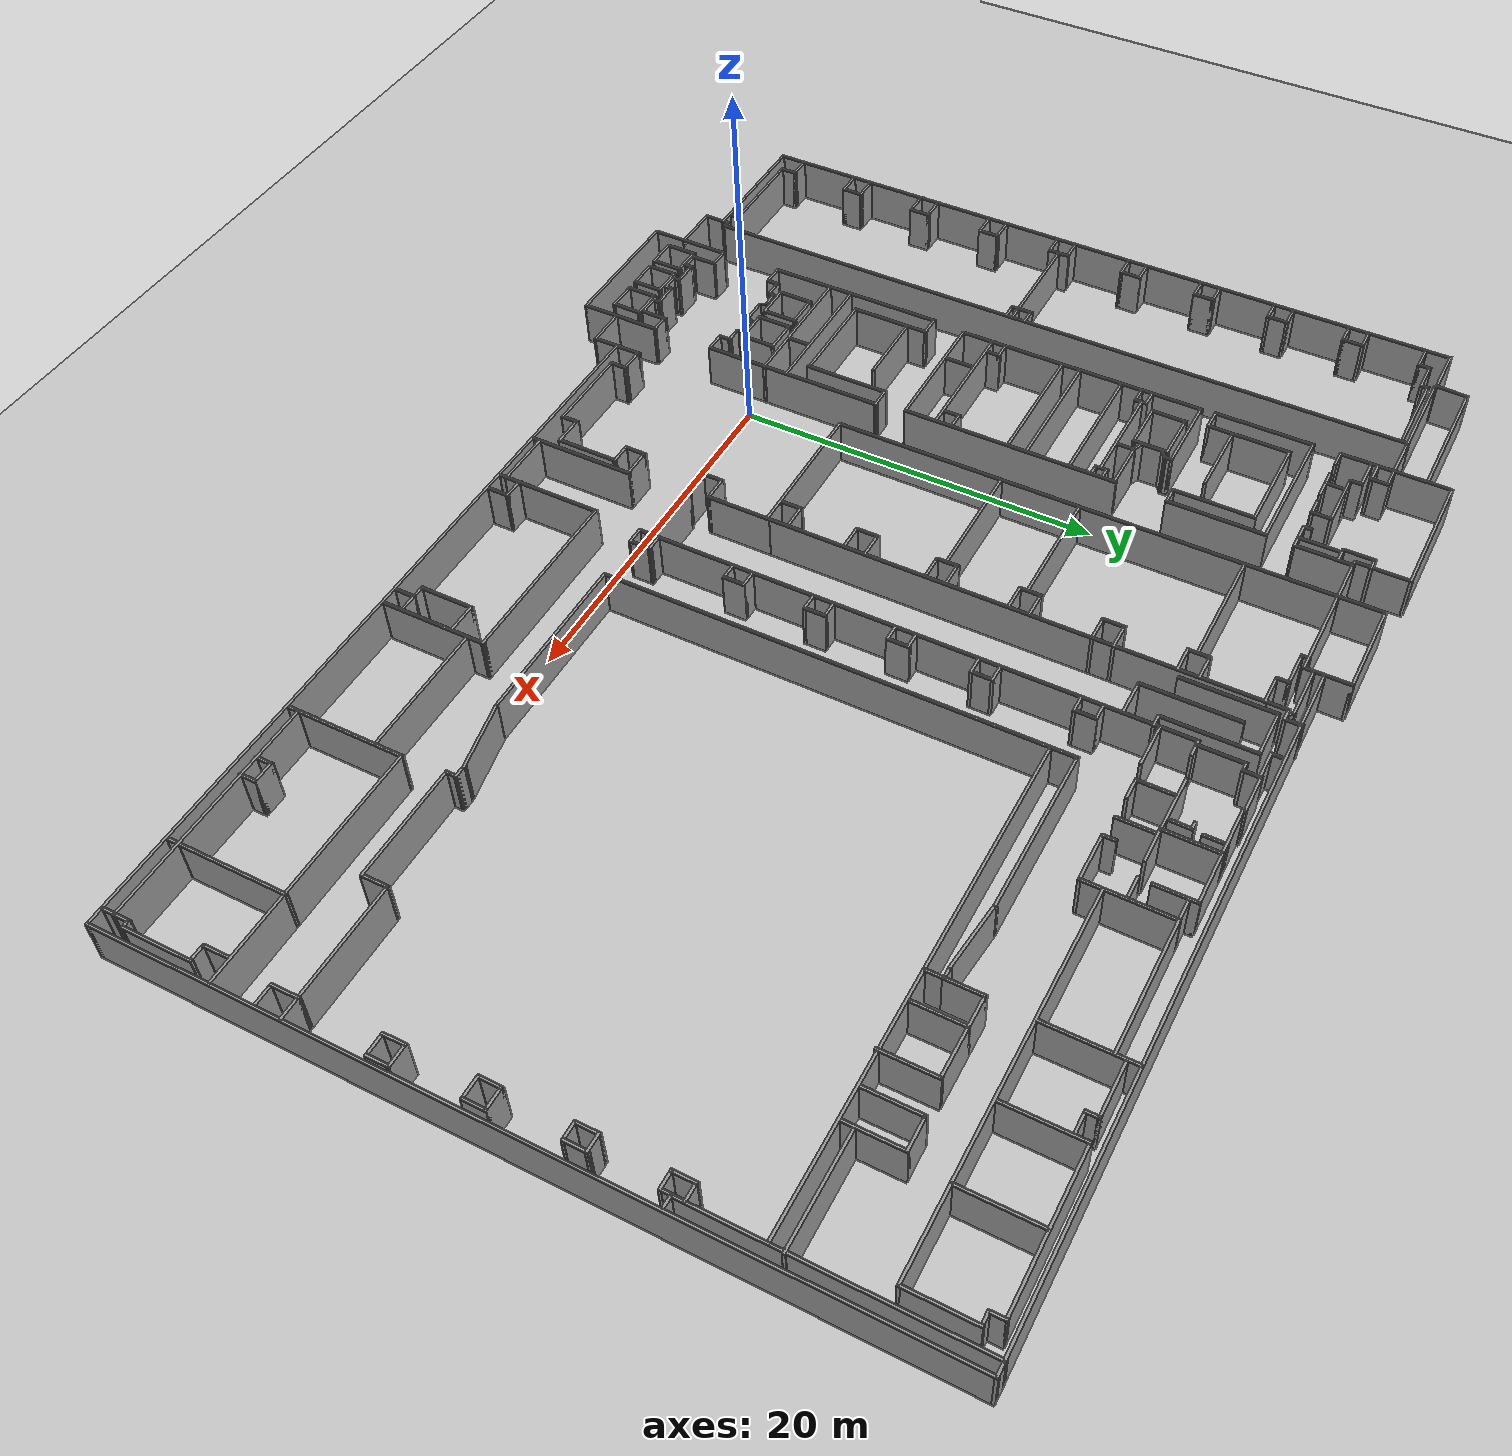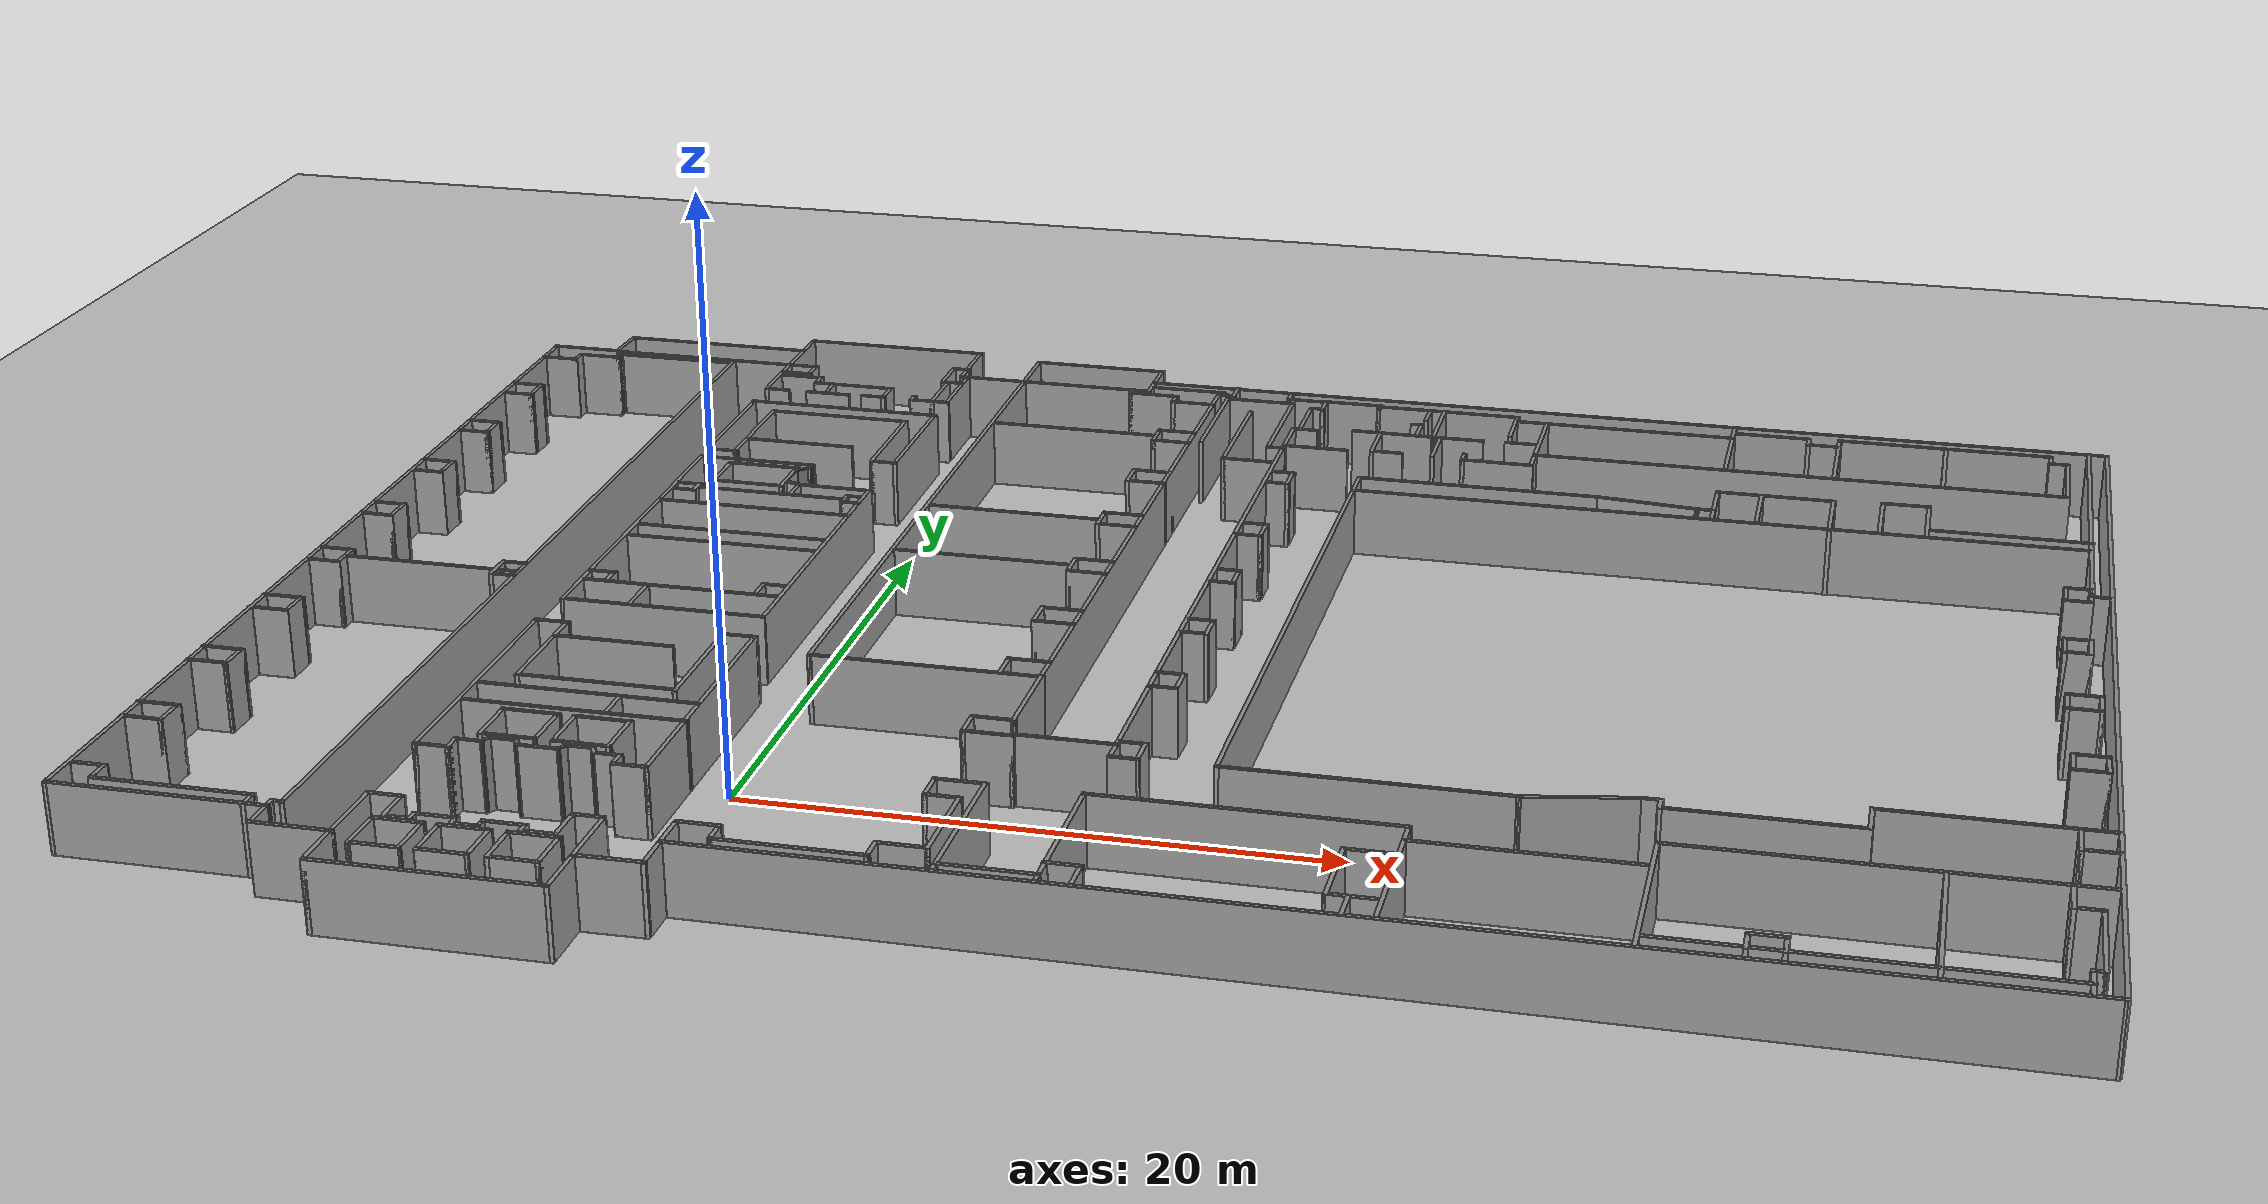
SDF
<sdf version="1.6">
 <world name="default">
  <light name="sun" type="directional">
   <pose>0 0 10 0 -0 0</pose>
   <diffuse>0.8 0.8 0.8 1</diffuse>
   <specular>0.2 0.2 0.2 1</specular>
   <attenuation>
    <range>1000</range>
    <constant>0.9</constant>
    <linear>0.01</linear>
    <quadratic>0.001</quadratic>
   </attenuation>
   <direction>-0.5 0.1 -0.9</direction>
  </light>
  <model name="ground_plane">
   <static>1</static>
   <link name="link">
    <collision name="collision">
     <geometry><plane><normal>0 0 1</normal><size>100 100</size></plane></geometry>
     <surface>
      <contact><collide_bitmask>65535</collide_bitmask></contact>
      <friction><ode><mu>100</mu><mu2>50</mu2></ode></friction>
     </surface>
    </collision>
    <visual name="visual">
     <cast_shadows>0</cast_shadows>
     <geometry><plane><normal>0 0 1</normal><size>100 100</size></plane></geometry>
     <material>
      <script><uri>file://media/materials/scripts/gazebo.material</uri><name>Gazebo/Grey</name></script>
     </material>
    </visual>
   </link>
  </model>
  <gravity>0 0 -9.8</gravity>
  <magnetic_field>6e-06 2.3e-05 -4.2e-05</magnetic_field>
  <atmosphere type="adiabatic"/>
  <physics name="default_physics" default="0" type="ode">
   <max_step_size>0.001</max_step_size>
   <real_time_factor>1</real_time_factor>
   <real_time_update_rate>1000</real_time_update_rate>
  </physics>
  <scene><ambient>0.4 0.4 0.4 1</ambient><background>0.7 0.7 0.7 1</background><shadows>1</shadows></scene>
  <spherical_coordinates>
   <surface_model>EARTH_WGS84</surface_model>
   <latitude_deg>0</latitude_deg>
   <longitude_deg>0</longitude_deg>
   <elevation>0</elevation>
   <heading_deg>0</heading_deg>
  </spherical_coordinates>
  <model name="Tsudanuma_2-3-without_door">
   <pose>11.8595 12.3796 0 0 -0 0</pose>
   <link name="Wall_0">
    <collision name="Wall_0_Collision">
     <geometry><box><size>41.115 0.15 2.5</size></box></geometry>
     <pose>0 0 1.25 0 -0 0</pose>
    </collision>
    <visual name="Wall_0_Visual">
     <pose>0 0 1.25 0 -0 0</pose>
     <geometry><box><size>41.115 0.15 2.5</size></box></geometry>
     <material>
      <script><uri>file://media/materials/scripts/gazebo.material</uri><name>Gazebo/Grey</name></script>
      <ambient>1 1 1 1</ambient>
     </material>
     <meta><layer>0</layer></meta>
    </visual>
    <pose>-30.8385 -0.07469 0 0 -0 -1.5708</pose>
   </link>
   <link name="Wall_1">
    <collision name="Wall_1_Collision">
     <geometry><box><size>7.45363 0.15 2.5</size></box></geometry>
     <pose>0 0 1.25 0 -0 0</pose>
    </collision>
    <visual name="Wall_1_Visual">
     <pose>0 0 1.25 0 -0 0</pose>
     <geometry><box><size>7.45363 0.15 2.5</size></box></geometry>
     <material>
      <script><uri>file://media/materials/scripts/gazebo.material</uri><name>Gazebo/Grey</name></script>
      <ambient>1 1 1 1</ambient>
     </material>
     <meta><layer>0</layer></meta>
    </visual>
    <pose>-27.1739 -20.5586 0 0 -0 -0.00039</pose>
   </link>
   <link name="Wall_10">
    <collision name="Wall_10_Collision">
     <geometry><box><size>42.1591 0.15 2.5</size></box></geometry>
     <pose>0 0 1.25 0 -0 0</pose>
    </collision>
    <visual name="Wall_10_Visual">
     <pose>0 0 1.25 0 -0 0</pose>
     <geometry><box><size>42.1591 0.15 2.5</size></box></geometry>
     <material>
      <script><uri>file://media/materials/scripts/gazebo.material</uri><name>Gazebo/Grey</name></script>
      <ambient>1 1 1 1</ambient>
     </material>
     <meta><layer>0</layer></meta>
    </visual>
    <pose>9.87341 -20.1767 0 0 -0 -0.000631</pose>
   </link>
   <link name="Wall_102">
    <collision name="Wall_102_Collision">
     <geometry><box><size>1.25 0.15 2.5</size></box></geometry>
     <pose>0 0 1.25 0 -0 0</pose>
    </collision>
    <visual name="Wall_102_Visual">
     <pose>0 0 1.25 0 -0 0</pose>
     <geometry><box><size>1.25 0.15 2.5</size></box></geometry>
     <material>
      <script><uri>file://media/materials/scripts/gazebo.material</uri><name>Gazebo/Grey</name></script>
      <ambient>1 1 1 1</ambient>
     </material>
     <meta><layer>0</layer></meta>
    </visual>
    <pose>-20.2708 10.8167 0 0 -0 0</pose>
   </link>
   <link name="Wall_103">
    <collision name="Wall_103_Collision">
     <geometry><box><size>1.5 0.15 2.5</size></box></geometry>
     <pose>0 0 1.25 0 -0 0</pose>
    </collision>
    <visual name="Wall_103_Visual">
     <pose>0 0 1.25 0 -0 0</pose>
     <geometry><box><size>1.5 0.15 2.5</size></box></geometry>
     <material>
      <script><uri>file://media/materials/scripts/gazebo.material</uri><name>Gazebo/Grey</name></script>
      <ambient>1 1 1 1</ambient>
     </material>
     <meta><layer>0</layer></meta>
    </visual>
    <pose>-19.7208 11.4917 0 0 -0 1.5708</pose>
   </link>
   <link name="Wall_104">
    <collision name="Wall_104_Collision">
     <geometry><box><size>4.25 0.15 2.5</size></box></geometry>
     <pose>0 0 1.25 0 -0 0</pose>
    </collision>
    <visual name="Wall_104_Visual">
     <pose>0 0 1.25 0 -0 0</pose>
     <geometry><box><size>4.25 0.15 2.5</size></box></geometry>
     <material>
      <script><uri>file://media/materials/scripts/gazebo.material</uri><name>Gazebo/Grey</name></script>
      <ambient>1 1 1 1</ambient>
     </material>
     <meta><layer>0</layer></meta>
    </visual>
    <pose>-17.6708 12.1667 0 0 -0 0</pose>
   </link>
   <link name="Wall_106">
    <collision name="Wall_106_Collision">
     <geometry><box><size>3.25 0.15 2.5</size></box></geometry>
     <pose>0 0 1.25 0 -0 0</pose>
    </collision>
    <visual name="Wall_106_Visual">
     <pose>0 0 1.25 0 -0 0</pose>
     <geometry><box><size>3.25 0.15 2.5</size></box></geometry>
     <material>
      <script><uri>file://media/materials/scripts/gazebo.material</uri><name>Gazebo/Grey</name></script>
      <ambient>1 1 1 1</ambient>
     </material>
     <meta><layer>0</layer></meta>
    </visual>
    <pose>-19.7208 13.7167 0 0 -0 1.5708</pose>
   </link>
   <link name="Wall_107">
    <collision name="Wall_107_Collision">
     <geometry><box><size>5.5 0.15 2.5</size></box></geometry>
     <pose>0 0 1.25 0 -0 0</pose>
    </collision>
    <visual name="Wall_107_Visual">
     <pose>0 0 1.25 0 -0 0</pose>
     <geometry><box><size>5.5 0.15 2.5</size></box></geometry>
     <material>
      <script><uri>file://media/materials/scripts/gazebo.material</uri><name>Gazebo/Grey</name></script>
      <ambient>1 1 1 1</ambient>
     </material>
     <meta><layer>0</layer></meta>
    </visual>
    <pose>-17.0458 15.2667 0 0 -0 0</pose>
   </link>
   <link name="Wall_108">
    <collision name="Wall_108_Collision">
     <geometry><box><size>4.5 0.15 2.5</size></box></geometry>
     <pose>0 0 1.25 0 -0 0</pose>
    </collision>
    <visual name="Wall_108_Visual">
     <pose>0 0 1.25 0 -0 0</pose>
     <geometry><box><size>4.5 0.15 2.5</size></box></geometry>
     <material>
      <script><uri>file://media/materials/scripts/gazebo.material</uri><name>Gazebo/Grey</name></script>
      <ambient>1 1 1 1</ambient>
     </material>
     <meta><layer>0</layer></meta>
    </visual>
    <pose>-14.3708 13.0917 0 0 -0 -1.5708</pose>
   </link>
   <link name="Wall_109">
    <collision name="Wall_109_Collision">
     <geometry><box><size>1 0.15 2.5</size></box></geometry>
     <pose>0 0 1.25 0 -0 0</pose>
    </collision>
    <visual name="Wall_109_Visual">
     <pose>0 0 1.25 0 -0 0</pose>
     <geometry><box><size>1 0.15 2.5</size></box></geometry>
     <material>
      <script><uri>file://media/materials/scripts/gazebo.material</uri><name>Gazebo/Grey</name></script>
      <ambient>1 1 1 1</ambient>
     </material>
     <meta><layer>0</layer></meta>
    </visual>
    <pose>-13.9458 10.9167 0 0 -0 0</pose>
   </link>
   <link name="Wall_11">
    <collision name="Wall_11_Collision">
     <geometry><box><size>42 0.15 2.5</size></box></geometry>
     <pose>0 0 1.25 0 -0 0</pose>
    </collision>
    <visual name="Wall_11_Visual">
     <pose>0 0 1.25 0 -0 0</pose>
     <geometry><box><size>42 0.15 2.5</size></box></geometry>
     <material>
      <script><uri>file://media/materials/scripts/gazebo.material</uri><name>Gazebo/Grey</name></script>
      <ambient>1 1 1 1</ambient>
     </material>
     <meta><layer>0</layer></meta>
    </visual>
    <pose>30.8779 0.735038 0 0 -0 1.5708</pose>
   </link>
   <link name="Wall_112">
    <collision name="Wall_112_Collision">
     <geometry><box><size>5.4 0.15 2.5</size></box></geometry>
     <pose>0 0 1.25 0 -0 0</pose>
    </collision>
    <visual name="Wall_112_Visual">
     <pose>0 0 1.25 0 -0 0</pose>
     <geometry><box><size>5.4 0.15 2.5</size></box></geometry>
     <material>
      <script><uri>file://media/materials/scripts/gazebo.material</uri><name>Gazebo/Grey</name></script>
      <ambient>1 1 1 1</ambient>
     </material>
     <meta><layer>0</layer></meta>
    </visual>
    <pose>-13.4614 13.5404 0 0 -0 -1.5708</pose>
   </link>
   <link name="Wall_114">
    <collision name="Wall_114_Collision">
     <geometry><box><size>7.5 0.15 2.5</size></box></geometry>
     <pose>0 0 1.25 0 -0 0</pose>
    </collision>
    <visual name="Wall_114_Visual">
     <pose>0 0 1.25 0 -0 0</pose>
     <geometry><box><size>7.5 0.15 2.5</size></box></geometry>
     <material>
      <script><uri>file://media/materials/scripts/gazebo.material</uri><name>Gazebo/Grey</name></script>
      <ambient>1 1 1 1</ambient>
     </material>
     <meta><layer>0</layer></meta>
    </visual>
    <pose>-17.1458 16.1667 0 0 -0 0</pose>
   </link>
   <link name="Wall_116">
    <collision name="Wall_116_Collision">
     <geometry><box><size>0.715508 0.15 2.5</size></box></geometry>
     <pose>0 0 1.25 0 -0 0</pose>
    </collision>
    <visual name="Wall_116_Visual">
     <pose>0 0 1.25 0 -0 0</pose>
     <geometry><box><size>0.715508 0.15 2.5</size></box></geometry>
     <material>
      <script><uri>file://media/materials/scripts/gazebo.material</uri><name>Gazebo/Grey</name></script>
      <ambient>1 1 1 1</ambient>
     </material>
     <meta><layer>0</layer></meta>
    </visual>
    <pose>-16.6297 9.54241 0 0 -0 0.731865</pose>
   </link>
   <link name="Wall_118">
    <collision name="Wall_118_Collision">
     <geometry><box><size>0.5 0.15 2.5</size></box></geometry>
     <pose>0 0 1.25 0 -0 0</pose>
    </collision>
    <visual name="Wall_118_Visual">
     <pose>0 0 1.25 0 -0 0</pose>
     <geometry><box><size>0.5 0.15 2.5</size></box></geometry>
     <material>
      <script><uri>file://media/materials/scripts/gazebo.material</uri><name>Gazebo/Grey</name></script>
      <ambient>1 1 1 1</ambient>
     </material>
     <meta><layer>0</layer></meta>
    </visual>
    <pose>-16.4194 9.84917 0 0 -0 1.5708</pose>
   </link>
   <link name="Wall_119">
    <collision name="Wall_119_Collision">
     <geometry><box><size>4.5 0.15 2.5</size></box></geometry>
     <pose>0 0 1.25 0 -0 0</pose>
    </collision>
    <visual name="Wall_119_Visual">
     <pose>0 0 1.25 0 -0 0</pose>
     <geometry><box><size>4.5 0.15 2.5</size></box></geometry>
     <material>
      <script><uri>file://media/materials/scripts/gazebo.material</uri><name>Gazebo/Grey</name></script>
      <ambient>1 1 1 1</ambient>
     </material>
     <meta><layer>0</layer></meta>
    </visual>
    <pose>-18.5944 10.0242 0 0 -0 3.14159</pose>
   </link>
   <link name="Wall_12">
    <collision name="Wall_12_Collision">
     <geometry><box><size>37 0.15 2.5</size></box></geometry>
     <pose>0 0 1.25 0 -0 0</pose>
    </collision>
    <visual name="Wall_12_Visual">
     <pose>0 0 1.25 0 -0 0</pose>
     <geometry><box><size>37 0.15 2.5</size></box></geometry>
     <material>
      <script><uri>file://media/materials/scripts/gazebo.material</uri><name>Gazebo/Grey</name></script>
      <ambient>1 1 1 1</ambient>
     </material>
     <meta><layer>0</layer></meta>
    </visual>
    <pose>12.4529 21.66 0 0 -0 3.14159</pose>
   </link>
   <link name="Wall_120">
    <collision name="Wall_120_Collision">
     <geometry><box><size>14 0.15 2.5</size></box></geometry>
     <pose>0 0 1.25 0 -0 0</pose>
    </collision>
    <visual name="Wall_120_Visual">
     <pose>0 0 1.25 0 -0 0</pose>
     <geometry><box><size>14 0.15 2.5</size></box></geometry>
     <material>
      <script><uri>file://media/materials/scripts/gazebo.material</uri><name>Gazebo/Grey</name></script>
      <ambient>1 1 1 1</ambient>
     </material>
     <meta><layer>0</layer></meta>
    </visual>
    <pose>-20.7694 3.09917 0 0 -0 -1.5708</pose>
   </link>
   <link name="Wall_121">
    <collision name="Wall_121_Collision">
     <geometry><box><size>7.32925 0.15 2.5</size></box></geometry>
     <pose>0 0 1.25 0 -0 0</pose>
    </collision>
    <visual name="Wall_121_Visual">
     <pose>0 0 1.25 0 -0 0</pose>
     <geometry><box><size>7.32925 0.15 2.5</size></box></geometry>
     <material>
      <script><uri>file://media/materials/scripts/gazebo.material</uri><name>Gazebo/Grey</name></script>
      <ambient>1 1 1 1</ambient>
     </material>
     <meta><layer>0</layer></meta>
    </visual>
    <pose>-17.1797 -3.82583 0 0 -0 0</pose>
   </link>
   <link name="Wall_122">
    <collision name="Wall_122_Collision">
     <geometry><box><size>12 0.15 2.5</size></box></geometry>
     <pose>0 0 1.25 0 -0 0</pose>
    </collision>
    <visual name="Wall_122_Visual">
     <pose>0 0 1.25 0 -0 0</pose>
     <geometry><box><size>12 0.15 2.5</size></box></geometry>
     <material>
      <script><uri>file://media/materials/scripts/gazebo.material</uri><name>Gazebo/Grey</name></script>
      <ambient>1 1 1 1</ambient>
     </material>
     <meta><layer>0</layer></meta>
    </visual>
    <pose>-13.5711 2.11814 0 0 -0 1.5708</pose>
   </link>
   <link name="Wall_123">
    <collision name="Wall_123_Collision">
     <geometry><box><size>2.82925 0.15 2.5</size></box></geometry>
     <pose>0 0 1.25 0 -0 0</pose>
    </collision>
    <visual name="Wall_123_Visual">
     <pose>0 0 1.25 0 -0 0</pose>
     <geometry><box><size>2.82925 0.15 2.5</size></box></geometry>
     <material>
      <script><uri>file://media/materials/scripts/gazebo.material</uri><name>Gazebo/Grey</name></script>
      <ambient>1 1 1 1</ambient>
     </material>
     <meta><layer>0</layer></meta>
    </visual>
    <pose>-14.9297 8.02417 0 0 -0 -3.14159</pose>
   </link>
   <link name="Wall_124">
    <collision name="Wall_124_Collision">
     <geometry><box><size>0.765048 0.15 2.5</size></box></geometry>
     <pose>0 0 1.25 0 -0 0</pose>
    </collision>
    <visual name="Wall_124_Visual">
     <pose>0 0 1.25 0 -0 0</pose>
     <geometry><box><size>0.765048 0.15 2.5</size></box></geometry>
     <material>
      <script><uri>file://media/materials/scripts/gazebo.material</uri><name>Gazebo/Grey</name></script>
      <ambient>1 1 1 1</ambient>
     </material>
     <meta><layer>0</layer></meta>
    </visual>
    <pose>-16.5547 8.13882 0 0 -0 2.75957</pose>
   </link>
   <link name="Wall_128">
    <collision name="Wall_128_Collision">
     <geometry><box><size>1.25 0.15 2.5</size></box></geometry>
     <pose>0 0 1.25 0 -0 0</pose>
    </collision>
    <visual name="Wall_128_Visual">
     <pose>0 0 1.25 0 -0 0</pose>
     <geometry><box><size>1.25 0.15 2.5</size></box></geometry>
     <material>
      <script><uri>file://media/materials/scripts/gazebo.material</uri><name>Gazebo/Grey</name></script>
      <ambient>1 1 1 1</ambient>
     </material>
     <meta><layer>0</layer></meta>
    </visual>
    <pose>-16.8401 8.80346 0 0 -0 1.5708</pose>
   </link>
   <link name="Wall_13">
    <collision name="Wall_13_Collision">
     <geometry><box><size>1.5 0.15 2.5</size></box></geometry>
     <pose>0 0 1.25 0 -0 0</pose>
    </collision>
    <visual name="Wall_13_Visual">
     <pose>0 0 1.25 0 -0 0</pose>
     <geometry><box><size>1.5 0.15 2.5</size></box></geometry>
     <material>
      <script><uri>file://media/materials/scripts/gazebo.material</uri><name>Gazebo/Grey</name></script>
      <ambient>1 1 1 1</ambient>
     </material>
     <meta><layer>0</layer></meta>
    </visual>
    <pose>-5.97206 22.335 0 0 -0 1.5708</pose>
   </link>
   <link name="Wall_130">
    <collision name="Wall_130_Collision">
     <geometry><box><size>7.25 0.15 2.5</size></box></geometry>
     <pose>0 0 1.25 0 -0 0</pose>
    </collision>
    <visual name="Wall_130_Visual">
     <pose>0 0 1.25 0 -0 0</pose>
     <geometry><box><size>7.25 0.15 2.5</size></box></geometry>
     <material>
      <script><uri>file://media/materials/scripts/gazebo.material</uri><name>Gazebo/Grey</name></script>
      <ambient>1 1 1 1</ambient>
     </material>
     <meta><layer>0</layer></meta>
    </visual>
    <pose>-17.2305 -2.06927 0 0 -0 0</pose>
   </link>
   <link name="Wall_132">
    <collision name="Wall_132_Collision">
     <geometry><box><size>1 0.15 2.5</size></box></geometry>
     <pose>0 0 1.25 0 -0 0</pose>
    </collision>
    <visual name="Wall_132_Visual">
     <pose>0 0 1.25 0 -0 0</pose>
     <geometry><box><size>1 0.15 2.5</size></box></geometry>
     <material>
      <script><uri>file://media/materials/scripts/gazebo.material</uri><name>Gazebo/Grey</name></script>
      <ambient>1 1 1 1</ambient>
     </material>
     <meta><layer>0</layer></meta>
    </visual>
    <pose>-20.3175 -1.29143 0 0 -0 0</pose>
   </link>
   <link name="Wall_133">
    <collision name="Wall_133_Collision">
     <geometry><box><size>0.75 0.15 2.5</size></box></geometry>
     <pose>0 0 1.25 0 -0 0</pose>
    </collision>
    <visual name="Wall_133_Visual">
     <pose>0 0 1.25 0 -0 0</pose>
     <geometry><box><size>0.75 0.15 2.5</size></box></geometry>
     <material>
      <script><uri>file://media/materials/scripts/gazebo.material</uri><name>Gazebo/Grey</name></script>
      <ambient>1 1 1 1</ambient>
     </material>
     <meta><layer>0</layer></meta>
    </visual>
    <pose>-19.8925 -1.59143 0 0 -0 -1.5708</pose>
   </link>
   <link name="Wall_135">
    <collision name="Wall_135_Collision">
     <geometry><box><size>1 0.15 2.5</size></box></geometry>
     <pose>0 0 1.25 0 -0 0</pose>
    </collision>
    <visual name="Wall_135_Visual">
     <pose>0 0 1.25 0 -0 0</pose>
     <geometry><box><size>1 0.15 2.5</size></box></geometry>
     <material>
      <script><uri>file://media/materials/scripts/gazebo.material</uri><name>Gazebo/Grey</name></script>
      <ambient>1 1 1 1</ambient>
     </material>
     <meta><layer>0</layer></meta>
    </visual>
    <pose>-14.4819 -1.56838 0 0 -0 1.5708</pose>
   </link>
   <link name="Wall_136">
    <collision name="Wall_136_Collision">
     <geometry><box><size>1 0.15 2.5</size></box></geometry>
     <pose>0 0 1.25 0 -0 0</pose>
    </collision>
    <visual name="Wall_136_Visual">
     <pose>0 0 1.25 0 -0 0</pose>
     <geometry><box><size>1 0.15 2.5</size></box></geometry>
     <material>
      <script><uri>file://media/materials/scripts/gazebo.material</uri><name>Gazebo/Grey</name></script>
      <ambient>1 1 1 1</ambient>
     </material>
     <meta><layer>0</layer></meta>
    </visual>
    <pose>-14.0569 -1.14338 0 0 -0 0</pose>
   </link>
   <link name="Wall_138">
    <collision name="Wall_138_Collision">
     <geometry><box><size>1.75 0.15 2.5</size></box></geometry>
     <pose>0 0 1.25 0 -0 0</pose>
    </collision>
    <visual name="Wall_138_Visual">
     <pose>0 0 1.25 0 -0 0</pose>
     <geometry><box><size>1.75 0.15 2.5</size></box></geometry>
     <material>
      <script><uri>file://media/materials/scripts/gazebo.material</uri><name>Gazebo/Grey</name></script>
      <ambient>1 1 1 1</ambient>
     </material>
     <meta><layer>0</layer></meta>
    </visual>
    <pose>-18.3711 -2.90721 0 0 -0 -1.5708</pose>
   </link>
   <link name="Wall_14">
    <collision name="Wall_14_Collision">
     <geometry><box><size>5.25 0.15 2.5</size></box></geometry>
     <pose>0 0 1.25 0 -0 0</pose>
    </collision>
    <visual name="Wall_14_Visual">
     <pose>0 0 1.25 0 -0 0</pose>
     <geometry><box><size>5.25 0.15 2.5</size></box></geometry>
     <material>
      <script><uri>file://media/materials/scripts/gazebo.material</uri><name>Gazebo/Grey</name></script>
      <ambient>1 1 1 1</ambient>
     </material>
     <meta><layer>0</layer></meta>
    </visual>
    <pose>-8.52206 23.01 0 0 -0 3.14159</pose>
   </link>
   <link name="Wall_140">
    <collision name="Wall_140_Collision">
     <geometry><box><size>4.25 0.15 2.5</size></box></geometry>
     <pose>0 0 1.25 0 -0 0</pose>
    </collision>
    <visual name="Wall_140_Visual">
     <pose>0 0 1.25 0 -0 0</pose>
     <geometry><box><size>4.25 0.15 2.5</size></box></geometry>
     <material>
      <script><uri>file://media/materials/scripts/gazebo.material</uri><name>Gazebo/Grey</name></script>
      <ambient>1 1 1 1</ambient>
     </material>
     <meta><layer>0</layer></meta>
    </visual>
    <pose>-17.8074 -6.80767 0 0 -0 3.14159</pose>
   </link>
   <link name="Wall_141">
    <collision name="Wall_141_Collision">
     <geometry><box><size>1.25 0.15 2.5</size></box></geometry>
     <pose>0 0 1.25 0 -0 0</pose>
    </collision>
    <visual name="Wall_141_Visual">
     <pose>0 0 1.25 0 -0 0</pose>
     <geometry><box><size>1.25 0.15 2.5</size></box></geometry>
     <material>
      <script><uri>file://media/materials/scripts/gazebo.material</uri><name>Gazebo/Grey</name></script>
      <ambient>1 1 1 1</ambient>
     </material>
     <meta><layer>0</layer></meta>
    </visual>
    <pose>-19.8574 -6.25767 0 0 -0 1.5708</pose>
   </link>
   <link name="Wall_142">
    <collision name="Wall_142_Collision">
     <geometry><box><size>1.25 0.15 2.5</size></box></geometry>
     <pose>0 0 1.25 0 -0 0</pose>
    </collision>
    <visual name="Wall_142_Visual">
     <pose>0 0 1.25 0 -0 0</pose>
     <geometry><box><size>1.25 0.15 2.5</size></box></geometry>
     <material>
      <script><uri>file://media/materials/scripts/gazebo.material</uri><name>Gazebo/Grey</name></script>
      <ambient>1 1 1 1</ambient>
     </material>
     <meta><layer>0</layer></meta>
    </visual>
    <pose>-20.4074 -5.70767 0 0 -0 3.14159</pose>
   </link>
   <link name="Wall_143">
    <collision name="Wall_143_Collision">
     <geometry><box><size>10 0.15 2.5</size></box></geometry>
     <pose>0 0 1.25 0 -0 0</pose>
    </collision>
    <visual name="Wall_143_Visual">
     <pose>0 0 1.25 0 -0 0</pose>
     <geometry><box><size>10 0.15 2.5</size></box></geometry>
     <material>
      <script><uri>file://media/materials/scripts/gazebo.material</uri><name>Gazebo/Grey</name></script>
      <ambient>1 1 1 1</ambient>
     </material>
     <meta><layer>0</layer></meta>
    </visual>
    <pose>-20.9574 -10.6327 0 0 -0 -1.5708</pose>
   </link>
   <link name="Wall_144">
    <collision name="Wall_144_Collision">
     <geometry><box><size>1.25 0.15 2.5</size></box></geometry>
     <pose>0 0 1.25 0 -0 0</pose>
    </collision>
    <visual name="Wall_144_Visual">
     <pose>0 0 1.25 0 -0 0</pose>
     <geometry><box><size>1.25 0.15 2.5</size></box></geometry>
     <material>
      <script><uri>file://media/materials/scripts/gazebo.material</uri><name>Gazebo/Grey</name></script>
      <ambient>1 1 1 1</ambient>
     </material>
     <meta><layer>0</layer></meta>
    </visual>
    <pose>-20.4074 -15.5577 0 0 -0 0</pose>
   </link>
   <link name="Wall_145">
    <collision name="Wall_145_Collision">
     <geometry><box><size>0.75 0.15 2.5</size></box></geometry>
     <pose>0 0 1.25 0 -0 0</pose>
    </collision>
    <visual name="Wall_145_Visual">
     <pose>0 0 1.25 0 -0 0</pose>
     <geometry><box><size>0.75 0.15 2.5</size></box></geometry>
     <material>
      <script><uri>file://media/materials/scripts/gazebo.material</uri><name>Gazebo/Grey</name></script>
      <ambient>1 1 1 1</ambient>
     </material>
     <meta><layer>0</layer></meta>
    </visual>
    <pose>-19.8574 -15.2577 0 0 -0 1.5708</pose>
   </link>
   <link name="Wall_146">
    <collision name="Wall_146_Collision">
     <geometry><box><size>1 0.15 2.5</size></box></geometry>
     <pose>0 0 1.25 0 -0 0</pose>
    </collision>
    <visual name="Wall_146_Visual">
     <pose>0 0 1.25 0 -0 0</pose>
     <geometry><box><size>1 0.15 2.5</size></box></geometry>
     <material>
      <script><uri>file://media/materials/scripts/gazebo.material</uri><name>Gazebo/Grey</name></script>
      <ambient>1 1 1 1</ambient>
     </material>
     <meta><layer>0</layer></meta>
    </visual>
    <pose>-19.4324 -14.9577 0 0 -0 0</pose>
   </link>
   <link name="Wall_147">
    <collision name="Wall_147_Collision">
     <geometry><box><size>0.5 0.15 2.5</size></box></geometry>
     <pose>0 0 1.25 0 -0 0</pose>
    </collision>
    <visual name="Wall_147_Visual">
     <pose>0 0 1.25 0 -0 0</pose>
     <geometry><box><size>0.5 0.15 2.5</size></box></geometry>
     <material>
      <script><uri>file://media/materials/scripts/gazebo.material</uri><name>Gazebo/Grey</name></script>
      <ambient>1 1 1 1</ambient>
     </material>
     <meta><layer>0</layer></meta>
    </visual>
    <pose>-18.9199 -14.8061 0 0 -0 1.0472</pose>
   </link>
   <link name="Wall_148">
    <collision name="Wall_148_Collision">
     <geometry><box><size>1 0.15 2.5</size></box></geometry>
     <pose>0 0 1.25 0 -0 0</pose>
    </collision>
    <visual name="Wall_148_Visual">
     <pose>0 0 1.25 0 -0 0</pose>
     <geometry><box><size>1 0.15 2.5</size></box></geometry>
     <material>
      <script><uri>file://media/materials/scripts/gazebo.material</uri><name>Gazebo/Grey</name></script>
      <ambient>1 1 1 1</ambient>
     </material>
     <meta><layer>0</layer></meta>
    </visual>
    <pose>-18.4074 -14.6546 0 0 -0 0</pose>
   </link>
   <link name="Wall_149">
    <collision name="Wall_149_Collision">
     <geometry><box><size>0.5 0.15 2.5</size></box></geometry>
     <pose>0 0 1.25 0 -0 0</pose>
    </collision>
    <visual name="Wall_149_Visual">
     <pose>0 0 1.25 0 -0 0</pose>
     <geometry><box><size>0.5 0.15 2.5</size></box></geometry>
     <material>
      <script><uri>file://media/materials/scripts/gazebo.material</uri><name>Gazebo/Grey</name></script>
      <ambient>1 1 1 1</ambient>
     </material>
     <meta><layer>0</layer></meta>
    </visual>
    <pose>-17.8949 -14.8061 0 0 -0 -1.0472</pose>
   </link>
   <link name="Wall_15">
    <collision name="Wall_15_Collision">
     <geometry><box><size>2.5 0.15 2.5</size></box></geometry>
     <pose>0 0 1.25 0 -0 0</pose>
    </collision>
    <visual name="Wall_15_Visual">
     <pose>0 0 1.25 0 -0 0</pose>
     <geometry><box><size>2.5 0.15 2.5</size></box></geometry>
     <material>
      <script><uri>file://media/materials/scripts/gazebo.material</uri><name>Gazebo/Grey</name></script>
      <ambient>1 1 1 1</ambient>
     </material>
     <meta><layer>0</layer></meta>
    </visual>
    <pose>-11.0721 21.835 0 0 -0 -1.5708</pose>
   </link>
   <link name="Wall_150">
    <collision name="Wall_150_Collision">
     <geometry><box><size>1.5 0.15 2.5</size></box></geometry>
     <pose>0 0 1.25 0 -0 0</pose>
    </collision>
    <visual name="Wall_150_Visual">
     <pose>0 0 1.25 0 -0 0</pose>
     <geometry><box><size>1.5 0.15 2.5</size></box></geometry>
     <material>
      <script><uri>file://media/materials/scripts/gazebo.material</uri><name>Gazebo/Grey</name></script>
      <ambient>1 1 1 1</ambient>
     </material>
     <meta><layer>0</layer></meta>
    </visual>
    <pose>-17.1324 -14.9577 0 0 -0 0</pose>
   </link>
   <link name="Wall_151">
    <collision name="Wall_151_Collision">
     <geometry><box><size>0.5 0.15 2.5</size></box></geometry>
     <pose>0 0 1.25 0 -0 0</pose>
    </collision>
    <visual name="Wall_151_Visual">
     <pose>0 0 1.25 0 -0 0</pose>
     <geometry><box><size>0.5 0.15 2.5</size></box></geometry>
     <material>
      <script><uri>file://media/materials/scripts/gazebo.material</uri><name>Gazebo/Grey</name></script>
      <ambient>1 1 1 1</ambient>
     </material>
     <meta><layer>0</layer></meta>
    </visual>
    <pose>-16.3699 -14.8061 0 0 -0 1.0472</pose>
   </link>
   <link name="Wall_152">
    <collision name="Wall_152_Collision">
     <geometry><box><size>1 0.15 2.5</size></box></geometry>
     <pose>0 0 1.25 0 -0 0</pose>
    </collision>
    <visual name="Wall_152_Visual">
     <pose>0 0 1.25 0 -0 0</pose>
     <geometry><box><size>1 0.15 2.5</size></box></geometry>
     <material>
      <script><uri>file://media/materials/scripts/gazebo.material</uri><name>Gazebo/Grey</name></script>
      <ambient>1 1 1 1</ambient>
     </material>
     <meta><layer>0</layer></meta>
    </visual>
    <pose>-15.8574 -14.6546 0 0 -0 0</pose>
   </link>
   <link name="Wall_153">
    <collision name="Wall_153_Collision">
     <geometry><box><size>0.5 0.15 2.5</size></box></geometry>
     <pose>0 0 1.25 0 -0 0</pose>
    </collision>
    <visual name="Wall_153_Visual">
     <pose>0 0 1.25 0 -0 0</pose>
     <geometry><box><size>0.5 0.15 2.5</size></box></geometry>
     <material>
      <script><uri>file://media/materials/scripts/gazebo.material</uri><name>Gazebo/Grey</name></script>
      <ambient>1 1 1 1</ambient>
     </material>
     <meta><layer>0</layer></meta>
    </visual>
    <pose>-15.3449 -14.8061 0 0 -0 -1.0472</pose>
   </link>
   <link name="Wall_154">
    <collision name="Wall_154_Collision">
     <geometry><box><size>1 0.15 2.5</size></box></geometry>
     <pose>0 0 1.25 0 -0 0</pose>
    </collision>
    <visual name="Wall_154_Visual">
     <pose>0 0 1.25 0 -0 0</pose>
     <geometry><box><size>1 0.15 2.5</size></box></geometry>
     <material>
      <script><uri>file://media/materials/scripts/gazebo.material</uri><name>Gazebo/Grey</name></script>
      <ambient>1 1 1 1</ambient>
     </material>
     <meta><layer>0</layer></meta>
    </visual>
    <pose>-14.8324 -14.9577 0 0 -0 0</pose>
   </link>
   <link name="Wall_155">
    <collision name="Wall_155_Collision">
     <geometry><box><size>0.75 0.15 2.5</size></box></geometry>
     <pose>0 0 1.25 0 -0 0</pose>
    </collision>
    <visual name="Wall_155_Visual">
     <pose>0 0 1.25 0 -0 0</pose>
     <geometry><box><size>0.75 0.15 2.5</size></box></geometry>
     <material>
      <script><uri>file://media/materials/scripts/gazebo.material</uri><name>Gazebo/Grey</name></script>
      <ambient>1 1 1 1</ambient>
     </material>
     <meta><layer>0</layer></meta>
    </visual>
    <pose>-14.4074 -15.2577 0 0 -0 -1.5708</pose>
   </link>
   <link name="Wall_156">
    <collision name="Wall_156_Collision">
     <geometry><box><size>1.25 0.15 2.5</size></box></geometry>
     <pose>0 0 1.25 0 -0 0</pose>
    </collision>
    <visual name="Wall_156_Visual">
     <pose>0 0 1.25 0 -0 0</pose>
     <geometry><box><size>1.25 0.15 2.5</size></box></geometry>
     <material>
      <script><uri>file://media/materials/scripts/gazebo.material</uri><name>Gazebo/Grey</name></script>
      <ambient>1 1 1 1</ambient>
     </material>
     <meta><layer>0</layer></meta>
    </visual>
    <pose>-13.8574 -15.5577 0 0 -0 0</pose>
   </link>
   <link name="Wall_157">
    <collision name="Wall_157_Collision">
     <geometry><box><size>10.25 0.15 2.5</size></box></geometry>
     <pose>0 0 1.25 0 -0 0</pose>
    </collision>
    <visual name="Wall_157_Visual">
     <pose>0 0 1.25 0 -0 0</pose>
     <geometry><box><size>10.25 0.15 2.5</size></box></geometry>
     <material>
      <script><uri>file://media/materials/scripts/gazebo.material</uri><name>Gazebo/Grey</name></script>
      <ambient>1 1 1 1</ambient>
     </material>
     <meta><layer>0</layer></meta>
    </visual>
    <pose>-13.3074 -10.5077 0 0 -0 1.5708</pose>
   </link>
   <link name="Wall_158">
    <collision name="Wall_158_Collision">
     <geometry><box><size>1.25 0.15 2.5</size></box></geometry>
     <pose>0 0 1.25 0 -0 0</pose>
    </collision>
    <visual name="Wall_158_Visual">
     <pose>0 0 1.25 0 -0 0</pose>
     <geometry><box><size>1.25 0.15 2.5</size></box></geometry>
     <material>
      <script><uri>file://media/materials/scripts/gazebo.material</uri><name>Gazebo/Grey</name></script>
      <ambient>1 1 1 1</ambient>
     </material>
     <meta><layer>0</layer></meta>
    </visual>
    <pose>-13.8574 -5.4671 0 0 -0 -3.12445</pose>
   </link>
   <link name="Wall_16">
    <collision name="Wall_16_Collision">
     <geometry><box><size>2.75 0.15 2.5</size></box></geometry>
     <pose>0 0 1.25 0 -0 0</pose>
    </collision>
    <visual name="Wall_16_Visual">
     <pose>0 0 1.25 0 -0 0</pose>
     <geometry><box><size>2.75 0.15 2.5</size></box></geometry>
     <material>
      <script><uri>file://media/materials/scripts/gazebo.material</uri><name>Gazebo/Grey</name></script>
      <ambient>1 1 1 1</ambient>
     </material>
     <meta><layer>0</layer></meta>
    </visual>
    <pose>-12.3721 20.66 0 0 -0 3.14159</pose>
   </link>
   <link name="Wall_160">
    <collision name="Wall_160_Collision">
     <geometry><box><size>5.5 0.15 2.5</size></box></geometry>
     <pose>0 0 1.25 0 -0 0</pose>
    </collision>
    <visual name="Wall_160_Visual">
     <pose>0 0 1.25 0 -0 0</pose>
     <geometry><box><size>5.5 0.15 2.5</size></box></geometry>
     <material>
      <script><uri>file://media/materials/scripts/gazebo.material</uri><name>Gazebo/Grey</name></script>
      <ambient>1 1 1 1</ambient>
     </material>
     <meta><layer>0</layer></meta>
    </visual>
    <pose>-17.1919 -10.0068 0 0 -0 3.14159</pose>
   </link>
   <link name="Wall_161">
    <collision name="Wall_161_Collision">
     <geometry><box><size>3.34921 0.15 2.5</size></box></geometry>
     <pose>0 0 1.25 0 -0 0</pose>
    </collision>
    <visual name="Wall_161_Visual">
     <pose>0 0 1.25 0 -0 0</pose>
     <geometry><box><size>3.34921 0.15 2.5</size></box></geometry>
     <material>
      <script><uri>file://media/materials/scripts/gazebo.material</uri><name>Gazebo/Grey</name></script>
      <ambient>1 1 1 1</ambient>
     </material>
     <meta><layer>0</layer></meta>
    </visual>
    <pose>-19.8574 -8.40721 0 0 -0 1.5708</pose>
   </link>
   <link name="Wall_163">
    <collision name="Wall_163_Collision">
     <geometry><box><size>4.75 0.15 2.5</size></box></geometry>
     <pose>0 0 1.25 0 -0 0</pose>
    </collision>
    <visual name="Wall_163_Visual">
     <pose>0 0 1.25 0 -0 0</pose>
     <geometry><box><size>4.75 0.15 2.5</size></box></geometry>
     <material>
      <script><uri>file://media/materials/scripts/gazebo.material</uri><name>Gazebo/Grey</name></script>
      <ambient>1 1 1 1</ambient>
     </material>
     <meta><layer>0</layer></meta>
    </visual>
    <pose>-14.4074 -7.77654 0 0 -0 -1.5708</pose>
   </link>
   <link name="Wall_165">
    <collision name="Wall_165_Collision">
     <geometry><box><size>7.7 0.15 2.5</size></box></geometry>
     <pose>0 0 1.25 0 -0 0</pose>
    </collision>
    <visual name="Wall_165_Visual">
     <pose>0 0 1.25 0 -0 0</pose>
     <geometry><box><size>7.7 0.15 2.5</size></box></geometry>
     <material>
      <script><uri>file://media/materials/scripts/gazebo.material</uri><name>Gazebo/Grey</name></script>
      <ambient>1 1 1 1</ambient>
     </material>
     <meta><layer>0</layer></meta>
    </visual>
    <pose>-17.1019 -10.8525 0 0 -0 0</pose>
   </link>
   <link name="Wall_167">
    <collision name="Wall_167_Collision">
     <geometry><box><size>7.75 0.15 2.5</size></box></geometry>
     <pose>0 0 1.25 0 -0 0</pose>
    </collision>
    <visual name="Wall_167_Visual">
     <pose>0 0 1.25 0 -0 0</pose>
     <geometry><box><size>7.75 0.15 2.5</size></box></geometry>
     <material>
      <script><uri>file://media/materials/scripts/gazebo.material</uri><name>Gazebo/Grey</name></script>
      <ambient>1 1 1 1</ambient>
     </material>
     <meta><layer>0</layer></meta>
    </visual>
    <pose>-17.0935 -12.1708 0 0 -0 0</pose>
   </link>
   <link name="Wall_169">
    <collision name="Wall_169_Collision">
     <geometry><box><size>1.25 0.15 2.5</size></box></geometry>
     <pose>0 0 1.25 0 -0 0</pose>
    </collision>
    <visual name="Wall_169_Visual">
     <pose>0 0 1.25 0 -0 0</pose>
     <geometry><box><size>1.25 0.15 2.5</size></box></geometry>
     <material>
      <script><uri>file://media/materials/scripts/gazebo.material</uri><name>Gazebo/Grey</name></script>
      <ambient>1 1 1 1</ambient>
     </material>
     <meta><layer>0</layer></meta>
    </visual>
    <pose>-15.9785 -11.4951 0 0 -0 -1.5708</pose>
   </link>
   <link name="Wall_17">
    <collision name="Wall_17_Collision">
     <geometry><box><size>3 0.15 2.5</size></box></geometry>
     <pose>0 0 1.25 0 -0 0</pose>
    </collision>
    <visual name="Wall_17_Visual">
     <pose>0 0 1.25 0 -0 0</pose>
     <geometry><box><size>3 0.15 2.5</size></box></geometry>
     <material>
      <script><uri>file://media/materials/scripts/gazebo.material</uri><name>Gazebo/Grey</name></script>
      <ambient>1 1 1 1</ambient>
     </material>
     <meta><layer>0</layer></meta>
    </visual>
    <pose>-13.6721 22.085 0 0 -0 1.5708</pose>
   </link>
   <link name="Wall_171">
    <collision name="Wall_171_Collision">
     <geometry><box><size>6.5 0.15 2.5</size></box></geometry>
     <pose>0 0 1.25 0 -0 0</pose>
    </collision>
    <visual name="Wall_171_Visual">
     <pose>0 0 1.25 0 -0 0</pose>
     <geometry><box><size>6.5 0.15 2.5</size></box></geometry>
     <material>
      <script><uri>file://media/materials/scripts/gazebo.material</uri><name>Gazebo/Grey</name></script>
      <ambient>1 1 1 1</ambient>
     </material>
     <meta><layer>0</layer></meta>
    </visual>
    <pose>-7.84492 7.16554 0 0 -0 0</pose>
   </link>
   <link name="Wall_173">
    <collision name="Wall_173_Collision">
     <geometry><box><size>6.5 0.15 2.5</size></box></geometry>
     <pose>0 0 1.25 0 -0 0</pose>
    </collision>
    <visual name="Wall_173_Visual">
     <pose>0 0 1.25 0 -0 0</pose>
     <geometry><box><size>6.5 0.15 2.5</size></box></geometry>
     <material>
      <script><uri>file://media/materials/scripts/gazebo.material</uri><name>Gazebo/Grey</name></script>
      <ambient>1 1 1 1</ambient>
     </material>
     <meta><layer>0</layer></meta>
    </visual>
    <pose>-7.81856 2.84875 0 0 -0 0</pose>
   </link>
   <link name="Wall_176">
    <collision name="Wall_176_Collision">
     <geometry><box><size>2.75 0.15 2.5</size></box></geometry>
     <pose>0 0 1.25 0 -0 0</pose>
    </collision>
    <visual name="Wall_176_Visual">
     <pose>0 0 1.25 0 -0 0</pose>
     <geometry><box><size>2.75 0.15 2.5</size></box></geometry>
     <material>
      <script><uri>file://media/materials/scripts/gazebo.material</uri><name>Gazebo/Grey</name></script>
      <ambient>1 1 1 1</ambient>
     </material>
     <meta><layer>0</layer></meta>
    </visual>
    <pose>-20.9221 -20.36 0 0 -0 1.5708</pose>
   </link>
   <link name="Wall_177">
    <collision name="Wall_177_Collision">
     <geometry><box><size>1.25 0.15 2.5</size></box></geometry>
     <pose>0 0 1.25 0 -0 0</pose>
    </collision>
    <visual name="Wall_177_Visual">
     <pose>0 0 1.25 0 -0 0</pose>
     <geometry><box><size>1.25 0.15 2.5</size></box></geometry>
     <material>
      <script><uri>file://media/materials/scripts/gazebo.material</uri><name>Gazebo/Grey</name></script>
      <ambient>1 1 1 1</ambient>
     </material>
     <meta><layer>0</layer></meta>
    </visual>
    <pose>-20.3721 -19.06 0 0 -0 0</pose>
   </link>
   <link name="Wall_178">
    <collision name="Wall_178_Collision">
     <geometry><box><size>1.49235 0.15 2.5</size></box></geometry>
     <pose>0 0 1.25 0 -0 0</pose>
    </collision>
    <visual name="Wall_178_Visual">
     <pose>0 0 1.25 0 -0 0</pose>
     <geometry><box><size>1.49235 0.15 2.5</size></box></geometry>
     <material>
      <script><uri>file://media/materials/scripts/gazebo.material</uri><name>Gazebo/Grey</name></script>
      <ambient>1 1 1 1</ambient>
     </material>
     <meta><layer>0</layer></meta>
    </visual>
    <pose>-19.8214 -19.7312 0 0 -0 -1.56976</pose>
   </link>
   <link name="Wall_179">
    <collision name="Wall_179_Collision">
     <geometry><box><size>1 0.15 2.5</size></box></geometry>
     <pose>0 0 1.25 0 -0 0</pose>
    </collision>
    <visual name="Wall_179_Visual">
     <pose>0 0 1.25 0 -0 0</pose>
     <geometry><box><size>1 0.15 2.5</size></box></geometry>
     <material>
      <script><uri>file://media/materials/scripts/gazebo.material</uri><name>Gazebo/Grey</name></script>
      <ambient>1 1 1 1</ambient>
     </material>
     <meta><layer>0</layer></meta>
    </visual>
    <pose>-19.3957 -20.4038 0 0 -0 0</pose>
   </link>
   <link name="Wall_18">
    <collision name="Wall_18_Collision">
     <geometry><box><size>7.25 0.15 2.5</size></box></geometry>
     <pose>0 0 1.25 0 -0 0</pose>
    </collision>
    <visual name="Wall_18_Visual">
     <pose>0 0 1.25 0 -0 0</pose>
     <geometry><box><size>7.25 0.15 2.5</size></box></geometry>
     <material>
      <script><uri>file://media/materials/scripts/gazebo.material</uri><name>Gazebo/Grey</name></script>
      <ambient>1 1 1 1</ambient>
     </material>
     <meta><layer>0</layer></meta>
    </visual>
    <pose>-17.2221 23.51 0 0 -0 3.14159</pose>
   </link>
   <link name="Wall_180">
    <collision name="Wall_180_Collision">
     <geometry><box><size>0.492355 0.15 2.5</size></box></geometry>
     <pose>0 0 1.25 0 -0 0</pose>
    </collision>
    <visual name="Wall_180_Visual">
     <pose>0 0 1.25 0 -0 0</pose>
     <geometry><box><size>0.492355 0.15 2.5</size></box></geometry>
     <material>
      <script><uri>file://media/materials/scripts/gazebo.material</uri><name>Gazebo/Grey</name></script>
      <ambient>1 1 1 1</ambient>
     </material>
     <meta><layer>0</layer></meta>
    </visual>
    <pose>-18.9714 -20.2312 0 0 -0 1.57485</pose>
   </link>
   <link name="Wall_181">
    <collision name="Wall_181_Collision">
     <geometry><box><size>1.5 0.15 2.5</size></box></geometry>
     <pose>0 0 1.25 0 -0 0</pose>
    </collision>
    <visual name="Wall_181_Visual">
     <pose>0 0 1.25 0 -0 0</pose>
     <geometry><box><size>1.5 0.15 2.5</size></box></geometry>
     <material>
      <script><uri>file://media/materials/scripts/gazebo.material</uri><name>Gazebo/Grey</name></script>
      <ambient>1 1 1 1</ambient>
     </material>
     <meta><layer>0</layer></meta>
    </visual>
    <pose>-18.2971 -20.06 0 0 -0 0</pose>
   </link>
   <link name="Wall_182">
    <collision name="Wall_182_Collision">
     <geometry><box><size>0.502135 0.15 2.5</size></box></geometry>
     <pose>0 0 1.25 0 -0 0</pose>
    </collision>
    <visual name="Wall_182_Visual">
     <pose>0 0 1.25 0 -0 0</pose>
     <geometry><box><size>0.502135 0.15 2.5</size></box></geometry>
     <material>
      <script><uri>file://media/materials/scripts/gazebo.material</uri><name>Gazebo/Grey</name></script>
      <ambient>1 1 1 1</ambient>
     </material>
     <meta><layer>0</layer></meta>
    </visual>
    <pose>-17.6221 -20.2361 0 0 -0 -1.5708</pose>
   </link>
   <link name="Wall_183">
    <collision name="Wall_183_Collision">
     <geometry><box><size>1 0.15 2.5</size></box></geometry>
     <pose>0 0 1.25 0 -0 0</pose>
    </collision>
    <visual name="Wall_183_Visual">
     <pose>0 0 1.25 0 -0 0</pose>
     <geometry><box><size>1 0.15 2.5</size></box></geometry>
     <material>
      <script><uri>file://media/materials/scripts/gazebo.material</uri><name>Gazebo/Grey</name></script>
      <ambient>1 1 1 1</ambient>
     </material>
     <meta><layer>0</layer></meta>
    </visual>
    <pose>-17.1985 -20.4122 0 0 -0 0</pose>
   </link>
   <link name="Wall_184">
    <collision name="Wall_184_Collision">
     <geometry><box><size>0.502135 0.15 2.5</size></box></geometry>
     <pose>0 0 1.25 0 -0 0</pose>
    </collision>
    <visual name="Wall_184_Visual">
     <pose>0 0 1.25 0 -0 0</pose>
     <geometry><box><size>0.502135 0.15 2.5</size></box></geometry>
     <material>
      <script><uri>file://media/materials/scripts/gazebo.material</uri><name>Gazebo/Grey</name></script>
      <ambient>1 1 1 1</ambient>
     </material>
     <meta><layer>0</layer></meta>
    </visual>
    <pose>-16.7721 -20.2361 0 0 -0 1.5708</pose>
   </link>
   <link name="Wall_185">
    <collision name="Wall_185_Collision">
     <geometry><box><size>1.5 0.15 2.5</size></box></geometry>
     <pose>0 0 1.25 0 -0 0</pose>
    </collision>
    <visual name="Wall_185_Visual">
     <pose>0 0 1.25 0 -0 0</pose>
     <geometry><box><size>1.5 0.15 2.5</size></box></geometry>
     <material>
      <script><uri>file://media/materials/scripts/gazebo.material</uri><name>Gazebo/Grey</name></script>
      <ambient>1 1 1 1</ambient>
     </material>
     <meta><layer>0</layer></meta>
    </visual>
    <pose>-16.0971 -20.06 0 0 -0 0</pose>
   </link>
   <link name="Wall_186">
    <collision name="Wall_186_Collision">
     <geometry><box><size>0.5 0.15 2.5</size></box></geometry>
     <pose>0 0 1.25 0 -0 0</pose>
    </collision>
    <visual name="Wall_186_Visual">
     <pose>0 0 1.25 0 -0 0</pose>
     <geometry><box><size>0.5 0.15 2.5</size></box></geometry>
     <material>
      <script><uri>file://media/materials/scripts/gazebo.material</uri><name>Gazebo/Grey</name></script>
      <ambient>1 1 1 1</ambient>
     </material>
     <meta><layer>0</layer></meta>
    </visual>
    <pose>-15.4221 -20.235 0 0 -0 -1.5708</pose>
   </link>
   <link name="Wall_187">
    <collision name="Wall_187_Collision">
     <geometry><box><size>1.25 0.15 2.5</size></box></geometry>
     <pose>0 0 1.25 0 -0 0</pose>
    </collision>
    <visual name="Wall_187_Visual">
     <pose>0 0 1.25 0 -0 0</pose>
     <geometry><box><size>1.25 0.15 2.5</size></box></geometry>
     <material>
      <script><uri>file://media/materials/scripts/gazebo.material</uri><name>Gazebo/Grey</name></script>
      <ambient>1 1 1 1</ambient>
     </material>
     <meta><layer>0</layer></meta>
    </visual>
    <pose>-14.8721 -20.41 0 0 -0 0</pose>
   </link>
   <link name="Wall_188">
    <collision name="Wall_188_Collision">
     <geometry><box><size>1.5 0.15 2.5</size></box></geometry>
     <pose>0 0 1.25 0 -0 0</pose>
    </collision>
    <visual name="Wall_188_Visual">
     <pose>0 0 1.25 0 -0 0</pose>
     <geometry><box><size>1.5 0.15 2.5</size></box></geometry>
     <material>
      <script><uri>file://media/materials/scripts/gazebo.material</uri><name>Gazebo/Grey</name></script>
      <ambient>1 1 1 1</ambient>
     </material>
     <meta><layer>0</layer></meta>
    </visual>
    <pose>-14.3221 -19.735 0 0 -0 1.5708</pose>
   </link>
   <link name="Wall_189">
    <collision name="Wall_189_Collision">
     <geometry><box><size>1.1 0.15 2.5</size></box></geometry>
     <pose>0 0 1.25 0 -0 0</pose>
    </collision>
    <visual name="Wall_189_Visual">
     <pose>0 0 1.25 0 -0 0</pose>
     <geometry><box><size>1.1 0.15 2.5</size></box></geometry>
     <material>
      <script><uri>file://media/materials/scripts/gazebo.material</uri><name>Gazebo/Grey</name></script>
      <ambient>1 1 1 1</ambient>
     </material>
     <meta><layer>0</layer></meta>
    </visual>
    <pose>-13.8471 -19.06 0 0 -0 0</pose>
   </link>
   <link name="Wall_192">
    <collision name="Wall_192_Collision">
     <geometry><box><size>2.5 0.15 2.5</size></box></geometry>
     <pose>0 0 1.25 0 -0 0</pose>
    </collision>
    <visual name="Wall_192_Visual">
     <pose>0 0 1.25 0 -0 0</pose>
     <geometry><box><size>2.5 0.15 2.5</size></box></geometry>
     <material>
      <script><uri>file://media/materials/scripts/gazebo.material</uri><name>Gazebo/Grey</name></script>
      <ambient>1 1 1 1</ambient>
     </material>
     <meta><layer>0</layer></meta>
    </visual>
    <pose>-13.3221 -20.365 0 0 -0 1.5708</pose>
   </link>
   <link name="Wall_194">
    <collision name="Wall_194_Collision">
     <geometry><box><size>1.5 0.15 2.5</size></box></geometry>
     <pose>0 0 1.25 0 -0 0</pose>
    </collision>
    <visual name="Wall_194_Visual">
     <pose>0 0 1.25 0 -0 0</pose>
     <geometry><box><size>1.5 0.15 2.5</size></box></geometry>
     <material>
      <script><uri>file://media/materials/scripts/gazebo.material</uri><name>Gazebo/Grey</name></script>
      <ambient>1 1 1 1</ambient>
     </material>
     <meta><layer>0</layer></meta>
    </visual>
    <pose>-11.1311 -19.4885 0 0 -0 1.5708</pose>
   </link>
   <link name="Wall_195">
    <collision name="Wall_195_Collision">
     <geometry><box><size>1.5 0.15 2.5</size></box></geometry>
     <pose>0 0 1.25 0 -0 0</pose>
    </collision>
    <visual name="Wall_195_Visual">
     <pose>0 0 1.25 0 -0 0</pose>
     <geometry><box><size>1.5 0.15 2.5</size></box></geometry>
     <material>
      <script><uri>file://media/materials/scripts/gazebo.material</uri><name>Gazebo/Grey</name></script>
      <ambient>1 1 1 1</ambient>
     </material>
     <meta><layer>0</layer></meta>
    </visual>
    <pose>-10.4561 -18.8135 0 0 -0 0</pose>
   </link>
   <link name="Wall_196">
    <collision name="Wall_196_Collision">
     <geometry><box><size>1 0.15 2.5</size></box></geometry>
     <pose>0 0 1.25 0 -0 0</pose>
    </collision>
    <visual name="Wall_196_Visual">
     <pose>0 0 1.25 0 -0 0</pose>
     <geometry><box><size>1 0.15 2.5</size></box></geometry>
     <material>
      <script><uri>file://media/materials/scripts/gazebo.material</uri><name>Gazebo/Grey</name></script>
      <ambient>1 1 1 1</ambient>
     </material>
     <meta><layer>0</layer></meta>
    </visual>
    <pose>-9.78112 -19.2385 0 0 -0 -1.5708</pose>
   </link>
   <link name="Wall_197">
    <collision name="Wall_197_Collision">
     <geometry><box><size>5 0.15 2.5</size></box></geometry>
     <pose>0 0 1.25 0 -0 0</pose>
    </collision>
    <visual name="Wall_197_Visual">
     <pose>0 0 1.25 0 -0 0</pose>
     <geometry><box><size>5 0.15 2.5</size></box></geometry>
     <material>
      <script><uri>file://media/materials/scripts/gazebo.material</uri><name>Gazebo/Grey</name></script>
      <ambient>1 1 1 1</ambient>
     </material>
     <meta><layer>0</layer></meta>
    </visual>
    <pose>-7.35612 -19.6635 0 0 -0 0</pose>
   </link>
   <link name="Wall_198">
    <collision name="Wall_198_Collision">
     <geometry><box><size>1 0.15 2.5</size></box></geometry>
     <pose>0 0 1.25 0 -0 0</pose>
    </collision>
    <visual name="Wall_198_Visual">
     <pose>0 0 1.25 0 -0 0</pose>
     <geometry><box><size>1 0.15 2.5</size></box></geometry>
     <material>
      <script><uri>file://media/materials/scripts/gazebo.material</uri><name>Gazebo/Grey</name></script>
      <ambient>1 1 1 1</ambient>
     </material>
     <meta><layer>0</layer></meta>
    </visual>
    <pose>-4.93112 -19.2385 0 0 -0 1.5708</pose>
   </link>
   <link name="Wall_199">
    <collision name="Wall_199_Collision">
     <geometry><box><size>1.75 0.15 2.5</size></box></geometry>
     <pose>0 0 1.25 0 -0 0</pose>
    </collision>
    <visual name="Wall_199_Visual">
     <pose>0 0 1.25 0 -0 0</pose>
     <geometry><box><size>1.75 0.15 2.5</size></box></geometry>
     <material>
      <script><uri>file://media/materials/scripts/gazebo.material</uri><name>Gazebo/Grey</name></script>
      <ambient>1 1 1 1</ambient>
     </material>
     <meta><layer>0</layer></meta>
    </visual>
    <pose>-4.13112 -18.8135 0 0 -0 0</pose>
   </link>
   <link name="Wall_2">
    <collision name="Wall_2_Collision">
     <geometry><box><size>1.25 0.15 2.5</size></box></geometry>
     <pose>0 0 1.25 0 -0 0</pose>
    </collision>
    <visual name="Wall_2_Visual">
     <pose>0 0 1.25 0 -0 0</pose>
     <geometry><box><size>1.25 0.15 2.5</size></box></geometry>
     <material>
      <script><uri>file://media/materials/scripts/gazebo.material</uri><name>Gazebo/Grey</name></script>
      <ambient>1 1 1 1</ambient>
     </material>
     <meta><layer>0</layer></meta>
    </visual>
    <pose>-23.5221 -21.11 0 0 -0 -1.5708</pose>
   </link>
   <link name="Wall_200">
    <collision name="Wall_200_Collision">
     <geometry><box><size>3.5 0.15 2.5</size></box></geometry>
     <pose>0 0 1.25 0 -0 0</pose>
    </collision>
    <visual name="Wall_200_Visual">
     <pose>0 0 1.25 0 -0 0</pose>
     <geometry><box><size>3.5 0.15 2.5</size></box></geometry>
     <material>
      <script><uri>file://media/materials/scripts/gazebo.material</uri><name>Gazebo/Grey</name></script>
      <ambient>1 1 1 1</ambient>
     </material>
     <meta><layer>0</layer></meta>
    </visual>
    <pose>-3.33112 -17.1385 0 0 -0 1.5708</pose>
   </link>
   <link name="Wall_201">
    <collision name="Wall_201_Collision">
     <geometry><box><size>1.25 0.15 2.5</size></box></geometry>
     <pose>0 0 1.25 0 -0 0</pose>
    </collision>
    <visual name="Wall_201_Visual">
     <pose>0 0 1.25 0 -0 0</pose>
     <geometry><box><size>1.25 0.15 2.5</size></box></geometry>
     <material>
      <script><uri>file://media/materials/scripts/gazebo.material</uri><name>Gazebo/Grey</name></script>
      <ambient>1 1 1 1</ambient>
     </material>
     <meta><layer>0</layer></meta>
    </visual>
    <pose>-3.88112 -15.4635 0 0 -0 3.14159</pose>
   </link>
   <link name="Wall_202">
    <collision name="Wall_202_Collision">
     <geometry><box><size>1.25 0.15 2.5</size></box></geometry>
     <pose>0 0 1.25 0 -0 0</pose>
    </collision>
    <visual name="Wall_202_Visual">
     <pose>0 0 1.25 0 -0 0</pose>
     <geometry><box><size>1.25 0.15 2.5</size></box></geometry>
     <material>
      <script><uri>file://media/materials/scripts/gazebo.material</uri><name>Gazebo/Grey</name></script>
      <ambient>1 1 1 1</ambient>
     </material>
     <meta><layer>0</layer></meta>
    </visual>
    <pose>-4.43112 -14.9135 0 0 -0 1.5708</pose>
   </link>
   <link name="Wall_203">
    <collision name="Wall_203_Collision">
     <geometry><box><size>1.75 0.15 2.5</size></box></geometry>
     <pose>0 0 1.25 0 -0 0</pose>
    </collision>
    <visual name="Wall_203_Visual">
     <pose>0 0 1.25 0 -0 0</pose>
     <geometry><box><size>1.75 0.15 2.5</size></box></geometry>
     <material>
      <script><uri>file://media/materials/scripts/gazebo.material</uri><name>Gazebo/Grey</name></script>
      <ambient>1 1 1 1</ambient>
     </material>
     <meta><layer>0</layer></meta>
    </visual>
    <pose>-3.63112 -14.3635 0 0 -0 0</pose>
   </link>
   <link name="Wall_204">
    <collision name="Wall_204_Collision">
     <geometry><box><size>5.5 0.15 2.5</size></box></geometry>
     <pose>0 0 1.25 0 -0 0</pose>
    </collision>
    <visual name="Wall_204_Visual">
     <pose>0 0 1.25 0 -0 0</pose>
     <geometry><box><size>5.5 0.15 2.5</size></box></geometry>
     <material>
      <script><uri>file://media/materials/scripts/gazebo.material</uri><name>Gazebo/Grey</name></script>
      <ambient>1 1 1 1</ambient>
     </material>
     <meta><layer>0</layer></meta>
    </visual>
    <pose>-2.83112 -17.0385 0 0 -0 -1.5708</pose>
   </link>
   <link name="Wall_205">
    <collision name="Wall_205_Collision">
     <geometry><box><size>3.25 0.15 2.5</size></box></geometry>
     <pose>0 0 1.25 0 -0 0</pose>
    </collision>
    <visual name="Wall_205_Visual">
     <pose>0 0 1.25 0 -0 0</pose>
     <geometry><box><size>3.25 0.15 2.5</size></box></geometry>
     <material>
      <script><uri>file://media/materials/scripts/gazebo.material</uri><name>Gazebo/Grey</name></script>
      <ambient>1 1 1 1</ambient>
     </material>
     <meta><layer>0</layer></meta>
    </visual>
    <pose>-1.28112 -19.7135 0 0 -0 0</pose>
   </link>
   <link name="Wall_206">
    <collision name="Wall_206_Collision">
     <geometry><box><size>5.5 0.15 2.5</size></box></geometry>
     <pose>0 0 1.25 0 -0 0</pose>
    </collision>
    <visual name="Wall_206_Visual">
     <pose>0 0 1.25 0 -0 0</pose>
     <geometry><box><size>5.5 0.15 2.5</size></box></geometry>
     <material>
      <script><uri>file://media/materials/scripts/gazebo.material</uri><name>Gazebo/Grey</name></script>
      <ambient>1 1 1 1</ambient>
     </material>
     <meta><layer>0</layer></meta>
    </visual>
    <pose>0.268879 -17.0385 0 0 -0 1.5708</pose>
   </link>
   <link name="Wall_207">
    <collision name="Wall_207_Collision">
     <geometry><box><size>10.1133 0.15 2.5</size></box></geometry>
     <pose>0 0 1.25 0 -0 0</pose>
    </collision>
    <visual name="Wall_207_Visual">
     <pose>0 0 1.25 0 -0 0</pose>
     <geometry><box><size>10.1133 0.15 2.5</size></box></geometry>
     <material>
      <script><uri>file://media/materials/scripts/gazebo.material</uri><name>Gazebo/Grey</name></script>
      <ambient>1 1 1 1</ambient>
     </material>
     <meta><layer>0</layer></meta>
    </visual>
    <pose>5.25051 -14.3635 0 0 -0 0</pose>
   </link>
   <link name="Wall_209">
    <collision name="Wall_209_Collision">
     <geometry><box><size>5.9 0.15 2.5</size></box></geometry>
     <pose>0 0 1.25 0 -0 0</pose>
    </collision>
    <visual name="Wall_209_Visual">
     <pose>0 0 1.25 0 -0 0</pose>
     <geometry><box><size>5.9 0.15 2.5</size></box></geometry>
     <material>
      <script><uri>file://media/materials/scripts/gazebo.material</uri><name>Gazebo/Grey</name></script>
      <ambient>1 1 1 1</ambient>
     </material>
     <meta><layer>0</layer></meta>
    </visual>
    <pose>10.2321 -17.2385 0 0 -0 -1.5708</pose>
   </link>
   <link name="Wall_211">
    <collision name="Wall_211_Collision">
     <geometry><box><size>7.25 0.15 2.5</size></box></geometry>
     <pose>0 0 1.25 0 -0 0</pose>
    </collision>
    <visual name="Wall_211_Visual">
     <pose>0 0 1.25 0 -0 0</pose>
     <geometry><box><size>7.25 0.15 2.5</size></box></geometry>
     <material>
      <script><uri>file://media/materials/scripts/gazebo.material</uri><name>Gazebo/Grey</name></script>
      <ambient>1 1 1 1</ambient>
     </material>
     <meta><layer>0</layer></meta>
    </visual>
    <pose>13.852 -15.2435 0 0 -0 0</pose>
   </link>
   <link name="Wall_213">
    <collision name="Wall_213_Collision">
     <geometry><box><size>6.5 0.15 2.5</size></box></geometry>
     <pose>0 0 1.25 0 -0 0</pose>
    </collision>
    <visual name="Wall_213_Visual">
     <pose>0 0 1.25 0 -0 0</pose>
     <geometry><box><size>6.5 0.15 2.5</size></box></geometry>
     <material>
      <script><uri>file://media/materials/scripts/gazebo.material</uri><name>Gazebo/Grey</name></script>
      <ambient>1 1 1 1</ambient>
     </material>
     <meta><layer>0</layer></meta>
    </visual>
    <pose>17.5393 -16.9464 0 0 -0 1.5708</pose>
   </link>
   <link name="Wall_215">
    <collision name="Wall_215_Collision">
     <geometry><box><size>8.5 0.15 2.5</size></box></geometry>
     <pose>0 0 1.25 0 -0 0</pose>
    </collision>
    <visual name="Wall_215_Visual">
     <pose>0 0 1.25 0 -0 0</pose>
     <geometry><box><size>8.5 0.15 2.5</size></box></geometry>
     <material>
      <script><uri>file://media/materials/scripts/gazebo.material</uri><name>Gazebo/Grey</name></script>
      <ambient>1 1 1 1</ambient>
     </material>
     <meta><layer>0</layer></meta>
    </visual>
    <pose>21.7143 -13.7714 0 0 -0 0</pose>
   </link>
   <link name="Wall_216">
    <collision name="Wall_216_Collision">
     <geometry><box><size>6.5 0.15 2.5</size></box></geometry>
     <pose>0 0 1.25 0 -0 0</pose>
    </collision>
    <visual name="Wall_216_Visual">
     <pose>0 0 1.25 0 -0 0</pose>
     <geometry><box><size>6.5 0.15 2.5</size></box></geometry>
     <material>
      <script><uri>file://media/materials/scripts/gazebo.material</uri><name>Gazebo/Grey</name></script>
      <ambient>1 1 1 1</ambient>
     </material>
     <meta><layer>0</layer></meta>
    </visual>
    <pose>25.8893 -16.9464 0 0 -0 -1.5708</pose>
   </link>
   <link name="Wall_218">
    <collision name="Wall_218_Collision">
     <geometry><box><size>5 0.15 2.5</size></box></geometry>
     <pose>0 0 1.25 0 -0 0</pose>
    </collision>
    <visual name="Wall_218_Visual">
     <pose>0 0 1.25 0 -0 0</pose>
     <geometry><box><size>5 0.15 2.5</size></box></geometry>
     <material>
      <script><uri>file://media/materials/scripts/gazebo.material</uri><name>Gazebo/Grey</name></script>
      <ambient>1 1 1 1</ambient>
     </material>
     <meta><layer>0</layer></meta>
    </visual>
    <pose>28.3143 -13.7714 0 0 -0 0</pose>
   </link>
   <link name="Wall_22">
    <collision name="Wall_22_Collision">
     <geometry><box><size>2.8 0.15 2.5</size></box></geometry>
     <pose>0 0 1.25 0 -0 0</pose>
    </collision>
    <visual name="Wall_22_Visual">
     <pose>0 0 1.25 0 -0 0</pose>
     <geometry><box><size>2.8 0.15 2.5</size></box></geometry>
     <material>
      <script><uri>file://media/materials/scripts/gazebo.material</uri><name>Gazebo/Grey</name></script>
      <ambient>1 1 1 1</ambient>
     </material>
     <meta><layer>0</layer></meta>
    </visual>
    <pose>-29.553 20.5846 0 0 -0 3.14159</pose>
   </link>
   <link name="Wall_220">
    <collision name="Wall_220_Collision">
     <geometry><box><size>1.48998 0.15 2.5</size></box></geometry>
     <pose>0 0 1.25 0 -0 0</pose>
    </collision>
    <visual name="Wall_220_Visual">
     <pose>0 0 1.25 0 -0 0</pose>
     <geometry><box><size>1.48998 0.15 2.5</size></box></geometry>
     <material>
      <script><uri>file://media/materials/scripts/gazebo.material</uri><name>Gazebo/Grey</name></script>
      <ambient>1 1 1 1</ambient>
     </material>
     <meta><layer>0</layer></meta>
    </visual>
    <pose>23.6117 -10.7807 0 0 -0 1.5708</pose>
   </link>
   <link name="Wall_221">
    <collision name="Wall_221_Collision">
     <geometry><box><size>6.25 0.15 2.5</size></box></geometry>
     <pose>0 0 1.25 0 -0 0</pose>
    </collision>
    <visual name="Wall_221_Visual">
     <pose>0 0 1.25 0 -0 0</pose>
     <geometry><box><size>6.25 0.15 2.5</size></box></geometry>
     <material>
      <script><uri>file://media/materials/scripts/gazebo.material</uri><name>Gazebo/Grey</name></script>
      <ambient>1 1 1 1</ambient>
     </material>
     <meta><layer>0</layer></meta>
    </visual>
    <pose>26.6617 -10.1108 0 0 -0 0</pose>
   </link>
   <link name="Wall_222">
    <collision name="Wall_222_Collision">
     <geometry><box><size>1.5 0.15 2.5</size></box></geometry>
     <pose>0 0 1.25 0 -0 0</pose>
    </collision>
    <visual name="Wall_222_Visual">
     <pose>0 0 1.25 0 -0 0</pose>
     <geometry><box><size>1.5 0.15 2.5</size></box></geometry>
     <material>
      <script><uri>file://media/materials/scripts/gazebo.material</uri><name>Gazebo/Grey</name></script>
      <ambient>1 1 1 1</ambient>
     </material>
     <meta><layer>0</layer></meta>
    </visual>
    <pose>29.7117 -10.7858 0 0 -0 -1.5708</pose>
   </link>
   <link name="Wall_223">
    <collision name="Wall_223_Collision">
     <geometry><box><size>1.25 0.15 2.5</size></box></geometry>
     <pose>0 0 1.25 0 -0 0</pose>
    </collision>
    <visual name="Wall_223_Visual">
     <pose>0 0 1.25 0 -0 0</pose>
     <geometry><box><size>1.25 0.15 2.5</size></box></geometry>
     <material>
      <script><uri>file://media/materials/scripts/gazebo.material</uri><name>Gazebo/Grey</name></script>
      <ambient>1 1 1 1</ambient>
     </material>
     <meta><layer>0</layer></meta>
    </visual>
    <pose>30.2617 -11.4608 0 0 -0 0</pose>
   </link>
   <link name="Wall_225">
    <collision name="Wall_225_Collision">
     <geometry><box><size>6.4 0.15 2.5</size></box></geometry>
     <pose>0 0 1.25 0 -0 0</pose>
    </collision>
    <visual name="Wall_225_Visual">
     <pose>0 0 1.25 0 -0 0</pose>
     <geometry><box><size>6.4 0.15 2.5</size></box></geometry>
     <material>
      <script><uri>file://media/materials/scripts/gazebo.material</uri><name>Gazebo/Grey</name></script>
      <ambient>1 1 1 1</ambient>
     </material>
     <meta><layer>0</layer></meta>
    </visual>
    <pose>20.4867 -11.4507 0 0 -0 3.14159</pose>
   </link>
   <link name="Wall_227">
    <collision name="Wall_227_Collision">
     <geometry><box><size>0.75 0.15 2.5</size></box></geometry>
     <pose>0 0 1.25 0 -0 0</pose>
    </collision>
    <visual name="Wall_227_Visual">
     <pose>0 0 1.25 0 -0 0</pose>
     <geometry><box><size>0.75 0.15 2.5</size></box></geometry>
     <material>
      <script><uri>file://media/materials/scripts/gazebo.material</uri><name>Gazebo/Grey</name></script>
      <ambient>1 1 1 1</ambient>
     </material>
     <meta><layer>0</layer></meta>
    </visual>
    <pose>17.0623 -10.9296 0 0 -0 0</pose>
   </link>
   <link name="Wall_229">
    <collision name="Wall_229_Collision">
     <geometry><box><size>0.67111 0.15 2.5</size></box></geometry>
     <pose>0 0 1.25 0 -0 0</pose>
    </collision>
    <visual name="Wall_229_Visual">
     <pose>0 0 1.25 0 -0 0</pose>
     <geometry><box><size>0.67111 0.15 2.5</size></box></geometry>
     <material>
      <script><uri>file://media/materials/scripts/gazebo.material</uri><name>Gazebo/Grey</name></script>
      <ambient>1 1 1 1</ambient>
     </material>
     <meta><layer>0</layer></meta>
    </visual>
    <pose>17.362 -11.1902 0 0 -0 1.56961</pose>
   </link>
   <link name="Wall_231">
    <collision name="Wall_231_Collision">
     <geometry><box><size>3.8474 0.15 2.5</size></box></geometry>
     <pose>0 0 1.25 0 -0 0</pose>
    </collision>
    <visual name="Wall_231_Visual">
     <pose>0 0 1.25 0 -0 0</pose>
     <geometry><box><size>3.8474 0.15 2.5</size></box></geometry>
     <material>
      <script><uri>file://media/materials/scripts/gazebo.material</uri><name>Gazebo/Grey</name></script>
      <ambient>1 1 1 1</ambient>
     </material>
     <meta><layer>0</layer></meta>
    </visual>
    <pose>14.9482 -11.2854 0 0 -0 0.193674</pose>
   </link>
   <link name="Wall_234">
    <collision name="Wall_234_Collision">
     <geometry><box><size>9.5 0.15 2.5</size></box></geometry>
     <pose>0 0 1.25 0 -0 0</pose>
    </collision>
    <visual name="Wall_234_Visual">
     <pose>0 0 1.25 0 -0 0</pose>
     <geometry><box><size>9.5 0.15 2.5</size></box></geometry>
     <material>
      <script><uri>file://media/materials/scripts/gazebo.material</uri><name>Gazebo/Grey</name></script>
      <ambient>1 1 1 1</ambient>
     </material>
     <meta><layer>0</layer></meta>
    </visual>
    <pose>8.45905 -11.6412 0 0 -0 3.14159</pose>
   </link>
   <link name="Wall_235">
    <collision name="Wall_235_Collision">
     <geometry><box><size>25.1 0.15 2.5</size></box></geometry>
     <pose>0 0 1.25 0 -0 0</pose>
    </collision>
    <visual name="Wall_235_Visual">
     <pose>0 0 1.25 0 -0 0</pose>
     <geometry><box><size>25.1 0.15 2.5</size></box></geometry>
     <material>
      <script><uri>file://media/materials/scripts/gazebo.material</uri><name>Gazebo/Grey</name></script>
      <ambient>1 1 1 1</ambient>
     </material>
     <meta><layer>0</layer></meta>
    </visual>
    <pose>3.78405 0.833759 0 0 -0 1.5708</pose>
   </link>
   <link name="Wall_237">
    <collision name="Wall_237_Collision">
     <geometry><box><size>9 0.15 2.5</size></box></geometry>
     <pose>0 0 1.25 0 -0 0</pose>
    </collision>
    <visual name="Wall_237_Visual">
     <pose>0 0 1.25 0 -0 0</pose>
     <geometry><box><size>9 0.15 2.5</size></box></geometry>
     <material>
      <script><uri>file://media/materials/scripts/gazebo.material</uri><name>Gazebo/Grey</name></script>
      <ambient>1 1 1 1</ambient>
     </material>
     <meta><layer>0</layer></meta>
    </visual>
    <pose>8.20905 13.3088 0 0 -0 0</pose>
   </link>
   <link name="Wall_239">
    <collision name="Wall_239_Collision">
     <geometry><box><size>3.82461 0.15 2.5</size></box></geometry>
     <pose>0 0 1.25 0 -0 0</pose>
    </collision>
    <visual name="Wall_239_Visual">
     <pose>0 0 1.25 0 -0 0</pose>
     <geometry><box><size>3.82461 0.15 2.5</size></box></geometry>
     <material>
      <script><uri>file://media/materials/scripts/gazebo.material</uri><name>Gazebo/Grey</name></script>
      <ambient>1 1 1 1</ambient>
     </material>
     <meta><layer>0</layer></meta>
    </visual>
    <pose>14.4611 13.1148 0 0 -0 3.03583</pose>
   </link>
   <link name="Wall_241">
    <collision name="Wall_241_Collision">
     <geometry><box><size>0.75 0.15 2.5</size></box></geometry>
     <pose>0 0 1.25 0 -0 0</pose>
    </collision>
    <visual name="Wall_241_Visual">
     <pose>0 0 1.25 0 -0 0</pose>
     <geometry><box><size>0.75 0.15 2.5</size></box></geometry>
     <material>
      <script><uri>file://media/materials/scripts/gazebo.material</uri><name>Gazebo/Grey</name></script>
      <ambient>1 1 1 1</ambient>
     </material>
     <meta><layer>0</layer></meta>
    </visual>
    <pose>16.5881 12.9209 0 0 -0 0</pose>
   </link>
   <link name="Wall_242">
    <collision name="Wall_242_Collision">
     <geometry><box><size>2 0.15 2.5</size></box></geometry>
     <pose>0 0 1.25 0 -0 0</pose>
    </collision>
    <visual name="Wall_242_Visual">
     <pose>0 0 1.25 0 -0 0</pose>
     <geometry><box><size>2 0.15 2.5</size></box></geometry>
     <material>
      <script><uri>file://media/materials/scripts/gazebo.material</uri><name>Gazebo/Grey</name></script>
      <ambient>1 1 1 1</ambient>
     </material>
     <meta><layer>0</layer></meta>
    </visual>
    <pose>16.8881 13.8459 0 0 -0 1.5708</pose>
   </link>
   <link name="Wall_243">
    <collision name="Wall_243_Collision">
     <geometry><box><size>1.75 0.15 2.5</size></box></geometry>
     <pose>0 0 1.25 0 -0 0</pose>
    </collision>
    <visual name="Wall_243_Visual">
     <pose>0 0 1.25 0 -0 0</pose>
     <geometry><box><size>1.75 0.15 2.5</size></box></geometry>
     <material>
      <script><uri>file://media/materials/scripts/gazebo.material</uri><name>Gazebo/Grey</name></script>
      <ambient>1 1 1 1</ambient>
     </material>
     <meta><layer>0</layer></meta>
    </visual>
    <pose>17.6881 14.7709 0 0 -0 0</pose>
   </link>
   <link name="Wall_244">
    <collision name="Wall_244_Collision">
     <geometry><box><size>2.75 0.15 2.5</size></box></geometry>
     <pose>0 0 1.25 0 -0 0</pose>
    </collision>
    <visual name="Wall_244_Visual">
     <pose>0 0 1.25 0 -0 0</pose>
     <geometry><box><size>2.75 0.15 2.5</size></box></geometry>
     <material>
      <script><uri>file://media/materials/scripts/gazebo.material</uri><name>Gazebo/Grey</name></script>
      <ambient>1 1 1 1</ambient>
     </material>
     <meta><layer>0</layer></meta>
    </visual>
    <pose>18.4881 13.4709 0 0 -0 -1.5708</pose>
   </link>
   <link name="Wall_246">
    <collision name="Wall_246_Collision">
     <geometry><box><size>1 0.15 2.5</size></box></geometry>
     <pose>0 0 1.25 0 -0 0</pose>
    </collision>
    <visual name="Wall_246_Visual">
     <pose>0 0 1.25 0 -0 0</pose>
     <geometry><box><size>1 0.15 2.5</size></box></geometry>
     <material>
      <script><uri>file://media/materials/scripts/gazebo.material</uri><name>Gazebo/Grey</name></script>
      <ambient>1 1 1 1</ambient>
     </material>
     <meta><layer>0</layer></meta>
    </visual>
    <pose>16.8881 12.4959 0 0 -0 -1.5708</pose>
   </link>
   <link name="Wall_248">
    <collision name="Wall_248_Collision">
     <geometry><box><size>2.75 0.15 2.5</size></box></geometry>
     <pose>0 0 1.25 0 -0 0</pose>
    </collision>
    <visual name="Wall_248_Visual">
     <pose>0 0 1.25 0 -0 0</pose>
     <geometry><box><size>2.75 0.15 2.5</size></box></geometry>
     <material>
      <script><uri>file://media/materials/scripts/gazebo.material</uri><name>Gazebo/Grey</name></script>
      <ambient>1 1 1 1</ambient>
     </material>
     <meta><layer>0</layer></meta>
    </visual>
    <pose>19.7881 14.7709 0 0 -0 0</pose>
   </link>
   <link name="Wall_249">
    <collision name="Wall_249_Collision">
     <geometry><box><size>3 0.15 2.5</size></box></geometry>
     <pose>0 0 1.25 0 -0 0</pose>
    </collision>
    <visual name="Wall_249_Visual">
     <pose>0 0 1.25 0 -0 0</pose>
     <geometry><box><size>3 0.15 2.5</size></box></geometry>
     <material>
      <script><uri>file://media/materials/scripts/gazebo.material</uri><name>Gazebo/Grey</name></script>
      <ambient>1 1 1 1</ambient>
     </material>
     <meta><layer>0</layer></meta>
    </visual>
    <pose>21.0881 13.3459 0 0 -0 -1.5708</pose>
   </link>
   <link name="Wall_251">
    <collision name="Wall_251_Collision">
     <geometry><box><size>3 0.15 2.5</size></box></geometry>
     <pose>0 0 1.25 0 -0 0</pose>
    </collision>
    <visual name="Wall_251_Visual">
     <pose>0 0 1.25 0 -0 0</pose>
     <geometry><box><size>3 0.15 2.5</size></box></geometry>
     <material>
      <script><uri>file://media/materials/scripts/gazebo.material</uri><name>Gazebo/Grey</name></script>
      <ambient>1 1 1 1</ambient>
     </material>
     <meta><layer>0</layer></meta>
    </visual>
    <pose>22.8519 13.5353 0 0 -0 1.5708</pose>
   </link>
   <link name="Wall_252">
    <collision name="Wall_252_Collision">
     <geometry><box><size>1.78264 0.15 2.5</size></box></geometry>
     <pose>0 0 1.25 0 -0 0</pose>
    </collision>
    <visual name="Wall_252_Visual">
     <pose>0 0 1.25 0 -0 0</pose>
     <geometry><box><size>1.78264 0.15 2.5</size></box></geometry>
     <material>
      <script><uri>file://media/materials/scripts/gazebo.material</uri><name>Gazebo/Grey</name></script>
      <ambient>1 1 1 1</ambient>
     </material>
     <meta><layer>0</layer></meta>
    </visual>
    <pose>23.6682 14.9702 0 0 -0 0.01211</pose>
   </link>
   <link name="Wall_253">
    <collision name="Wall_253_Collision">
     <geometry><box><size>3 0.15 2.5</size></box></geometry>
     <pose>0 0 1.25 0 -0 0</pose>
    </collision>
    <visual name="Wall_253_Visual">
     <pose>0 0 1.25 0 -0 0</pose>
     <geometry><box><size>3 0.15 2.5</size></box></geometry>
     <material>
      <script><uri>file://media/materials/scripts/gazebo.material</uri><name>Gazebo/Grey</name></script>
      <ambient>1 1 1 1</ambient>
     </material>
     <meta><layer>0</layer></meta>
    </visual>
    <pose>24.5042 13.555 0 0 -0 -1.5708</pose>
   </link>
   <link name="Wall_256">
    <collision name="Wall_256_Collision">
     <geometry><box><size>5.75 0.15 2.5</size></box></geometry>
     <pose>0 0 1.25 0 -0 0</pose>
    </collision>
    <visual name="Wall_256_Visual">
     <pose>0 0 1.25 0 -0 0</pose>
     <geometry><box><size>5.75 0.15 2.5</size></box></geometry>
     <material>
      <script><uri>file://media/materials/scripts/gazebo.material</uri><name>Gazebo/Grey</name></script>
      <ambient>1 1 1 1</ambient>
     </material>
     <meta><layer>0</layer></meta>
    </visual>
    <pose>27.455 12.7232 0 0 -0 3.14159</pose>
   </link>
   <link name="Wall_258">
    <collision name="Wall_258_Collision">
     <geometry><box><size>14 0.15 2.5</size></box></geometry>
     <pose>0 0 1.25 0 -0 0</pose>
    </collision>
    <visual name="Wall_258_Visual">
     <pose>0 0 1.25 0 -0 0</pose>
     <geometry><box><size>14 0.15 2.5</size></box></geometry>
     <material>
      <script><uri>file://media/materials/scripts/gazebo.material</uri><name>Gazebo/Grey</name></script>
      <ambient>1 1 1 1</ambient>
     </material>
     <meta><layer>0</layer></meta>
    </visual>
    <pose>30.2131 14.7469 0 0 -0 -1.5708</pose>
   </link>
   <link name="Wall_260">
    <collision name="Wall_260_Collision">
     <geometry><box><size>0.75 0.15 2.5</size></box></geometry>
     <pose>0 0 1.25 0 -0 0</pose>
    </collision>
    <visual name="Wall_260_Visual">
     <pose>0 0 1.25 0 -0 0</pose>
     <geometry><box><size>0.75 0.15 2.5</size></box></geometry>
     <material>
      <script><uri>file://media/materials/scripts/gazebo.material</uri><name>Gazebo/Grey</name></script>
      <ambient>1 1 1 1</ambient>
     </material>
     <meta><layer>0</layer></meta>
    </visual>
    <pose>30.5131 7.82186 0 0 -0 0</pose>
   </link>
   <link name="Wall_262">
    <collision name="Wall_262_Collision">
     <geometry><box><size>3.5 0.15 2.5</size></box></geometry>
     <pose>0 0 1.25 0 -0 0</pose>
    </collision>
    <visual name="Wall_262_Visual">
     <pose>0 0 1.25 0 -0 0</pose>
     <geometry><box><size>3.5 0.15 2.5</size></box></geometry>
     <material>
      <script><uri>file://media/materials/scripts/gazebo.material</uri><name>Gazebo/Grey</name></script>
      <ambient>1 1 1 1</ambient>
     </material>
     <meta><layer>0</layer></meta>
    </visual>
    <pose>29.4356 18.7263 0 0 -0 -1.5708</pose>
   </link>
   <link name="Wall_263">
    <collision name="Wall_263_Collision">
     <geometry><box><size>19.75 0.15 2.5</size></box></geometry>
     <pose>0 0 1.25 0 -0 0</pose>
    </collision>
    <visual name="Wall_263_Visual">
     <pose>0 0 1.25 0 -0 0</pose>
     <geometry><box><size>19.75 0.15 2.5</size></box></geometry>
     <material>
      <script><uri>file://media/materials/scripts/gazebo.material</uri><name>Gazebo/Grey</name></script>
      <ambient>1 1 1 1</ambient>
     </material>
     <meta><layer>0</layer></meta>
    </visual>
    <pose>19.6356 17.0513 0 0 -0 3.14159</pose>
   </link>
   <link name="Wall_264">
    <collision name="Wall_264_Collision">
     <geometry><box><size>1.25 0.15 2.5</size></box></geometry>
     <pose>0 0 1.25 0 -0 0</pose>
    </collision>
    <visual name="Wall_264_Visual">
     <pose>0 0 1.25 0 -0 0</pose>
     <geometry><box><size>1.25 0.15 2.5</size></box></geometry>
     <material>
      <script><uri>file://media/materials/scripts/gazebo.material</uri><name>Gazebo/Grey</name></script>
      <ambient>1 1 1 1</ambient>
     </material>
     <meta><layer>0</layer></meta>
    </visual>
    <pose>9.83564 16.5013 0 0 -0 -1.5708</pose>
   </link>
   <link name="Wall_265">
    <collision name="Wall_265_Collision">
     <geometry><box><size>2.75 0.15 2.5</size></box></geometry>
     <pose>0 0 1.25 0 -0 0</pose>
    </collision>
    <visual name="Wall_265_Visual">
     <pose>0 0 1.25 0 -0 0</pose>
     <geometry><box><size>2.75 0.15 2.5</size></box></geometry>
     <material>
      <script><uri>file://media/materials/scripts/gazebo.material</uri><name>Gazebo/Grey</name></script>
      <ambient>1 1 1 1</ambient>
     </material>
     <meta><layer>0</layer></meta>
    </visual>
    <pose>8.53564 15.9513 0 0 -0 3.14159</pose>
   </link>
   <link name="Wall_266">
    <collision name="Wall_266_Collision">
     <geometry><box><size>0.75 0.15 2.5</size></box></geometry>
     <pose>0 0 1.25 0 -0 0</pose>
    </collision>
    <visual name="Wall_266_Visual">
     <pose>0 0 1.25 0 -0 0</pose>
     <geometry><box><size>0.75 0.15 2.5</size></box></geometry>
     <material>
      <script><uri>file://media/materials/scripts/gazebo.material</uri><name>Gazebo/Grey</name></script>
      <ambient>1 1 1 1</ambient>
     </material>
     <meta><layer>0</layer></meta>
    </visual>
    <pose>7.23564 16.2513 0 0 -0 1.5708</pose>
   </link>
   <link name="Wall_268">
    <collision name="Wall_268_Collision">
     <geometry><box><size>0.75 0.15 2.5</size></box></geometry>
     <pose>0 0 1.25 0 -0 0</pose>
    </collision>
    <visual name="Wall_268_Visual">
     <pose>0 0 1.25 0 -0 0</pose>
     <geometry><box><size>0.75 0.15 2.5</size></box></geometry>
     <material>
      <script><uri>file://media/materials/scripts/gazebo.material</uri><name>Gazebo/Grey</name></script>
      <ambient>1 1 1 1</ambient>
     </material>
     <meta><layer>0</layer></meta>
    </visual>
    <pose>28.8218 20.8061 0 0 -0 -1.5708</pose>
   </link>
   <link name="Wall_271">
    <collision name="Wall_271_Collision">
     <geometry><box><size>0.75 0.15 2.5</size></box></geometry>
     <pose>0 0 1.25 0 -0 0</pose>
    </collision>
    <visual name="Wall_271_Visual">
     <pose>0 0 1.25 0 -0 0</pose>
     <geometry><box><size>0.75 0.15 2.5</size></box></geometry>
     <material>
      <script><uri>file://media/materials/scripts/gazebo.material</uri><name>Gazebo/Grey</name></script>
      <ambient>1 1 1 1</ambient>
     </material>
     <meta><layer>0</layer></meta>
    </visual>
    <pose>29.1356 20.4013 0 0 -0 3.14159</pose>
   </link>
   <link name="Wall_273">
    <collision name="Wall_273_Collision">
     <geometry><box><size>8 0.15 2.5</size></box></geometry>
     <pose>0 0 1.25 0 -0 0</pose>
    </collision>
    <visual name="Wall_273_Visual">
     <pose>0 0 1.25 0 -0 0</pose>
     <geometry><box><size>8 0.15 2.5</size></box></geometry>
     <material>
      <script><uri>file://media/materials/scripts/gazebo.material</uri><name>Gazebo/Grey</name></script>
      <ambient>1 1 1 1</ambient>
     </material>
     <meta><layer>0</layer></meta>
    </visual>
    <pose>24.8968 21.1061 0 0 -0 3.14159</pose>
   </link>
   <link name="Wall_274">
    <collision name="Wall_274_Collision">
     <geometry><box><size>4.1 0.15 2.5</size></box></geometry>
     <pose>0 0 1.25 0 -0 0</pose>
    </collision>
    <visual name="Wall_274_Visual">
     <pose>0 0 1.25 0 -0 0</pose>
     <geometry><box><size>4.1 0.15 2.5</size></box></geometry>
     <material>
      <script><uri>file://media/materials/scripts/gazebo.material</uri><name>Gazebo/Grey</name></script>
      <ambient>1 1 1 1</ambient>
     </material>
     <meta><layer>0</layer></meta>
    </visual>
    <pose>20.9718 19.1311 0 0 -0 -1.5708</pose>
   </link>
   <link name="Wall_276">
    <collision name="Wall_276_Collision">
     <geometry><box><size>4.1 0.15 2.5</size></box></geometry>
     <pose>0 0 1.25 0 -0 0</pose>
    </collision>
    <visual name="Wall_276_Visual">
     <pose>0 0 1.25 0 -0 0</pose>
     <geometry><box><size>4.1 0.15 2.5</size></box></geometry>
     <material>
      <script><uri>file://media/materials/scripts/gazebo.material</uri><name>Gazebo/Grey</name></script>
      <ambient>1 1 1 1</ambient>
     </material>
     <meta><layer>0</layer></meta>
    </visual>
    <pose>24.9422 19.0655 0 0 -0 1.5708</pose>
   </link>
   <link name="Wall_278">
    <collision name="Wall_278_Collision">
     <geometry><box><size>4.7 0.15 2.5</size></box></geometry>
     <pose>0 0 1.25 0 -0 0</pose>
    </collision>
    <visual name="Wall_278_Visual">
     <pose>0 0 1.25 0 -0 0</pose>
     <geometry><box><size>4.7 0.15 2.5</size></box></geometry>
     <material>
      <script><uri>file://media/materials/scripts/gazebo.material</uri><name>Gazebo/Grey</name></script>
      <ambient>1 1 1 1</ambient>
     </material>
     <meta><layer>0</layer></meta>
    </visual>
    <pose>16.9617 19.3542 0 0 -0 1.5708</pose>
   </link>
   <link name="Wall_28">
    <collision name="Wall_28_Collision">
     <geometry><box><size>0.5 0.15 2.5</size></box></geometry>
     <pose>0 0 1.25 0 -0 0</pose>
    </collision>
    <visual name="Wall_28_Visual">
     <pose>0 0 1.25 0 -0 0</pose>
     <geometry><box><size>0.5 0.15 2.5</size></box></geometry>
     <material>
      <script><uri>file://media/materials/scripts/gazebo.material</uri><name>Gazebo/Grey</name></script>
      <ambient>1 1 1 1</ambient>
     </material>
     <meta><layer>0</layer></meta>
    </visual>
    <pose>-23.5221 -20.385 0 0 -0 1.5708</pose>
   </link>
   <link name="Wall_280">
    <collision name="Wall_280_Collision">
     <geometry><box><size>3 0.15 2.5</size></box></geometry>
     <pose>0 0 1.25 0 -0 0</pose>
    </collision>
    <visual name="Wall_280_Visual">
     <pose>0 0 1.25 0 -0 0</pose>
     <geometry><box><size>3 0.15 2.5</size></box></geometry>
     <material>
      <script><uri>file://media/materials/scripts/gazebo.material</uri><name>Gazebo/Grey</name></script>
      <ambient>1 1 1 1</ambient>
     </material>
     <meta><layer>0</layer></meta>
    </visual>
    <pose>18.398 21.0242 0 0 -0 0</pose>
   </link>
   <link name="Wall_281">
    <collision name="Wall_281_Collision">
     <geometry><box><size>0.75 0.15 2.5</size></box></geometry>
     <pose>0 0 1.25 0 -0 0</pose>
    </collision>
    <visual name="Wall_281_Visual">
     <pose>0 0 1.25 0 -0 0</pose>
     <geometry><box><size>0.75 0.15 2.5</size></box></geometry>
     <material>
      <script><uri>file://media/materials/scripts/gazebo.material</uri><name>Gazebo/Grey</name></script>
      <ambient>1 1 1 1</ambient>
     </material>
     <meta><layer>0</layer></meta>
    </visual>
    <pose>19.823 20.7242 0 0 -0 -1.5708</pose>
   </link>
   <link name="Wall_282">
    <collision name="Wall_282_Collision">
     <geometry><box><size>1.25 0.15 2.5</size></box></geometry>
     <pose>0 0 1.25 0 -0 0</pose>
    </collision>
    <visual name="Wall_282_Visual">
     <pose>0 0 1.25 0 -0 0</pose>
     <geometry><box><size>1.25 0.15 2.5</size></box></geometry>
     <material>
      <script><uri>file://media/materials/scripts/gazebo.material</uri><name>Gazebo/Grey</name></script>
      <ambient>1 1 1 1</ambient>
     </material>
     <meta><layer>0</layer></meta>
    </visual>
    <pose>20.373 20.4242 0 0 -0 0</pose>
   </link>
   <link name="Wall_284">
    <collision name="Wall_284_Collision">
     <geometry><box><size>7.25 0.15 2.5</size></box></geometry>
     <pose>0 0 1.25 0 -0 0</pose>
    </collision>
    <visual name="Wall_284_Visual">
     <pose>0 0 1.25 0 -0 0</pose>
     <geometry><box><size>7.25 0.15 2.5</size></box></geometry>
     <material>
      <script><uri>file://media/materials/scripts/gazebo.material</uri><name>Gazebo/Grey</name></script>
      <ambient>1 1 1 1</ambient>
     </material>
     <meta><layer>0</layer></meta>
    </visual>
    <pose>13.4004 20.493 0 0 -0 3.14159</pose>
   </link>
   <link name="Wall_285">
    <collision name="Wall_285_Collision">
     <geometry><box><size>3.59171 0.15 2.5</size></box></geometry>
     <pose>0 0 1.25 0 -0 0</pose>
    </collision>
    <visual name="Wall_285_Visual">
     <pose>0 0 1.25 0 -0 0</pose>
     <geometry><box><size>3.59171 0.15 2.5</size></box></geometry>
     <material>
      <script><uri>file://media/materials/scripts/gazebo.material</uri><name>Gazebo/Grey</name></script>
      <ambient>1 1 1 1</ambient>
     </material>
     <meta><layer>0</layer></meta>
    </visual>
    <pose>9.84301 18.7721 0 0 -0 -1.57508</pose>
   </link>
   <link name="Wall_287">
    <collision name="Wall_287_Collision">
     <geometry><box><size>1.25 0.15 2.5</size></box></geometry>
     <pose>0 0 1.25 0 -0 0</pose>
    </collision>
    <visual name="Wall_287_Visual">
     <pose>0 0 1.25 0 -0 0</pose>
     <geometry><box><size>1.25 0.15 2.5</size></box></geometry>
     <material>
      <script><uri>file://media/materials/scripts/gazebo.material</uri><name>Gazebo/Grey</name></script>
      <ambient>1 1 1 1</ambient>
     </material>
     <meta><layer>0</layer></meta>
    </visual>
    <pose>9.30039 20.493 0 0 -0 3.14159</pose>
   </link>
   <link name="Wall_289">
    <collision name="Wall_289_Collision">
     <geometry><box><size>2.25 0.15 2.5</size></box></geometry>
     <pose>0 0 1.25 0 -0 0</pose>
    </collision>
    <visual name="Wall_289_Visual">
     <pose>0 0 1.25 0 -0 0</pose>
     <geometry><box><size>2.25 0.15 2.5</size></box></geometry>
     <material>
      <script><uri>file://media/materials/scripts/gazebo.material</uri><name>Gazebo/Grey</name></script>
      <ambient>1 1 1 1</ambient>
     </material>
     <meta><layer>0</layer></meta>
    </visual>
    <pose>8.64204 19.8838 0 0 -0 -1.5708</pose>
   </link>
   <link name="Wall_29">
    <collision name="Wall_29_Collision">
     <geometry><box><size>0.5 0.15 2.5</size></box></geometry>
     <pose>0 0 1.25 0 -0 0</pose>
    </collision>
    <visual name="Wall_29_Visual">
     <pose>0 0 1.25 0 -0 0</pose>
     <geometry><box><size>0.5 0.15 2.5</size></box></geometry>
     <material>
      <script><uri>file://media/materials/scripts/gazebo.material</uri><name>Gazebo/Grey</name></script>
      <ambient>1 1 1 1</ambient>
     </material>
     <meta><layer>0</layer></meta>
    </visual>
    <pose>-23.3471 -20.21 0 0 -0 0</pose>
   </link>
   <link name="Wall_291">
    <collision name="Wall_291_Collision">
     <geometry><box><size>3 0.15 2.5</size></box></geometry>
     <pose>0 0 1.25 0 -0 0</pose>
    </collision>
    <visual name="Wall_291_Visual">
     <pose>0 0 1.25 0 -0 0</pose>
     <geometry><box><size>3 0.15 2.5</size></box></geometry>
     <material>
      <script><uri>file://media/materials/scripts/gazebo.material</uri><name>Gazebo/Grey</name></script>
      <ambient>1 1 1 1</ambient>
     </material>
     <meta><layer>0</layer></meta>
    </visual>
    <pose>7.21704 20.9338 0 0 -0 3.14159</pose>
   </link>
   <link name="Wall_292">
    <collision name="Wall_292_Collision">
     <geometry><box><size>3 0.15 2.5</size></box></geometry>
     <pose>0 0 1.25 0 -0 0</pose>
    </collision>
    <visual name="Wall_292_Visual">
     <pose>0 0 1.25 0 -0 0</pose>
     <geometry><box><size>3 0.15 2.5</size></box></geometry>
     <material>
      <script><uri>file://media/materials/scripts/gazebo.material</uri><name>Gazebo/Grey</name></script>
      <ambient>1 1 1 1</ambient>
     </material>
     <meta><layer>0</layer></meta>
    </visual>
    <pose>5.79204 19.5088 0 0 -0 -1.5708</pose>
   </link>
   <link name="Wall_293">
    <collision name="Wall_293_Collision">
     <geometry><box><size>2 0.15 2.5</size></box></geometry>
     <pose>0 0 1.25 0 -0 0</pose>
    </collision>
    <visual name="Wall_293_Visual">
     <pose>0 0 1.25 0 -0 0</pose>
     <geometry><box><size>2 0.15 2.5</size></box></geometry>
     <material>
      <script><uri>file://media/materials/scripts/gazebo.material</uri><name>Gazebo/Grey</name></script>
      <ambient>1 1 1 1</ambient>
     </material>
     <meta><layer>0</layer></meta>
    </visual>
    <pose>6.71704 18.0838 0 0 -0 0</pose>
   </link>
   <link name="Wall_296">
    <collision name="Wall_296_Collision">
     <geometry><box><size>2 0.15 2.5</size></box></geometry>
     <pose>0 0 1.25 0 -0 0</pose>
    </collision>
    <visual name="Wall_296_Visual">
     <pose>0 0 1.25 0 -0 0</pose>
     <geometry><box><size>2 0.15 2.5</size></box></geometry>
     <material>
      <script><uri>file://media/materials/scripts/gazebo.material</uri><name>Gazebo/Grey</name></script>
      <ambient>1 1 1 1</ambient>
     </material>
     <meta><layer>0</layer></meta>
    </visual>
    <pose>6.07606 17.0094 0 0 -0 1.5708</pose>
   </link>
   <link name="Wall_298">
    <collision name="Wall_298_Collision">
     <geometry><box><size>1.25 0.15 2.5</size></box></geometry>
     <pose>0 0 1.25 0 -0 0</pose>
    </collision>
    <visual name="Wall_298_Visual">
     <pose>0 0 1.25 0 -0 0</pose>
     <geometry><box><size>1.25 0.15 2.5</size></box></geometry>
     <material>
      <script><uri>file://media/materials/scripts/gazebo.material</uri><name>Gazebo/Grey</name></script>
      <ambient>1 1 1 1</ambient>
     </material>
     <meta><layer>0</layer></meta>
    </visual>
    <pose>9.15813 18.1417 0 0 -0 0</pose>
   </link>
   <link name="Wall_3">
    <collision name="Wall_3_Collision">
     <geometry><box><size>2.75 0.15 2.5</size></box></geometry>
     <pose>0 0 1.25 0 -0 0</pose>
    </collision>
    <visual name="Wall_3_Visual">
     <pose>0 0 1.25 0 -0 0</pose>
     <geometry><box><size>2.75 0.15 2.5</size></box></geometry>
     <material>
      <script><uri>file://media/materials/scripts/gazebo.material</uri><name>Gazebo/Grey</name></script>
      <ambient>1 1 1 1</ambient>
     </material>
     <meta><layer>0</layer></meta>
    </visual>
    <pose>-22.2221 -21.66 0 0 -0 0</pose>
   </link>
   <link name="Wall_300">
    <collision name="Wall_300_Collision">
     <geometry><box><size>1.25 0.15 2.5</size></box></geometry>
     <pose>0 0 1.25 0 -0 0</pose>
    </collision>
    <visual name="Wall_300_Visual">
     <pose>0 0 1.25 0 -0 0</pose>
     <geometry><box><size>1.25 0.15 2.5</size></box></geometry>
     <material>
      <script><uri>file://media/materials/scripts/gazebo.material</uri><name>Gazebo/Grey</name></script>
      <ambient>1 1 1 1</ambient>
     </material>
     <meta><layer>0</layer></meta>
    </visual>
    <pose>4.30525 16.1184 0 0 -0 3.14159</pose>
   </link>
   <link name="Wall_301">
    <collision name="Wall_301_Collision">
     <geometry><box><size>2 0.15 2.5</size></box></geometry>
     <pose>0 0 1.25 0 -0 0</pose>
    </collision>
    <visual name="Wall_301_Visual">
     <pose>0 0 1.25 0 -0 0</pose>
     <geometry><box><size>2 0.15 2.5</size></box></geometry>
     <material>
      <script><uri>file://media/materials/scripts/gazebo.material</uri><name>Gazebo/Grey</name></script>
      <ambient>1 1 1 1</ambient>
     </material>
     <meta><layer>0</layer></meta>
    </visual>
    <pose>3.75525 17.0434 0 0 -0 1.5708</pose>
   </link>
   <link name="Wall_303">
    <collision name="Wall_303_Collision">
     <geometry><box><size>3.21202 0.15 2.5</size></box></geometry>
     <pose>0 0 1.25 0 -0 0</pose>
    </collision>
    <visual name="Wall_303_Visual">
     <pose>0 0 1.25 0 -0 0</pose>
     <geometry><box><size>3.21202 0.15 2.5</size></box></geometry>
     <material>
      <script><uri>file://media/materials/scripts/gazebo.material</uri><name>Gazebo/Grey</name></script>
      <ambient>1 1 1 1</ambient>
     </material>
     <meta><layer>0</layer></meta>
    </visual>
    <pose>4.26108 18.0958 0 0 -0 -0.007848</pose>
   </link>
   <link name="Wall_305">
    <collision name="Wall_305_Collision">
     <geometry><box><size>0.5 0.15 2.5</size></box></geometry>
     <pose>0 0 1.25 0 -0 0</pose>
    </collision>
    <visual name="Wall_305_Visual">
     <pose>0 0 1.25 0 -0 0</pose>
     <geometry><box><size>0.5 0.15 2.5</size></box></geometry>
     <material>
      <script><uri>file://media/materials/scripts/gazebo.material</uri><name>Gazebo/Grey</name></script>
      <ambient>1 1 1 1</ambient>
     </material>
     <meta><layer>0</layer></meta>
    </visual>
    <pose>4.97373 19.2947 0 0 -0 0</pose>
   </link>
   <link name="Wall_306">
    <collision name="Wall_306_Collision">
     <geometry><box><size>1.25 0.15 2.5</size></box></geometry>
     <pose>0 0 1.25 0 -0 0</pose>
    </collision>
    <visual name="Wall_306_Visual">
     <pose>0 0 1.25 0 -0 0</pose>
     <geometry><box><size>1.25 0.15 2.5</size></box></geometry>
     <material>
      <script><uri>file://media/materials/scripts/gazebo.material</uri><name>Gazebo/Grey</name></script>
      <ambient>1 1 1 1</ambient>
     </material>
     <meta><layer>0</layer></meta>
    </visual>
    <pose>5.14873 18.7447 0 0 -0 -1.5708</pose>
   </link>
   <link name="Wall_310">
    <collision name="Wall_310_Collision">
     <geometry><box><size>2.75 0.15 2.5</size></box></geometry>
     <pose>0 0 1.25 0 -0 0</pose>
    </collision>
    <visual name="Wall_310_Visual">
     <pose>0 0 1.25 0 -0 0</pose>
     <geometry><box><size>2.75 0.15 2.5</size></box></geometry>
     <material>
      <script><uri>file://media/materials/scripts/gazebo.material</uri><name>Gazebo/Grey</name></script>
      <ambient>1 1 1 1</ambient>
     </material>
     <meta><layer>0</layer></meta>
    </visual>
    <pose>4.49205 20.9338 0 0 -0 3.14159</pose>
   </link>
   <link name="Wall_312">
    <collision name="Wall_312_Collision">
     <geometry><box><size>1.25 0.15 2.5</size></box></geometry>
     <pose>0 0 1.25 0 -0 0</pose>
    </collision>
    <visual name="Wall_312_Visual">
     <pose>0 0 1.25 0 -0 0</pose>
     <geometry><box><size>1.25 0.15 2.5</size></box></geometry>
     <material>
      <script><uri>file://media/materials/scripts/gazebo.material</uri><name>Gazebo/Grey</name></script>
      <ambient>1 1 1 1</ambient>
     </material>
     <meta><layer>0</layer></meta>
    </visual>
    <pose>5.23958 20.3986 0 0 -0 1.5708</pose>
   </link>
   <link name="Wall_317">
    <collision name="Wall_317_Collision">
     <geometry><box><size>0.25 0.15 2.5</size></box></geometry>
     <pose>0 0 1.25 0 -0 0</pose>
    </collision>
    <visual name="Wall_317_Visual">
     <pose>0 0 1.25 0 -0 0</pose>
     <geometry><box><size>0.25 0.15 2.5</size></box></geometry>
     <material>
      <script><uri>file://media/materials/scripts/gazebo.material</uri><name>Gazebo/Grey</name></script>
      <ambient>1 1 1 1</ambient>
     </material>
     <meta><layer>0</layer></meta>
    </visual>
    <pose>3.19204 20.9838 0 0 -0 1.5708</pose>
   </link>
   <link name="Wall_318">
    <collision name="Wall_318_Collision">
     <geometry><box><size>2.25 0.15 2.5</size></box></geometry>
     <pose>0 0 1.25 0 -0 0</pose>
    </collision>
    <visual name="Wall_318_Visual">
     <pose>0 0 1.25 0 -0 0</pose>
     <geometry><box><size>2.25 0.15 2.5</size></box></geometry>
     <material>
      <script><uri>file://media/materials/scripts/gazebo.material</uri><name>Gazebo/Grey</name></script>
      <ambient>1 1 1 1</ambient>
     </material>
     <meta><layer>0</layer></meta>
    </visual>
    <pose>2.14204 21.0338 0 0 -0 3.14159</pose>
   </link>
   <link name="Wall_319">
    <collision name="Wall_319_Collision">
     <geometry><box><size>1 0.15 2.5</size></box></geometry>
     <pose>0 0 1.25 0 -0 0</pose>
    </collision>
    <visual name="Wall_319_Visual">
     <pose>0 0 1.25 0 -0 0</pose>
     <geometry><box><size>1 0.15 2.5</size></box></geometry>
     <material>
      <script><uri>file://media/materials/scripts/gazebo.material</uri><name>Gazebo/Grey</name></script>
      <ambient>1 1 1 1</ambient>
     </material>
     <meta><layer>0</layer></meta>
    </visual>
    <pose>1.09204 20.6088 0 0 -0 -1.5708</pose>
   </link>
   <link name="Wall_32">
    <collision name="Wall_32_Collision">
     <geometry><box><size>40.75 0.15 2.5</size></box></geometry>
     <pose>0 0 1.25 0 -0 0</pose>
    </collision>
    <visual name="Wall_32_Visual">
     <pose>0 0 1.25 0 -0 0</pose>
     <geometry><box><size>40.75 0.15 2.5</size></box></geometry>
     <material>
      <script><uri>file://media/materials/scripts/gazebo.material</uri><name>Gazebo/Grey</name></script>
      <ambient>1 1 1 1</ambient>
     </material>
     <meta><layer>0</layer></meta>
    </visual>
    <pose>-23.1721 0.089962 0 0 -0 1.5708</pose>
   </link>
   <link name="Wall_320">
    <collision name="Wall_320_Collision">
     <geometry><box><size>0.584496 0.15 2.5</size></box></geometry>
     <pose>0 0 1.25 0 -0 0</pose>
    </collision>
    <visual name="Wall_320_Visual">
     <pose>0 0 1.25 0 -0 0</pose>
     <geometry><box><size>0.584496 0.15 2.5</size></box></geometry>
     <material>
      <script><uri>file://media/materials/scripts/gazebo.material</uri><name>Gazebo/Grey</name></script>
      <ambient>1 1 1 1</ambient>
     </material>
     <meta><layer>0</layer></meta>
    </visual>
    <pose>0.874796 20.1838 0 0 -0 3.14159</pose>
   </link>
   <link name="Wall_321">
    <collision name="Wall_321_Collision">
     <geometry><box><size>2.5 0.15 2.5</size></box></geometry>
     <pose>0 0 1.25 0 -0 0</pose>
    </collision>
    <visual name="Wall_321_Visual">
     <pose>0 0 1.25 0 -0 0</pose>
     <geometry><box><size>2.5 0.15 2.5</size></box></geometry>
     <material>
      <script><uri>file://media/materials/scripts/gazebo.material</uri><name>Gazebo/Grey</name></script>
      <ambient>1 1 1 1</ambient>
     </material>
     <meta><layer>0</layer></meta>
    </visual>
    <pose>0.657548 19.0023 0 0 -0 -1.5708</pose>
   </link>
   <link name="Wall_323">
    <collision name="Wall_323_Collision">
     <geometry><box><size>1 0.15 2.5</size></box></geometry>
     <pose>0 0 1.25 0 -0 0</pose>
    </collision>
    <visual name="Wall_323_Visual">
     <pose>0 0 1.25 0 -0 0</pose>
     <geometry><box><size>1 0.15 2.5</size></box></geometry>
     <material>
      <script><uri>file://media/materials/scripts/gazebo.material</uri><name>Gazebo/Grey</name></script>
      <ambient>1 1 1 1</ambient>
     </material>
     <meta><layer>0</layer></meta>
    </visual>
    <pose>0.844704 17.8222 0 0 -0 0</pose>
   </link>
   <link name="Wall_325">
    <collision name="Wall_325_Collision">
     <geometry><box><size>2 0.15 2.5</size></box></geometry>
     <pose>0 0 1.25 0 -0 0</pose>
    </collision>
    <visual name="Wall_325_Visual">
     <pose>0 0 1.25 0 -0 0</pose>
     <geometry><box><size>2 0.15 2.5</size></box></geometry>
     <material>
      <script><uri>file://media/materials/scripts/gazebo.material</uri><name>Gazebo/Grey</name></script>
      <ambient>1 1 1 1</ambient>
     </material>
     <meta><layer>0</layer></meta>
    </visual>
    <pose>0.419704 16.8972 0 0 -0 -1.5708</pose>
   </link>
   <link name="Wall_326">
    <collision name="Wall_326_Collision">
     <geometry><box><size>2.5 0.15 2.5</size></box></geometry>
     <pose>0 0 1.25 0 -0 0</pose>
    </collision>
    <visual name="Wall_326_Visual">
     <pose>0 0 1.25 0 -0 0</pose>
     <geometry><box><size>2.5 0.15 2.5</size></box></geometry>
     <material>
      <script><uri>file://media/materials/scripts/gazebo.material</uri><name>Gazebo/Grey</name></script>
      <ambient>1 1 1 1</ambient>
     </material>
     <meta><layer>0</layer></meta>
    </visual>
    <pose>1.5947 15.9722 0 0 -0 0</pose>
   </link>
   <link name="Wall_328">
    <collision name="Wall_328_Collision">
     <geometry><box><size>0.75 0.15 2.5</size></box></geometry>
     <pose>0 0 1.25 0 -0 0</pose>
    </collision>
    <visual name="Wall_328_Visual">
     <pose>0 0 1.25 0 -0 0</pose>
     <geometry><box><size>0.75 0.15 2.5</size></box></geometry>
     <material>
      <script><uri>file://media/materials/scripts/gazebo.material</uri><name>Gazebo/Grey</name></script>
      <ambient>1 1 1 1</ambient>
     </material>
     <meta><layer>0</layer></meta>
    </visual>
    <pose>-0.394673 21.2823 0 0 -0 -1.5708</pose>
   </link>
   <link name="Wall_329">
    <collision name="Wall_329_Collision">
     <geometry><box><size>1.5 0.15 2.5</size></box></geometry>
     <pose>0 0 1.25 0 -0 0</pose>
    </collision>
    <visual name="Wall_329_Visual">
     <pose>0 0 1.25 0 -0 0</pose>
     <geometry><box><size>1.5 0.15 2.5</size></box></geometry>
     <material>
      <script><uri>file://media/materials/scripts/gazebo.material</uri><name>Gazebo/Grey</name></script>
      <ambient>1 1 1 1</ambient>
     </material>
     <meta><layer>0</layer></meta>
    </visual>
    <pose>0.280327 20.9823 0 0 -0 0</pose>
   </link>
   <link name="Wall_331">
    <collision name="Wall_331_Collision">
     <geometry><box><size>5.25 0.15 2.5</size></box></geometry>
     <pose>0 0 1.25 0 -0 0</pose>
    </collision>
    <visual name="Wall_331_Visual">
     <pose>0 0 1.25 0 -0 0</pose>
     <geometry><box><size>5.25 0.15 2.5</size></box></geometry>
     <material>
      <script><uri>file://media/materials/scripts/gazebo.material</uri><name>Gazebo/Grey</name></script>
      <ambient>1 1 1 1</ambient>
     </material>
     <meta><layer>0</layer></meta>
    </visual>
    <pose>-1.56113 16.6869 0 0 -0 -1.5708</pose>
   </link>
   <link name="Wall_332">
    <collision name="Wall_332_Collision">
     <geometry><box><size>2 0.15 2.5</size></box></geometry>
     <pose>0 0 1.25 0 -0 0</pose>
    </collision>
    <visual name="Wall_332_Visual">
     <pose>0 0 1.25 0 -0 0</pose>
     <geometry><box><size>2 0.15 2.5</size></box></geometry>
     <material>
      <script><uri>file://media/materials/scripts/gazebo.material</uri><name>Gazebo/Grey</name></script>
      <ambient>1 1 1 1</ambient>
     </material>
     <meta><layer>0</layer></meta>
    </visual>
    <pose>-0.636127 14.1369 0 0 -0 0</pose>
   </link>
   <link name="Wall_334">
    <collision name="Wall_334_Collision">
     <geometry><box><size>5 0.15 2.5</size></box></geometry>
     <pose>0 0 1.25 0 -0 0</pose>
    </collision>
    <visual name="Wall_334_Visual">
     <pose>0 0 1.25 0 -0 0</pose>
     <geometry><box><size>5 0.15 2.5</size></box></geometry>
     <material>
      <script><uri>file://media/materials/scripts/gazebo.material</uri><name>Gazebo/Grey</name></script>
      <ambient>1 1 1 1</ambient>
     </material>
     <meta><layer>0</layer></meta>
    </visual>
    <pose>-2.74883 18.0988 0 0 -0 1.5708</pose>
   </link>
   <link name="Wall_335">
    <collision name="Wall_335_Collision">
     <geometry><box><size>2.75 0.15 2.5</size></box></geometry>
     <pose>0 0 1.25 0 -0 0</pose>
    </collision>
    <visual name="Wall_335_Visual">
     <pose>0 0 1.25 0 -0 0</pose>
     <geometry><box><size>2.75 0.15 2.5</size></box></geometry>
     <material>
      <script><uri>file://media/materials/scripts/gazebo.material</uri><name>Gazebo/Grey</name></script>
      <ambient>1 1 1 1</ambient>
     </material>
     <meta><layer>0</layer></meta>
    </visual>
    <pose>-1.44883 20.5238 0 0 -0 0</pose>
   </link>
   <link name="Wall_336">
    <collision name="Wall_336_Collision">
     <geometry><box><size>5 0.15 2.5</size></box></geometry>
     <pose>0 0 1.25 0 -0 0</pose>
    </collision>
    <visual name="Wall_336_Visual">
     <pose>0 0 1.25 0 -0 0</pose>
     <geometry><box><size>5 0.15 2.5</size></box></geometry>
     <material>
      <script><uri>file://media/materials/scripts/gazebo.material</uri><name>Gazebo/Grey</name></script>
      <ambient>1 1 1 1</ambient>
     </material>
     <meta><layer>0</layer></meta>
    </visual>
    <pose>-0.148833 18.0988 0 0 -0 -1.5708</pose>
   </link>
   <link name="Wall_337">
    <collision name="Wall_337_Collision">
     <geometry><box><size>0.75 0.15 2.5</size></box></geometry>
     <pose>0 0 1.25 0 -0 0</pose>
    </collision>
    <visual name="Wall_337_Visual">
     <pose>0 0 1.25 0 -0 0</pose>
     <geometry><box><size>0.75 0.15 2.5</size></box></geometry>
     <material>
      <script><uri>file://media/materials/scripts/gazebo.material</uri><name>Gazebo/Grey</name></script>
      <ambient>1 1 1 1</ambient>
     </material>
     <meta><layer>0</layer></meta>
    </visual>
    <pose>0.151167 15.6738 0 0 -0 0</pose>
   </link>
   <link name="Wall_339">
    <collision name="Wall_339_Collision">
     <geometry><box><size>27.75 0.15 2.5</size></box></geometry>
     <pose>0 0 1.25 0 -0 0</pose>
    </collision>
    <visual name="Wall_339_Visual">
     <pose>0 0 1.25 0 -0 0</pose>
     <geometry><box><size>27.75 0.15 2.5</size></box></geometry>
     <material>
      <script><uri>file://media/materials/scripts/gazebo.material</uri><name>Gazebo/Grey</name></script>
      <ambient>1 1 1 1</ambient>
     </material>
     <meta><layer>0</layer></meta>
    </visual>
    <pose>0.419704 2.17218 0 0 -0 -1.5708</pose>
   </link>
   <link name="Wall_341">
    <collision name="Wall_341_Collision">
     <geometry><box><size>1 0.15 2.5</size></box></geometry>
     <pose>0 0 1.25 0 -0 0</pose>
    </collision>
    <visual name="Wall_341_Visual">
     <pose>0 0 1.25 0 -0 0</pose>
     <geometry><box><size>1 0.15 2.5</size></box></geometry>
     <material>
      <script><uri>file://media/materials/scripts/gazebo.material</uri><name>Gazebo/Grey</name></script>
      <ambient>1 1 1 1</ambient>
     </material>
     <meta><layer>0</layer></meta>
    </visual>
    <pose>0.869952 13.199 0 0 -0 0</pose>
   </link>
   <link name="Wall_342">
    <collision name="Wall_342_Collision">
     <geometry><box><size>1.25 0.15 2.5</size></box></geometry>
     <pose>0 0 1.25 0 -0 0</pose>
    </collision>
    <visual name="Wall_342_Visual">
     <pose>0 0 1.25 0 -0 0</pose>
     <geometry><box><size>1.25 0.15 2.5</size></box></geometry>
     <material>
      <script><uri>file://media/materials/scripts/gazebo.material</uri><name>Gazebo/Grey</name></script>
      <ambient>1 1 1 1</ambient>
     </material>
     <meta><layer>0</layer></meta>
    </visual>
    <pose>1.29495 12.649 0 0 -0 -1.5708</pose>
   </link>
   <link name="Wall_343">
    <collision name="Wall_343_Collision">
     <geometry><box><size>1 0.15 2.5</size></box></geometry>
     <pose>0 0 1.25 0 -0 0</pose>
    </collision>
    <visual name="Wall_343_Visual">
     <pose>0 0 1.25 0 -0 0</pose>
     <geometry><box><size>1 0.15 2.5</size></box></geometry>
     <material>
      <script><uri>file://media/materials/scripts/gazebo.material</uri><name>Gazebo/Grey</name></script>
      <ambient>1 1 1 1</ambient>
     </material>
     <meta><layer>0</layer></meta>
    </visual>
    <pose>0.869952 12.099 0 0 -0 3.14159</pose>
   </link>
   <link name="Wall_345">
    <collision name="Wall_345_Collision">
     <geometry><box><size>1 0.15 2.5</size></box></geometry>
     <pose>0 0 1.25 0 -0 0</pose>
    </collision>
    <visual name="Wall_345_Visual">
     <pose>0 0 1.25 0 -0 0</pose>
     <geometry><box><size>1 0.15 2.5</size></box></geometry>
     <material>
      <script><uri>file://media/materials/scripts/gazebo.material</uri><name>Gazebo/Grey</name></script>
      <ambient>1 1 1 1</ambient>
     </material>
     <meta><layer>0</layer></meta>
    </visual>
    <pose>0.915055 8.01213 0 0 -0 0</pose>
   </link>
   <link name="Wall_346">
    <collision name="Wall_346_Collision">
     <geometry><box><size>1.25 0.15 2.5</size></box></geometry>
     <pose>0 0 1.25 0 -0 0</pose>
    </collision>
    <visual name="Wall_346_Visual">
     <pose>0 0 1.25 0 -0 0</pose>
     <geometry><box><size>1.25 0.15 2.5</size></box></geometry>
     <material>
      <script><uri>file://media/materials/scripts/gazebo.material</uri><name>Gazebo/Grey</name></script>
      <ambient>1 1 1 1</ambient>
     </material>
     <meta><layer>0</layer></meta>
    </visual>
    <pose>1.34005 7.46213 0 0 -0 -1.5708</pose>
   </link>
   <link name="Wall_347">
    <collision name="Wall_347_Collision">
     <geometry><box><size>1 0.15 2.5</size></box></geometry>
     <pose>0 0 1.25 0 -0 0</pose>
    </collision>
    <visual name="Wall_347_Visual">
     <pose>0 0 1.25 0 -0 0</pose>
     <geometry><box><size>1 0.15 2.5</size></box></geometry>
     <material>
      <script><uri>file://media/materials/scripts/gazebo.material</uri><name>Gazebo/Grey</name></script>
      <ambient>1 1 1 1</ambient>
     </material>
     <meta><layer>0</layer></meta>
    </visual>
    <pose>0.915055 6.91213 0 0 -0 3.14159</pose>
   </link>
   <link name="Wall_349">
    <collision name="Wall_349_Collision">
     <geometry><box><size>1 0.15 2.5</size></box></geometry>
     <pose>0 0 1.25 0 -0 0</pose>
    </collision>
    <visual name="Wall_349_Visual">
     <pose>0 0 1.25 0 -0 0</pose>
     <geometry><box><size>1 0.15 2.5</size></box></geometry>
     <material>
      <script><uri>file://media/materials/scripts/gazebo.material</uri><name>Gazebo/Grey</name></script>
      <ambient>1 1 1 1</ambient>
     </material>
     <meta><layer>0</layer></meta>
    </visual>
    <pose>0.854918 3.62212 0 0 -0 0</pose>
   </link>
   <link name="Wall_350">
    <collision name="Wall_350_Collision">
     <geometry><box><size>1.25 0.15 2.5</size></box></geometry>
     <pose>0 0 1.25 0 -0 0</pose>
    </collision>
    <visual name="Wall_350_Visual">
     <pose>0 0 1.25 0 -0 0</pose>
     <geometry><box><size>1.25 0.15 2.5</size></box></geometry>
     <material>
      <script><uri>file://media/materials/scripts/gazebo.material</uri><name>Gazebo/Grey</name></script>
      <ambient>1 1 1 1</ambient>
     </material>
     <meta><layer>0</layer></meta>
    </visual>
    <pose>1.27992 3.07212 0 0 -0 -1.5708</pose>
   </link>
   <link name="Wall_351">
    <collision name="Wall_351_Collision">
     <geometry><box><size>1 0.15 2.5</size></box></geometry>
     <pose>0 0 1.25 0 -0 0</pose>
    </collision>
    <visual name="Wall_351_Visual">
     <pose>0 0 1.25 0 -0 0</pose>
     <geometry><box><size>1 0.15 2.5</size></box></geometry>
     <material>
      <script><uri>file://media/materials/scripts/gazebo.material</uri><name>Gazebo/Grey</name></script>
      <ambient>1 1 1 1</ambient>
     </material>
     <meta><layer>0</layer></meta>
    </visual>
    <pose>0.854918 2.52212 0 0 -0 3.14159</pose>
   </link>
   <link name="Wall_353">
    <collision name="Wall_353_Collision">
     <geometry><box><size>1 0.15 2.5</size></box></geometry>
     <pose>0 0 1.25 0 -0 0</pose>
    </collision>
    <visual name="Wall_353_Visual">
     <pose>0 0 1.25 0 -0 0</pose>
     <geometry><box><size>1 0.15 2.5</size></box></geometry>
     <material>
      <script><uri>file://media/materials/scripts/gazebo.material</uri><name>Gazebo/Grey</name></script>
      <ambient>1 1 1 1</ambient>
     </material>
     <meta><layer>0</layer></meta>
    </visual>
    <pose>0.900021 -0.79795 0 0 -0 0</pose>
   </link>
   <link name="Wall_354">
    <collision name="Wall_354_Collision">
     <geometry><box><size>1.25 0.15 2.5</size></box></geometry>
     <pose>0 0 1.25 0 -0 0</pose>
    </collision>
    <visual name="Wall_354_Visual">
     <pose>0 0 1.25 0 -0 0</pose>
     <geometry><box><size>1.25 0.15 2.5</size></box></geometry>
     <material>
      <script><uri>file://media/materials/scripts/gazebo.material</uri><name>Gazebo/Grey</name></script>
      <ambient>1 1 1 1</ambient>
     </material>
     <meta><layer>0</layer></meta>
    </visual>
    <pose>1.32502 -1.34795 0 0 -0 -1.5708</pose>
   </link>
   <link name="Wall_355">
    <collision name="Wall_355_Collision">
     <geometry><box><size>1 0.15 2.5</size></box></geometry>
     <pose>0 0 1.25 0 -0 0</pose>
    </collision>
    <visual name="Wall_355_Visual">
     <pose>0 0 1.25 0 -0 0</pose>
     <geometry><box><size>1 0.15 2.5</size></box></geometry>
     <material>
      <script><uri>file://media/materials/scripts/gazebo.material</uri><name>Gazebo/Grey</name></script>
      <ambient>1 1 1 1</ambient>
     </material>
     <meta><layer>0</layer></meta>
    </visual>
    <pose>0.900021 -1.89795 0 0 -0 3.14159</pose>
   </link>
   <link name="Wall_357">
    <collision name="Wall_357_Collision">
     <geometry><box><size>1 0.15 2.5</size></box></geometry>
     <pose>0 0 1.25 0 -0 0</pose>
    </collision>
    <visual name="Wall_357_Visual">
     <pose>0 0 1.25 0 -0 0</pose>
     <geometry><box><size>1 0.15 2.5</size></box></geometry>
     <material>
      <script><uri>file://media/materials/scripts/gazebo.material</uri><name>Gazebo/Grey</name></script>
      <ambient>1 1 1 1</ambient>
     </material>
     <meta><layer>0</layer></meta>
    </visual>
    <pose>0.884987 -5.24809 0 0 -0 0</pose>
   </link>
   <link name="Wall_358">
    <collision name="Wall_358_Collision">
     <geometry><box><size>1.25 0.15 2.5</size></box></geometry>
     <pose>0 0 1.25 0 -0 0</pose>
    </collision>
    <visual name="Wall_358_Visual">
     <pose>0 0 1.25 0 -0 0</pose>
     <geometry><box><size>1.25 0.15 2.5</size></box></geometry>
     <material>
      <script><uri>file://media/materials/scripts/gazebo.material</uri><name>Gazebo/Grey</name></script>
      <ambient>1 1 1 1</ambient>
     </material>
     <meta><layer>0</layer></meta>
    </visual>
    <pose>1.30999 -5.79809 0 0 -0 -1.5708</pose>
   </link>
   <link name="Wall_359">
    <collision name="Wall_359_Collision">
     <geometry><box><size>1 0.15 2.5</size></box></geometry>
     <pose>0 0 1.25 0 -0 0</pose>
    </collision>
    <visual name="Wall_359_Visual">
     <pose>0 0 1.25 0 -0 0</pose>
     <geometry><box><size>1 0.15 2.5</size></box></geometry>
     <material>
      <script><uri>file://media/materials/scripts/gazebo.material</uri><name>Gazebo/Grey</name></script>
      <ambient>1 1 1 1</ambient>
     </material>
     <meta><layer>0</layer></meta>
    </visual>
    <pose>0.884987 -6.34809 0 0 -0 3.14159</pose>
   </link>
   <link name="Wall_361">
    <collision name="Wall_361_Collision">
     <geometry><box><size>1 0.15 2.5</size></box></geometry>
     <pose>0 0 1.25 0 -0 0</pose>
    </collision>
    <visual name="Wall_361_Visual">
     <pose>0 0 1.25 0 -0 0</pose>
     <geometry><box><size>1 0.15 2.5</size></box></geometry>
     <material>
      <script><uri>file://media/materials/scripts/gazebo.material</uri><name>Gazebo/Grey</name></script>
      <ambient>1 1 1 1</ambient>
     </material>
     <meta><layer>0</layer></meta>
    </visual>
    <pose>0.869952 -10.5853 0 0 -0 0</pose>
   </link>
   <link name="Wall_362">
    <collision name="Wall_362_Collision">
     <geometry><box><size>1.25572 0.15 2.5</size></box></geometry>
     <pose>0 0 1.25 0 -0 0</pose>
    </collision>
    <visual name="Wall_362_Visual">
     <pose>0 0 1.25 0 -0 0</pose>
     <geometry><box><size>1.25572 0.15 2.5</size></box></geometry>
     <material>
      <script><uri>file://media/materials/scripts/gazebo.material</uri><name>Gazebo/Grey</name></script>
      <ambient>1 1 1 1</ambient>
     </material>
     <meta><layer>0</layer></meta>
    </visual>
    <pose>1.29353 -11.1381 0 0 -0 -1.57337</pose>
   </link>
   <link name="Wall_365">
    <collision name="Wall_365_Collision">
     <geometry><box><size>1.03 0.15 2.5</size></box></geometry>
     <pose>0 0 1.25 0 -0 0</pose>
    </collision>
    <visual name="Wall_365_Visual">
     <pose>0 0 1.25 0 -0 0</pose>
     <geometry><box><size>1.03 0.15 2.5</size></box></geometry>
     <material>
      <script><uri>file://media/materials/scripts/gazebo.material</uri><name>Gazebo/Grey</name></script>
      <ambient>1 1 1 1</ambient>
     </material>
     <meta><layer>0</layer></meta>
    </visual>
    <pose>0.85211 -11.6909 0 0 -0 3.14159</pose>
   </link>
   <link name="Wall_367">
    <collision name="Wall_367_Collision">
     <geometry><box><size>26.5 0.15 2.5</size></box></geometry>
     <pose>0 0 1.25 0 -0 0</pose>
    </collision>
    <visual name="Wall_367_Visual">
     <pose>0 0 1.25 0 -0 0</pose>
     <geometry><box><size>26.5 0.15 2.5</size></box></geometry>
     <material>
      <script><uri>file://media/materials/scripts/gazebo.material</uri><name>Gazebo/Grey</name></script>
      <ambient>1 1 1 1</ambient>
     </material>
     <meta><layer>0</layer></meta>
    </visual>
    <pose>16.9664 12.0101 0 0 -0 0</pose>
   </link>
   <link name="Wall_369">
    <collision name="Wall_369_Collision">
     <geometry><box><size>1 0.15 2.5</size></box></geometry>
     <pose>0 0 1.25 0 -0 0</pose>
    </collision>
    <visual name="Wall_369_Visual">
     <pose>0 0 1.25 0 -0 0</pose>
     <geometry><box><size>1 0.15 2.5</size></box></geometry>
     <material>
      <script><uri>file://media/materials/scripts/gazebo.material</uri><name>Gazebo/Grey</name></script>
      <ambient>1 1 1 1</ambient>
     </material>
     <meta><layer>0</layer></meta>
    </visual>
    <pose>29.7508 8.42555 0 0 -0 3.14159</pose>
   </link>
   <link name="Wall_370">
    <collision name="Wall_370_Collision">
     <geometry><box><size>1.25 0.15 2.5</size></box></geometry>
     <pose>0 0 1.25 0 -0 0</pose>
    </collision>
    <visual name="Wall_370_Visual">
     <pose>0 0 1.25 0 -0 0</pose>
     <geometry><box><size>1.25 0.15 2.5</size></box></geometry>
     <material>
      <script><uri>file://media/materials/scripts/gazebo.material</uri><name>Gazebo/Grey</name></script>
      <ambient>1 1 1 1</ambient>
     </material>
     <meta><layer>0</layer></meta>
    </visual>
    <pose>29.3258 7.87556 0 0 -0 -1.5708</pose>
   </link>
   <link name="Wall_371">
    <collision name="Wall_371_Collision">
     <geometry><box><size>1 0.15 2.5</size></box></geometry>
     <pose>0 0 1.25 0 -0 0</pose>
    </collision>
    <visual name="Wall_371_Visual">
     <pose>0 0 1.25 0 -0 0</pose>
     <geometry><box><size>1 0.15 2.5</size></box></geometry>
     <material>
      <script><uri>file://media/materials/scripts/gazebo.material</uri><name>Gazebo/Grey</name></script>
      <ambient>1 1 1 1</ambient>
     </material>
     <meta><layer>0</layer></meta>
    </visual>
    <pose>29.7508 7.32555 0 0 -0 0</pose>
   </link>
   <link name="Wall_372">
    <collision name="Wall_372_Collision">
     <geometry><box><size>1.25 0.15 2.5</size></box></geometry>
     <pose>0 0 1.25 0 -0 0</pose>
    </collision>
    <visual name="Wall_372_Visual">
     <pose>0 0 1.25 0 -0 0</pose>
     <geometry><box><size>1.25 0.15 2.5</size></box></geometry>
     <material>
      <script><uri>file://media/materials/scripts/gazebo.material</uri><name>Gazebo/Grey</name></script>
      <ambient>1 1 1 1</ambient>
     </material>
     <meta><layer>0</layer></meta>
    </visual>
    <pose>30.1758 7.87556 0 0 -0 1.5708</pose>
   </link>
   <link name="Wall_374">
    <collision name="Wall_374_Collision">
     <geometry><box><size>1 0.15 2.5</size></box></geometry>
     <pose>0 0 1.25 0 -0 0</pose>
    </collision>
    <visual name="Wall_374_Visual">
     <pose>0 0 1.25 0 -0 0</pose>
     <geometry><box><size>1 0.15 2.5</size></box></geometry>
     <material>
      <script><uri>file://media/materials/scripts/gazebo.material</uri><name>Gazebo/Grey</name></script>
      <ambient>1 1 1 1</ambient>
     </material>
     <meta><layer>0</layer></meta>
    </visual>
    <pose>29.7061 4.03145 0 0 -0 0</pose>
   </link>
   <link name="Wall_375">
    <collision name="Wall_375_Collision">
     <geometry><box><size>1.25 0.15 2.5</size></box></geometry>
     <pose>0 0 1.25 0 -0 0</pose>
    </collision>
    <visual name="Wall_375_Visual">
     <pose>0 0 1.25 0 -0 0</pose>
     <geometry><box><size>1.25 0.15 2.5</size></box></geometry>
     <material>
      <script><uri>file://media/materials/scripts/gazebo.material</uri><name>Gazebo/Grey</name></script>
      <ambient>1 1 1 1</ambient>
     </material>
     <meta><layer>0</layer></meta>
    </visual>
    <pose>30.1311 3.48145 0 0 -0 -1.5708</pose>
   </link>
   <link name="Wall_376">
    <collision name="Wall_376_Collision">
     <geometry><box><size>1 0.15 2.5</size></box></geometry>
     <pose>0 0 1.25 0 -0 0</pose>
    </collision>
    <visual name="Wall_376_Visual">
     <pose>0 0 1.25 0 -0 0</pose>
     <geometry><box><size>1 0.15 2.5</size></box></geometry>
     <material>
      <script><uri>file://media/materials/scripts/gazebo.material</uri><name>Gazebo/Grey</name></script>
      <ambient>1 1 1 1</ambient>
     </material>
     <meta><layer>0</layer></meta>
    </visual>
    <pose>29.7061 2.93145 0 0 -0 3.14159</pose>
   </link>
   <link name="Wall_377">
    <collision name="Wall_377_Collision">
     <geometry><box><size>1.25 0.15 2.5</size></box></geometry>
     <pose>0 0 1.25 0 -0 0</pose>
    </collision>
    <visual name="Wall_377_Visual">
     <pose>0 0 1.25 0 -0 0</pose>
     <geometry><box><size>1.25 0.15 2.5</size></box></geometry>
     <material>
      <script><uri>file://media/materials/scripts/gazebo.material</uri><name>Gazebo/Grey</name></script>
      <ambient>1 1 1 1</ambient>
     </material>
     <meta><layer>0</layer></meta>
    </visual>
    <pose>29.2811 3.48145 0 0 -0 1.5708</pose>
   </link>
   <link name="Wall_379">
    <collision name="Wall_379_Collision">
     <geometry><box><size>1.25 0.15 2.5</size></box></geometry>
     <pose>0 0 1.25 0 -0 0</pose>
    </collision>
    <visual name="Wall_379_Visual">
     <pose>0 0 1.25 0 -0 0</pose>
     <geometry><box><size>1.25 0.15 2.5</size></box></geometry>
     <material>
      <script><uri>file://media/materials/scripts/gazebo.material</uri><name>Gazebo/Grey</name></script>
      <ambient>1 1 1 1</ambient>
     </material>
     <meta><layer>0</layer></meta>
    </visual>
    <pose>29.8907 -0.442181 0 0 -0 0</pose>
   </link>
   <link name="Wall_38">
    <collision name="Wall_38_Collision">
     <geometry><box><size>1 0.15 2.5</size></box></geometry>
     <pose>0 0 1.25 0 -0 0</pose>
    </collision>
    <visual name="Wall_38_Visual">
     <pose>0 0 1.25 0 -0 0</pose>
     <geometry><box><size>1 0.15 2.5</size></box></geometry>
     <material>
      <script><uri>file://media/materials/scripts/gazebo.material</uri><name>Gazebo/Grey</name></script>
      <ambient>1 1 1 1</ambient>
     </material>
     <meta><layer>0</layer></meta>
    </visual>
    <pose>-20.3843 17.647 0 0 -0 3.14159</pose>
   </link>
   <link name="Wall_380">
    <collision name="Wall_380_Collision">
     <geometry><box><size>1.25 0.15 2.5</size></box></geometry>
     <pose>0 0 1.25 0 -0 0</pose>
    </collision>
    <visual name="Wall_380_Visual">
     <pose>0 0 1.25 0 -0 0</pose>
     <geometry><box><size>1.25 0.15 2.5</size></box></geometry>
     <material>
      <script><uri>file://media/materials/scripts/gazebo.material</uri><name>Gazebo/Grey</name></script>
      <ambient>1 1 1 1</ambient>
     </material>
     <meta><layer>0</layer></meta>
    </visual>
    <pose>30.4407 -0.992181 0 0 -0 -1.5708</pose>
   </link>
   <link name="Wall_381">
    <collision name="Wall_381_Collision">
     <geometry><box><size>1.25 0.15 2.5</size></box></geometry>
     <pose>0 0 1.25 0 -0 0</pose>
    </collision>
    <visual name="Wall_381_Visual">
     <pose>0 0 1.25 0 -0 0</pose>
     <geometry><box><size>1.25 0.15 2.5</size></box></geometry>
     <material>
      <script><uri>file://media/materials/scripts/gazebo.material</uri><name>Gazebo/Grey</name></script>
      <ambient>1 1 1 1</ambient>
     </material>
     <meta><layer>0</layer></meta>
    </visual>
    <pose>29.8907 -1.54218 0 0 -0 3.14159</pose>
   </link>
   <link name="Wall_382">
    <collision name="Wall_382_Collision">
     <geometry><box><size>1.25 0.15 2.5</size></box></geometry>
     <pose>0 0 1.25 0 -0 0</pose>
    </collision>
    <visual name="Wall_382_Visual">
     <pose>0 0 1.25 0 -0 0</pose>
     <geometry><box><size>1.25 0.15 2.5</size></box></geometry>
     <material>
      <script><uri>file://media/materials/scripts/gazebo.material</uri><name>Gazebo/Grey</name></script>
      <ambient>1 1 1 1</ambient>
     </material>
     <meta><layer>0</layer></meta>
    </visual>
    <pose>29.3407 -0.992181 0 0 -0 1.5708</pose>
   </link>
   <link name="Wall_384">
    <collision name="Wall_384_Collision">
     <geometry><box><size>1.25 0.15 2.5</size></box></geometry>
     <pose>0 0 1.25 0 -0 0</pose>
    </collision>
    <visual name="Wall_384_Visual">
     <pose>0 0 1.25 0 -0 0</pose>
     <geometry><box><size>1.25 0.15 2.5</size></box></geometry>
     <material>
      <script><uri>file://media/materials/scripts/gazebo.material</uri><name>Gazebo/Grey</name></script>
      <ambient>1 1 1 1</ambient>
     </material>
     <meta><layer>0</layer></meta>
    </visual>
    <pose>30.0498 -4.9357 0 0 -0 0</pose>
   </link>
   <link name="Wall_385">
    <collision name="Wall_385_Collision">
     <geometry><box><size>1.25 0.15 2.5</size></box></geometry>
     <pose>0 0 1.25 0 -0 0</pose>
    </collision>
    <visual name="Wall_385_Visual">
     <pose>0 0 1.25 0 -0 0</pose>
     <geometry><box><size>1.25 0.15 2.5</size></box></geometry>
     <material>
      <script><uri>file://media/materials/scripts/gazebo.material</uri><name>Gazebo/Grey</name></script>
      <ambient>1 1 1 1</ambient>
     </material>
     <meta><layer>0</layer></meta>
    </visual>
    <pose>30.5998 -5.4857 0 0 -0 -1.5708</pose>
   </link>
   <link name="Wall_386">
    <collision name="Wall_386_Collision">
     <geometry><box><size>1.25 0.15 2.5</size></box></geometry>
     <pose>0 0 1.25 0 -0 0</pose>
    </collision>
    <visual name="Wall_386_Visual">
     <pose>0 0 1.25 0 -0 0</pose>
     <geometry><box><size>1.25 0.15 2.5</size></box></geometry>
     <material>
      <script><uri>file://media/materials/scripts/gazebo.material</uri><name>Gazebo/Grey</name></script>
      <ambient>1 1 1 1</ambient>
     </material>
     <meta><layer>0</layer></meta>
    </visual>
    <pose>30.0498 -6.0357 0 0 -0 3.14159</pose>
   </link>
   <link name="Wall_387">
    <collision name="Wall_387_Collision">
     <geometry><box><size>1.25 0.15 2.5</size></box></geometry>
     <pose>0 0 1.25 0 -0 0</pose>
    </collision>
    <visual name="Wall_387_Visual">
     <pose>0 0 1.25 0 -0 0</pose>
     <geometry><box><size>1.25 0.15 2.5</size></box></geometry>
     <material>
      <script><uri>file://media/materials/scripts/gazebo.material</uri><name>Gazebo/Grey</name></script>
      <ambient>1 1 1 1</ambient>
     </material>
     <meta><layer>0</layer></meta>
    </visual>
    <pose>29.4998 -5.4857 0 0 -0 1.5708</pose>
   </link>
   <link name="Wall_389">
    <collision name="Wall_389_Collision">
     <geometry><box><size>1.25 0.15 2.5</size></box></geometry>
     <pose>0 0 1.25 0 -0 0</pose>
    </collision>
    <visual name="Wall_389_Visual">
     <pose>0 0 1.25 0 -0 0</pose>
     <geometry><box><size>1.25 0.15 2.5</size></box></geometry>
     <material>
      <script><uri>file://media/materials/scripts/gazebo.material</uri><name>Gazebo/Grey</name></script>
      <ambient>1 1 1 1</ambient>
     </material>
     <meta><layer>0</layer></meta>
    </visual>
    <pose>30.2617 -10.1108 0 0 -0 0</pose>
   </link>
   <link name="Wall_39">
    <collision name="Wall_39_Collision">
     <geometry><box><size>3 0.15 2.5</size></box></geometry>
     <pose>0 0 1.25 0 -0 0</pose>
    </collision>
    <visual name="Wall_39_Visual">
     <pose>0 0 1.25 0 -0 0</pose>
     <geometry><box><size>3 0.15 2.5</size></box></geometry>
     <material>
      <script><uri>file://media/materials/scripts/gazebo.material</uri><name>Gazebo/Grey</name></script>
      <ambient>1 1 1 1</ambient>
     </material>
     <meta><layer>0</layer></meta>
    </visual>
    <pose>-20.8093 19.072 0 0 -0 1.5708</pose>
   </link>
   <link name="Wall_392">
    <collision name="Wall_392_Collision">
     <geometry><box><size>3.5 0.15 2.5</size></box></geometry>
     <pose>0 0 1.25 0 -0 0</pose>
    </collision>
    <visual name="Wall_392_Visual">
     <pose>0 0 1.25 0 -0 0</pose>
     <geometry><box><size>3.5 0.15 2.5</size></box></geometry>
     <material>
      <script><uri>file://media/materials/scripts/gazebo.material</uri><name>Gazebo/Grey</name></script>
      <ambient>1 1 1 1</ambient>
     </material>
     <meta><layer>0</layer></meta>
    </visual>
    <pose>-1.26061 -10.8154 0 0 -0 0</pose>
   </link>
   <link name="Wall_394">
    <collision name="Wall_394_Collision">
     <geometry><box><size>0.25 0.15 2.5</size></box></geometry>
     <pose>0 0 1.25 0 -0 0</pose>
    </collision>
    <visual name="Wall_394_Visual">
     <pose>0 0 1.25 0 -0 0</pose>
     <geometry><box><size>0.25 0.15 2.5</size></box></geometry>
     <material>
      <script><uri>file://media/materials/scripts/gazebo.material</uri><name>Gazebo/Grey</name></script>
      <ambient>1 1 1 1</ambient>
     </material>
     <meta><layer>0</layer></meta>
    </visual>
    <pose>-2.93561 -10.8654 0 0 -0 -1.5708</pose>
   </link>
   <link name="Wall_395">
    <collision name="Wall_395_Collision">
     <geometry><box><size>1.75 0.15 2.5</size></box></geometry>
     <pose>0 0 1.25 0 -0 0</pose>
    </collision>
    <visual name="Wall_395_Visual">
     <pose>0 0 1.25 0 -0 0</pose>
     <geometry><box><size>1.75 0.15 2.5</size></box></geometry>
     <material>
      <script><uri>file://media/materials/scripts/gazebo.material</uri><name>Gazebo/Grey</name></script>
      <ambient>1 1 1 1</ambient>
     </material>
     <meta><layer>0</layer></meta>
    </visual>
    <pose>-3.73561 -10.9154 0 0 -0 3.14159</pose>
   </link>
   <link name="Wall_396">
    <collision name="Wall_396_Collision">
     <geometry><box><size>1.25 0.15 2.5</size></box></geometry>
     <pose>0 0 1.25 0 -0 0</pose>
    </collision>
    <visual name="Wall_396_Visual">
     <pose>0 0 1.25 0 -0 0</pose>
     <geometry><box><size>1.25 0.15 2.5</size></box></geometry>
     <material>
      <script><uri>file://media/materials/scripts/gazebo.material</uri><name>Gazebo/Grey</name></script>
      <ambient>1 1 1 1</ambient>
     </material>
     <meta><layer>0</layer></meta>
    </visual>
    <pose>-4.53561 -10.3654 0 0 -0 1.5708</pose>
   </link>
   <link name="Wall_397">
    <collision name="Wall_397_Collision">
     <geometry><box><size>1.5 0.15 2.5</size></box></geometry>
     <pose>0 0 1.25 0 -0 0</pose>
    </collision>
    <visual name="Wall_397_Visual">
     <pose>0 0 1.25 0 -0 0</pose>
     <geometry><box><size>1.5 0.15 2.5</size></box></geometry>
     <material>
      <script><uri>file://media/materials/scripts/gazebo.material</uri><name>Gazebo/Grey</name></script>
      <ambient>1 1 1 1</ambient>
     </material>
     <meta><layer>0</layer></meta>
    </visual>
    <pose>-3.86061 -9.81535 0 0 -0 0</pose>
   </link>
   <link name="Wall_399">
    <collision name="Wall_399_Collision">
     <geometry><box><size>3.59396 0.15 2.5</size></box></geometry>
     <pose>0 0 1.25 0 -0 0</pose>
    </collision>
    <visual name="Wall_399_Visual">
     <pose>0 0 1.25 0 -0 0</pose>
     <geometry><box><size>3.59396 0.15 2.5</size></box></geometry>
     <material>
      <script><uri>file://media/materials/scripts/gazebo.material</uri><name>Gazebo/Grey</name></script>
      <ambient>1 1 1 1</ambient>
     </material>
     <meta><layer>0</layer></meta>
    </visual>
    <pose>-3.18655 -8.09337 0 0 -0 1.57135</pose>
   </link>
   <link name="Wall_4">
    <collision name="Wall_4_Collision">
     <geometry><box><size>2 0.15 2.5</size></box></geometry>
     <pose>0 0 1.25 0 -0 0</pose>
    </collision>
    <visual name="Wall_4_Visual">
     <pose>0 0 1.25 0 -0 0</pose>
     <geometry><box><size>2 0.15 2.5</size></box></geometry>
     <material>
      <script><uri>file://media/materials/scripts/gazebo.material</uri><name>Gazebo/Grey</name></script>
      <ambient>1 1 1 1</ambient>
     </material>
     <meta><layer>0</layer></meta>
    </visual>
    <pose>-20.9221 -22.585 0 0 -0 -1.5708</pose>
   </link>
   <link name="Wall_40">
    <collision name="Wall_40_Collision">
     <geometry><box><size>2.49537 0.15 2.5</size></box></geometry>
     <pose>0 0 1.25 0 -0 0</pose>
    </collision>
    <visual name="Wall_40_Visual">
     <pose>0 0 1.25 0 -0 0</pose>
     <geometry><box><size>2.49537 0.15 2.5</size></box></geometry>
     <material>
      <script><uri>file://media/materials/scripts/gazebo.material</uri><name>Gazebo/Grey</name></script>
      <ambient>1 1 1 1</ambient>
     </material>
     <meta><layer>0</layer></meta>
    </visual>
    <pose>-21.9819 20.5016 0 0 -0 3.13764</pose>
   </link>
   <link name="Wall_401">
    <collision name="Wall_401_Collision">
     <geometry><box><size>1.5 0.15 2.5</size></box></geometry>
     <pose>0 0 1.25 0 -0 0</pose>
    </collision>
    <visual name="Wall_401_Visual">
     <pose>0 0 1.25 0 -0 0</pose>
     <geometry><box><size>1.5 0.15 2.5</size></box></geometry>
     <material>
      <script><uri>file://media/materials/scripts/gazebo.material</uri><name>Gazebo/Grey</name></script>
      <ambient>1 1 1 1</ambient>
     </material>
     <meta><layer>0</layer></meta>
    </visual>
    <pose>29.4798 -14.4917 0 0 -0 -1.5708</pose>
   </link>
   <link name="Wall_402">
    <collision name="Wall_402_Collision">
     <geometry><box><size>1 0.15 2.5</size></box></geometry>
     <pose>0 0 1.25 0 -0 0</pose>
    </collision>
    <visual name="Wall_402_Visual">
     <pose>0 0 1.25 0 -0 0</pose>
     <geometry><box><size>1 0.15 2.5</size></box></geometry>
     <material>
      <script><uri>file://media/materials/scripts/gazebo.material</uri><name>Gazebo/Grey</name></script>
      <ambient>1 1 1 1</ambient>
     </material>
     <meta><layer>0</layer></meta>
    </visual>
    <pose>29.9048 -15.1667 0 0 -0 0</pose>
   </link>
   <link name="Wall_403">
    <collision name="Wall_403_Collision">
     <geometry><box><size>3.75 0.15 2.5</size></box></geometry>
     <pose>0 0 1.25 0 -0 0</pose>
    </collision>
    <visual name="Wall_403_Visual">
     <pose>0 0 1.25 0 -0 0</pose>
     <geometry><box><size>3.75 0.15 2.5</size></box></geometry>
     <material>
      <script><uri>file://media/materials/scripts/gazebo.material</uri><name>Gazebo/Grey</name></script>
      <ambient>1 1 1 1</ambient>
     </material>
     <meta><layer>0</layer></meta>
    </visual>
    <pose>30.3298 -16.9667 0 0 -0 -1.5708</pose>
   </link>
   <link name="Wall_404">
    <collision name="Wall_404_Collision">
     <geometry><box><size>0.5 0.15 2.5</size></box></geometry>
     <pose>0 0 1.25 0 -0 0</pose>
    </collision>
    <visual name="Wall_404_Visual">
     <pose>0 0 1.25 0 -0 0</pose>
     <geometry><box><size>0.5 0.15 2.5</size></box></geometry>
     <material>
      <script><uri>file://media/materials/scripts/gazebo.material</uri><name>Gazebo/Grey</name></script>
      <ambient>1 1 1 1</ambient>
     </material>
     <meta><layer>0</layer></meta>
    </visual>
    <pose>30.1548 -18.7667 0 0 -0 3.14159</pose>
   </link>
   <link name="Wall_405">
    <collision name="Wall_405_Collision">
     <geometry><box><size>1.5 0.15 2.5</size></box></geometry>
     <pose>0 0 1.25 0 -0 0</pose>
    </collision>
    <visual name="Wall_405_Visual">
     <pose>0 0 1.25 0 -0 0</pose>
     <geometry><box><size>1.5 0.15 2.5</size></box></geometry>
     <material>
      <script><uri>file://media/materials/scripts/gazebo.material</uri><name>Gazebo/Grey</name></script>
      <ambient>1 1 1 1</ambient>
     </material>
     <meta><layer>0</layer></meta>
    </visual>
    <pose>29.9798 -19.4417 0 0 -0 -1.5708</pose>
   </link>
   <link name="Wall_407">
    <collision name="Wall_407_Collision">
     <geometry><box><size>12.5 0.15 2.5</size></box></geometry>
     <pose>0 0 1.25 0 -0 0</pose>
    </collision>
    <visual name="Wall_407_Visual">
     <pose>0 0 1.25 0 -0 0</pose>
     <geometry><box><size>12.5 0.15 2.5</size></box></geometry>
     <material>
      <script><uri>file://media/materials/scripts/gazebo.material</uri><name>Gazebo/Grey</name></script>
      <ambient>1 1 1 1</ambient>
     </material>
     <meta><layer>0</layer></meta>
    </visual>
    <pose>23.8288 -19.5205 0 0 -0 3.14159</pose>
   </link>
   <link name="Wall_409">
    <collision name="Wall_409_Collision">
     <geometry><box><size>1 0.15 2.5</size></box></geometry>
     <pose>0 0 1.25 0 -0 0</pose>
    </collision>
    <visual name="Wall_409_Visual">
     <pose>0 0 1.25 0 -0 0</pose>
     <geometry><box><size>1 0.15 2.5</size></box></geometry>
     <material>
      <script><uri>file://media/materials/scripts/gazebo.material</uri><name>Gazebo/Grey</name></script>
      <ambient>1 1 1 1</ambient>
     </material>
     <meta><layer>0</layer></meta>
    </visual>
    <pose>20.5633 -19.1449 0 0 -0 1.5708</pose>
   </link>
   <link name="Wall_410">
    <collision name="Wall_410_Collision">
     <geometry><box><size>1.25 0.15 2.5</size></box></geometry>
     <pose>0 0 1.25 0 -0 0</pose>
    </collision>
    <visual name="Wall_410_Visual">
     <pose>0 0 1.25 0 -0 0</pose>
     <geometry><box><size>1.25 0.15 2.5</size></box></geometry>
     <material>
      <script><uri>file://media/materials/scripts/gazebo.material</uri><name>Gazebo/Grey</name></script>
      <ambient>1 1 1 1</ambient>
     </material>
     <meta><layer>0</layer></meta>
    </visual>
    <pose>21.1133 -18.7199 0 0 -0 0</pose>
   </link>
   <link name="Wall_411">
    <collision name="Wall_411_Collision">
     <geometry><box><size>1 0.15 2.5</size></box></geometry>
     <pose>0 0 1.25 0 -0 0</pose>
    </collision>
    <visual name="Wall_411_Visual">
     <pose>0 0 1.25 0 -0 0</pose>
     <geometry><box><size>1 0.15 2.5</size></box></geometry>
     <material>
      <script><uri>file://media/materials/scripts/gazebo.material</uri><name>Gazebo/Grey</name></script>
      <ambient>1 1 1 1</ambient>
     </material>
     <meta><layer>0</layer></meta>
    </visual>
    <pose>21.6633 -19.1449 0 0 -0 -1.5708</pose>
   </link>
   <link name="Wall_413">
    <collision name="Wall_413_Collision">
     <geometry><box><size>1.25 0.15 2.5</size></box></geometry>
     <pose>0 0 1.25 0 -0 0</pose>
    </collision>
    <visual name="Wall_413_Visual">
     <pose>0 0 1.25 0 -0 0</pose>
     <geometry><box><size>1.25 0.15 2.5</size></box></geometry>
     <material>
      <script><uri>file://media/materials/scripts/gazebo.material</uri><name>Gazebo/Grey</name></script>
      <ambient>1 1 1 1</ambient>
     </material>
     <meta><layer>0</layer></meta>
    </visual>
    <pose>9.24468 -19.5834 0 0 -0 1.5708</pose>
   </link>
   <link name="Wall_414">
    <collision name="Wall_414_Collision">
     <geometry><box><size>1 0.15 2.5</size></box></geometry>
     <pose>0 0 1.25 0 -0 0</pose>
    </collision>
    <visual name="Wall_414_Visual">
     <pose>0 0 1.25 0 -0 0</pose>
     <geometry><box><size>1 0.15 2.5</size></box></geometry>
     <material>
      <script><uri>file://media/materials/scripts/gazebo.material</uri><name>Gazebo/Grey</name></script>
      <ambient>1 1 1 1</ambient>
     </material>
     <meta><layer>0</layer></meta>
    </visual>
    <pose>9.66968 -19.0334 0 0 -0 0</pose>
   </link>
   <link name="Wall_416">
    <collision name="Wall_416_Collision">
     <geometry><box><size>0.81927 0.15 2.5</size></box></geometry>
     <pose>0 0 1.25 0 -0 0</pose>
    </collision>
    <visual name="Wall_416_Visual">
     <pose>0 0 1.25 0 -0 0</pose>
     <geometry><box><size>0.81927 0.15 2.5</size></box></geometry>
     <material>
      <script><uri>file://media/materials/scripts/gazebo.material</uri><name>Gazebo/Grey</name></script>
      <ambient>1 1 1 1</ambient>
     </material>
     <meta><layer>0</layer></meta>
    </visual>
    <pose>8.91008 -19.0285 0 0 -0 3.12682</pose>
   </link>
   <link name="Wall_417">
    <collision name="Wall_417_Collision">
     <geometry><box><size>3 0.15 2.5</size></box></geometry>
     <pose>0 0 1.25 0 -0 0</pose>
    </collision>
    <visual name="Wall_417_Visual">
     <pose>0 0 1.25 0 -0 0</pose>
     <geometry><box><size>3 0.15 2.5</size></box></geometry>
     <material>
      <script><uri>file://media/materials/scripts/gazebo.material</uri><name>Gazebo/Grey</name></script>
      <ambient>1 1 1 1</ambient>
     </material>
     <meta><layer>0</layer></meta>
    </visual>
    <pose>8.58537 -17.5985 0 0 -0 1.5708</pose>
   </link>
   <link name="Wall_418">
    <collision name="Wall_418_Collision">
     <geometry><box><size>1.75 0.15 2.5</size></box></geometry>
     <pose>0 0 1.25 0 -0 0</pose>
    </collision>
    <visual name="Wall_418_Visual">
     <pose>0 0 1.25 0 -0 0</pose>
     <geometry><box><size>1.75 0.15 2.5</size></box></geometry>
     <material>
      <script><uri>file://media/materials/scripts/gazebo.material</uri><name>Gazebo/Grey</name></script>
      <ambient>1 1 1 1</ambient>
     </material>
     <meta><layer>0</layer></meta>
    </visual>
    <pose>9.37548 -16.1735 0 0 -0 0</pose>
   </link>
   <link name="Wall_42">
    <collision name="Wall_42_Collision">
     <geometry><box><size>3.05 0.15 2.5</size></box></geometry>
     <pose>0 0 1.25 0 -0 0</pose>
    </collision>
    <visual name="Wall_42_Visual">
     <pose>0 0 1.25 0 -0 0</pose>
     <geometry><box><size>3.05 0.15 2.5</size></box></geometry>
     <material>
      <script><uri>file://media/materials/scripts/gazebo.material</uri><name>Gazebo/Grey</name></script>
      <ambient>1 1 1 1</ambient>
     </material>
     <meta><layer>0</layer></meta>
    </visual>
    <pose>-20.8093 21.947 0 0 -0 1.5708</pose>
   </link>
   <link name="Wall_420">
    <collision name="Wall_420_Collision">
     <geometry><box><size>1.25 0.15 2.5</size></box></geometry>
     <pose>0 0 1.25 0 -0 0</pose>
    </collision>
    <visual name="Wall_420_Visual">
     <pose>0 0 1.25 0 -0 0</pose>
     <geometry><box><size>1.25 0.15 2.5</size></box></geometry>
     <material>
      <script><uri>file://media/materials/scripts/gazebo.material</uri><name>Gazebo/Grey</name></script>
      <ambient>1 1 1 1</ambient>
     </material>
     <meta><layer>0</layer></meta>
    </visual>
    <pose>0.788654 -18.9376 0 0 -0 0</pose>
   </link>
   <link name="Wall_421">
    <collision name="Wall_421_Collision">
     <geometry><box><size>1.25 0.15 2.5</size></box></geometry>
     <pose>0 0 1.25 0 -0 0</pose>
    </collision>
    <visual name="Wall_421_Visual">
     <pose>0 0 1.25 0 -0 0</pose>
     <geometry><box><size>1.25 0.15 2.5</size></box></geometry>
     <material>
      <script><uri>file://media/materials/scripts/gazebo.material</uri><name>Gazebo/Grey</name></script>
      <ambient>1 1 1 1</ambient>
     </material>
     <meta><layer>0</layer></meta>
    </visual>
    <pose>1.33865 -19.4876 0 0 -0 -1.5708</pose>
   </link>
   <link name="Wall_423">
    <collision name="Wall_423_Collision">
     <geometry><box><size>0.5 0.15 2.5</size></box></geometry>
     <pose>0 0 1.25 0 -0 0</pose>
    </collision>
    <visual name="Wall_423_Visual">
     <pose>0 0 1.25 0 -0 0</pose>
     <geometry><box><size>0.5 0.15 2.5</size></box></geometry>
     <material>
      <script><uri>file://media/materials/scripts/gazebo.material</uri><name>Gazebo/Grey</name></script>
      <ambient>1 1 1 1</ambient>
     </material>
     <meta><layer>0</layer></meta>
    </visual>
    <pose>0.268879 -19.8885 0 0 -0 -1.5708</pose>
   </link>
   <link name="Wall_425">
    <collision name="Wall_425_Collision">
     <geometry><box><size>0.5 0.15 2.5</size></box></geometry>
     <pose>0 0 1.25 0 -0 0</pose>
    </collision>
    <visual name="Wall_425_Visual">
     <pose>0 0 1.25 0 -0 0</pose>
     <geometry><box><size>0.5 0.15 2.5</size></box></geometry>
     <material>
      <script><uri>file://media/materials/scripts/gazebo.material</uri><name>Gazebo/Grey</name></script>
      <ambient>1 1 1 1</ambient>
     </material>
     <meta><layer>0</layer></meta>
    </visual>
    <pose>-2.83112 -19.8885 0 0 -0 -1.5708</pose>
   </link>
   <link name="Wall_427">
    <collision name="Wall_427_Collision">
     <geometry><box><size>1.25 0.15 2.5</size></box></geometry>
     <pose>0 0 1.25 0 -0 0</pose>
    </collision>
    <visual name="Wall_427_Visual">
     <pose>0 0 1.25 0 -0 0</pose>
     <geometry><box><size>1.25 0.15 2.5</size></box></geometry>
     <material>
      <script><uri>file://media/materials/scripts/gazebo.material</uri><name>Gazebo/Grey</name></script>
      <ambient>1 1 1 1</ambient>
     </material>
     <meta><layer>0</layer></meta>
    </visual>
    <pose>-4.58021 -5.82388 0 0 -0 1.5708</pose>
   </link>
   <link name="Wall_428">
    <collision name="Wall_428_Collision">
     <geometry><box><size>1.5 0.15 2.5</size></box></geometry>
     <pose>0 0 1.25 0 -0 0</pose>
    </collision>
    <visual name="Wall_428_Visual">
     <pose>0 0 1.25 0 -0 0</pose>
     <geometry><box><size>1.5 0.15 2.5</size></box></geometry>
     <material>
      <script><uri>file://media/materials/scripts/gazebo.material</uri><name>Gazebo/Grey</name></script>
      <ambient>1 1 1 1</ambient>
     </material>
     <meta><layer>0</layer></meta>
    </visual>
    <pose>-3.90521 -5.27388 0 0 -0 0</pose>
   </link>
   <link name="Wall_430">
    <collision name="Wall_430_Collision">
     <geometry><box><size>1.5 0.15 2.5</size></box></geometry>
     <pose>0 0 1.25 0 -0 0</pose>
    </collision>
    <visual name="Wall_430_Visual">
     <pose>0 0 1.25 0 -0 0</pose>
     <geometry><box><size>1.5 0.15 2.5</size></box></geometry>
     <material>
      <script><uri>file://media/materials/scripts/gazebo.material</uri><name>Gazebo/Grey</name></script>
      <ambient>1 1 1 1</ambient>
     </material>
     <meta><layer>0</layer></meta>
    </visual>
    <pose>-3.91033 -2.11014 0 0 -0 3.14159</pose>
   </link>
   <link name="Wall_431">
    <collision name="Wall_431_Collision">
     <geometry><box><size>1.3 0.15 2.5</size></box></geometry>
     <pose>0 0 1.25 0 -0 0</pose>
    </collision>
    <visual name="Wall_431_Visual">
     <pose>0 0 1.25 0 -0 0</pose>
     <geometry><box><size>1.3 0.15 2.5</size></box></geometry>
     <material>
      <script><uri>file://media/materials/scripts/gazebo.material</uri><name>Gazebo/Grey</name></script>
      <ambient>1 1 1 1</ambient>
     </material>
     <meta><layer>0</layer></meta>
    </visual>
    <pose>-4.58533 -1.53514 0 0 -0 1.5708</pose>
   </link>
   <link name="Wall_433">
    <collision name="Wall_433_Collision">
     <geometry><box><size>1.5 0.15 2.5</size></box></geometry>
     <pose>0 0 1.25 0 -0 0</pose>
    </collision>
    <visual name="Wall_433_Visual">
     <pose>0 0 1.25 0 -0 0</pose>
     <geometry><box><size>1.5 0.15 2.5</size></box></geometry>
     <material>
      <script><uri>file://media/materials/scripts/gazebo.material</uri><name>Gazebo/Grey</name></script>
      <ambient>1 1 1 1</ambient>
     </material>
     <meta><layer>0</layer></meta>
    </visual>
    <pose>-3.91033 -0.960138 0 0 -0 0</pose>
   </link>
   <link name="Wall_435">
    <collision name="Wall_435_Collision">
     <geometry><box><size>1.5 0.15 2.5</size></box></geometry>
     <pose>0 0 1.25 0 -0 0</pose>
    </collision>
    <visual name="Wall_435_Visual">
     <pose>0 0 1.25 0 -0 0</pose>
     <geometry><box><size>1.5 0.15 2.5</size></box></geometry>
     <material>
      <script><uri>file://media/materials/scripts/gazebo.material</uri><name>Gazebo/Grey</name></script>
      <ambient>1 1 1 1</ambient>
     </material>
     <meta><layer>0</layer></meta>
    </visual>
    <pose>-3.87153 2.3408 0 0 -0 3.14159</pose>
   </link>
   <link name="Wall_436">
    <collision name="Wall_436_Collision">
     <geometry><box><size>1.25 0.15 2.5</size></box></geometry>
     <pose>0 0 1.25 0 -0 0</pose>
    </collision>
    <visual name="Wall_436_Visual">
     <pose>0 0 1.25 0 -0 0</pose>
     <geometry><box><size>1.25 0.15 2.5</size></box></geometry>
     <material>
      <script><uri>file://media/materials/scripts/gazebo.material</uri><name>Gazebo/Grey</name></script>
      <ambient>1 1 1 1</ambient>
     </material>
     <meta><layer>0</layer></meta>
    </visual>
    <pose>-4.54653 2.8908 0 0 -0 1.5708</pose>
   </link>
   <link name="Wall_437">
    <collision name="Wall_437_Collision">
     <geometry><box><size>1.5 0.15 2.5</size></box></geometry>
     <pose>0 0 1.25 0 -0 0</pose>
    </collision>
    <visual name="Wall_437_Visual">
     <pose>0 0 1.25 0 -0 0</pose>
     <geometry><box><size>1.5 0.15 2.5</size></box></geometry>
     <material>
      <script><uri>file://media/materials/scripts/gazebo.material</uri><name>Gazebo/Grey</name></script>
      <ambient>1 1 1 1</ambient>
     </material>
     <meta><layer>0</layer></meta>
    </visual>
    <pose>-3.87153 3.4408 0 0 -0 0</pose>
   </link>
   <link name="Wall_439">
    <collision name="Wall_439_Collision">
     <geometry><box><size>1.5 0.15 2.5</size></box></geometry>
     <pose>0 0 1.25 0 -0 0</pose>
    </collision>
    <visual name="Wall_439_Visual">
     <pose>0 0 1.25 0 -0 0</pose>
     <geometry><box><size>1.5 0.15 2.5</size></box></geometry>
     <material>
      <script><uri>file://media/materials/scripts/gazebo.material</uri><name>Gazebo/Grey</name></script>
      <ambient>1 1 1 1</ambient>
     </material>
     <meta><layer>0</layer></meta>
    </visual>
    <pose>-3.91779 6.76773 0 0 -0 3.14159</pose>
   </link>
   <link name="Wall_44">
    <collision name="Wall_44_Collision">
     <geometry><box><size>1.75 0.15 2.5</size></box></geometry>
     <pose>0 0 1.25 0 -0 0</pose>
    </collision>
    <visual name="Wall_44_Visual">
     <pose>0 0 1.25 0 -0 0</pose>
     <geometry><box><size>1.75 0.15 2.5</size></box></geometry>
     <material>
      <script><uri>file://media/materials/scripts/gazebo.material</uri><name>Gazebo/Grey</name></script>
      <ambient>1 1 1 1</ambient>
     </material>
     <meta><layer>0</layer></meta>
    </visual>
    <pose>-18.3034 17.647 0 0 -0 0</pose>
   </link>
   <link name="Wall_440">
    <collision name="Wall_440_Collision">
     <geometry><box><size>1.25 0.15 2.5</size></box></geometry>
     <pose>0 0 1.25 0 -0 0</pose>
    </collision>
    <visual name="Wall_440_Visual">
     <pose>0 0 1.25 0 -0 0</pose>
     <geometry><box><size>1.25 0.15 2.5</size></box></geometry>
     <material>
      <script><uri>file://media/materials/scripts/gazebo.material</uri><name>Gazebo/Grey</name></script>
      <ambient>1 1 1 1</ambient>
     </material>
     <meta><layer>0</layer></meta>
    </visual>
    <pose>-4.59279 7.31773 0 0 -0 1.5708</pose>
   </link>
   <link name="Wall_441">
    <collision name="Wall_441_Collision">
     <geometry><box><size>1.5 0.15 2.5</size></box></geometry>
     <pose>0 0 1.25 0 -0 0</pose>
    </collision>
    <visual name="Wall_441_Visual">
     <pose>0 0 1.25 0 -0 0</pose>
     <geometry><box><size>1.5 0.15 2.5</size></box></geometry>
     <material>
      <script><uri>file://media/materials/scripts/gazebo.material</uri><name>Gazebo/Grey</name></script>
      <ambient>1 1 1 1</ambient>
     </material>
     <meta><layer>0</layer></meta>
    </visual>
    <pose>-3.91779 7.86773 0 0 -0 0</pose>
   </link>
   <link name="Wall_443">
    <collision name="Wall_443_Collision">
     <geometry><box><size>1.5 0.15 2.5</size></box></geometry>
     <pose>0 0 1.25 0 -0 0</pose>
    </collision>
    <visual name="Wall_443_Visual">
     <pose>0 0 1.25 0 -0 0</pose>
     <geometry><box><size>1.5 0.15 2.5</size></box></geometry>
     <material>
      <script><uri>file://media/materials/scripts/gazebo.material</uri><name>Gazebo/Grey</name></script>
      <ambient>1 1 1 1</ambient>
     </material>
     <meta><layer>0</layer></meta>
    </visual>
    <pose>-3.86236 11.1244 0 0 -0 3.14159</pose>
   </link>
   <link name="Wall_444">
    <collision name="Wall_444_Collision">
     <geometry><box><size>1.25 0.15 2.5</size></box></geometry>
     <pose>0 0 1.25 0 -0 0</pose>
    </collision>
    <visual name="Wall_444_Visual">
     <pose>0 0 1.25 0 -0 0</pose>
     <geometry><box><size>1.25 0.15 2.5</size></box></geometry>
     <material>
      <script><uri>file://media/materials/scripts/gazebo.material</uri><name>Gazebo/Grey</name></script>
      <ambient>1 1 1 1</ambient>
     </material>
     <meta><layer>0</layer></meta>
    </visual>
    <pose>-4.53736 11.6744 0 0 -0 1.5708</pose>
   </link>
   <link name="Wall_445">
    <collision name="Wall_445_Collision">
     <geometry><box><size>1.5 0.15 2.5</size></box></geometry>
     <pose>0 0 1.25 0 -0 0</pose>
    </collision>
    <visual name="Wall_445_Visual">
     <pose>0 0 1.25 0 -0 0</pose>
     <geometry><box><size>1.5 0.15 2.5</size></box></geometry>
     <material>
      <script><uri>file://media/materials/scripts/gazebo.material</uri><name>Gazebo/Grey</name></script>
      <ambient>1 1 1 1</ambient>
     </material>
     <meta><layer>0</layer></meta>
    </visual>
    <pose>-3.86236 12.2244 0 0 -0 0</pose>
   </link>
   <link name="Wall_447">
    <collision name="Wall_447_Collision">
     <geometry><box><size>1.5 0.15 2.5</size></box></geometry>
     <pose>0 0 1.25 0 -0 0</pose>
    </collision>
    <visual name="Wall_447_Visual">
     <pose>0 0 1.25 0 -0 0</pose>
     <geometry><box><size>1.5 0.15 2.5</size></box></geometry>
     <material>
      <script><uri>file://media/materials/scripts/gazebo.material</uri><name>Gazebo/Grey</name></script>
      <ambient>1 1 1 1</ambient>
     </material>
     <meta><layer>0</layer></meta>
    </visual>
    <pose>-3.8886 15.4256 0 0 -0 3.14159</pose>
   </link>
   <link name="Wall_448">
    <collision name="Wall_448_Collision">
     <geometry><box><size>1.25 0.15 2.5</size></box></geometry>
     <pose>0 0 1.25 0 -0 0</pose>
    </collision>
    <visual name="Wall_448_Visual">
     <pose>0 0 1.25 0 -0 0</pose>
     <geometry><box><size>1.25 0.15 2.5</size></box></geometry>
     <material>
      <script><uri>file://media/materials/scripts/gazebo.material</uri><name>Gazebo/Grey</name></script>
      <ambient>1 1 1 1</ambient>
     </material>
     <meta><layer>0</layer></meta>
    </visual>
    <pose>-4.5636 15.9756 0 0 -0 1.5708</pose>
   </link>
   <link name="Wall_449">
    <collision name="Wall_449_Collision">
     <geometry><box><size>1.5 0.15 2.5</size></box></geometry>
     <pose>0 0 1.25 0 -0 0</pose>
    </collision>
    <visual name="Wall_449_Visual">
     <pose>0 0 1.25 0 -0 0</pose>
     <geometry><box><size>1.5 0.15 2.5</size></box></geometry>
     <material>
      <script><uri>file://media/materials/scripts/gazebo.material</uri><name>Gazebo/Grey</name></script>
      <ambient>1 1 1 1</ambient>
     </material>
     <meta><layer>0</layer></meta>
    </visual>
    <pose>-3.8886 16.5256 0 0 -0 0</pose>
   </link>
   <link name="Wall_451">
    <collision name="Wall_451_Collision">
     <geometry><box><size>0.75 0.15 2.5</size></box></geometry>
     <pose>0 0 1.25 0 -0 0</pose>
    </collision>
    <visual name="Wall_451_Visual">
     <pose>0 0 1.25 0 -0 0</pose>
     <geometry><box><size>0.75 0.15 2.5</size></box></geometry>
     <material>
      <script><uri>file://media/materials/scripts/gazebo.material</uri><name>Gazebo/Grey</name></script>
      <ambient>1 1 1 1</ambient>
     </material>
     <meta><layer>0</layer></meta>
    </visual>
    <pose>-24.2755 -20.2618 0 0 -0 1.5708</pose>
   </link>
   <link name="Wall_452">
    <collision name="Wall_452_Collision">
     <geometry><box><size>5.51306 0.15 2.5</size></box></geometry>
     <pose>0 0 1.25 0 -0 0</pose>
    </collision>
    <visual name="Wall_452_Visual">
     <pose>0 0 1.25 0 -0 0</pose>
     <geometry><box><size>5.51306 0.15 2.5</size></box></geometry>
     <material>
      <script><uri>file://media/materials/scripts/gazebo.material</uri><name>Gazebo/Grey</name></script>
      <ambient>1 1 1 1</ambient>
     </material>
     <meta><layer>0</layer></meta>
    </visual>
    <pose>-26.9569 -19.9746 0 0 -0 -3.14159</pose>
   </link>
   <link name="Wall_453">
    <collision name="Wall_453_Collision">
     <geometry><box><size>1 0.15 2.5</size></box></geometry>
     <pose>0 0 1.25 0 -0 0</pose>
    </collision>
    <visual name="Wall_453_Visual">
     <pose>0 0 1.25 0 -0 0</pose>
     <geometry><box><size>1 0.15 2.5</size></box></geometry>
     <material>
      <script><uri>file://media/materials/scripts/gazebo.material</uri><name>Gazebo/Grey</name></script>
      <ambient>1 1 1 1</ambient>
     </material>
     <meta><layer>0</layer></meta>
    </visual>
    <pose>-29.6383 -19.5496 0 0 -0 1.5708</pose>
   </link>
   <link name="Wall_454">
    <collision name="Wall_454_Collision">
     <geometry><box><size>1.25 0.15 2.5</size></box></geometry>
     <pose>0 0 1.25 0 -0 0</pose>
    </collision>
    <visual name="Wall_454_Visual">
     <pose>0 0 1.25 0 -0 0</pose>
     <geometry><box><size>1.25 0.15 2.5</size></box></geometry>
     <material>
      <script><uri>file://media/materials/scripts/gazebo.material</uri><name>Gazebo/Grey</name></script>
      <ambient>1 1 1 1</ambient>
     </material>
     <meta><layer>0</layer></meta>
    </visual>
    <pose>-30.1883 -19.1246 0 0 -0 3.14159</pose>
   </link>
   <link name="Wall_456">
    <collision name="Wall_456_Collision">
     <geometry><box><size>1.5 0.15 2.5</size></box></geometry>
     <pose>0 0 1.25 0 -0 0</pose>
    </collision>
    <visual name="Wall_456_Visual">
     <pose>0 0 1.25 0 -0 0</pose>
     <geometry><box><size>1.5 0.15 2.5</size></box></geometry>
     <material>
      <script><uri>file://media/materials/scripts/gazebo.material</uri><name>Gazebo/Grey</name></script>
      <ambient>1 1 1 1</ambient>
     </material>
     <meta><layer>0</layer></meta>
    </visual>
    <pose>-30.1953 -15.7191 0 0 -0 0</pose>
   </link>
   <link name="Wall_457">
    <collision name="Wall_457_Collision">
     <geometry><box><size>1.25 0.15 2.5</size></box></geometry>
     <pose>0 0 1.25 0 -0 0</pose>
    </collision>
    <visual name="Wall_457_Visual">
     <pose>0 0 1.25 0 -0 0</pose>
     <geometry><box><size>1.25 0.15 2.5</size></box></geometry>
     <material>
      <script><uri>file://media/materials/scripts/gazebo.material</uri><name>Gazebo/Grey</name></script>
      <ambient>1 1 1 1</ambient>
     </material>
     <meta><layer>0</layer></meta>
    </visual>
    <pose>-29.5203 -15.1691 0 0 -0 1.5708</pose>
   </link>
   <link name="Wall_458">
    <collision name="Wall_458_Collision">
     <geometry><box><size>1.5 0.15 2.5</size></box></geometry>
     <pose>0 0 1.25 0 -0 0</pose>
    </collision>
    <visual name="Wall_458_Visual">
     <pose>0 0 1.25 0 -0 0</pose>
     <geometry><box><size>1.5 0.15 2.5</size></box></geometry>
     <material>
      <script><uri>file://media/materials/scripts/gazebo.material</uri><name>Gazebo/Grey</name></script>
      <ambient>1 1 1 1</ambient>
     </material>
     <meta><layer>0</layer></meta>
    </visual>
    <pose>-30.1953 -14.6191 0 0 -0 3.14159</pose>
   </link>
   <link name="Wall_460">
    <collision name="Wall_460_Collision">
     <geometry><box><size>1.5 0.15 2.5</size></box></geometry>
     <pose>0 0 1.25 0 -0 0</pose>
    </collision>
    <visual name="Wall_460_Visual">
     <pose>0 0 1.25 0 -0 0</pose>
     <geometry><box><size>1.5 0.15 2.5</size></box></geometry>
     <material>
      <script><uri>file://media/materials/scripts/gazebo.material</uri><name>Gazebo/Grey</name></script>
      <ambient>1 1 1 1</ambient>
     </material>
     <meta><layer>0</layer></meta>
    </visual>
    <pose>-30.1953 -11.2881 0 0 -0 0</pose>
   </link>
   <link name="Wall_461">
    <collision name="Wall_461_Collision">
     <geometry><box><size>1.25 0.15 2.5</size></box></geometry>
     <pose>0 0 1.25 0 -0 0</pose>
    </collision>
    <visual name="Wall_461_Visual">
     <pose>0 0 1.25 0 -0 0</pose>
     <geometry><box><size>1.25 0.15 2.5</size></box></geometry>
     <material>
      <script><uri>file://media/materials/scripts/gazebo.material</uri><name>Gazebo/Grey</name></script>
      <ambient>1 1 1 1</ambient>
     </material>
     <meta><layer>0</layer></meta>
    </visual>
    <pose>-29.5203 -10.7381 0 0 -0 1.5708</pose>
   </link>
   <link name="Wall_462">
    <collision name="Wall_462_Collision">
     <geometry><box><size>1.5 0.15 2.5</size></box></geometry>
     <pose>0 0 1.25 0 -0 0</pose>
    </collision>
    <visual name="Wall_462_Visual">
     <pose>0 0 1.25 0 -0 0</pose>
     <geometry><box><size>1.5 0.15 2.5</size></box></geometry>
     <material>
      <script><uri>file://media/materials/scripts/gazebo.material</uri><name>Gazebo/Grey</name></script>
      <ambient>1 1 1 1</ambient>
     </material>
     <meta><layer>0</layer></meta>
    </visual>
    <pose>-30.1953 -10.1881 0 0 -0 3.14159</pose>
   </link>
   <link name="Wall_464">
    <collision name="Wall_464_Collision">
     <geometry><box><size>1.5 0.15 2.5</size></box></geometry>
     <pose>0 0 1.25 0 -0 0</pose>
    </collision>
    <visual name="Wall_464_Visual">
     <pose>0 0 1.25 0 -0 0</pose>
     <geometry><box><size>1.5 0.15 2.5</size></box></geometry>
     <material>
      <script><uri>file://media/materials/scripts/gazebo.material</uri><name>Gazebo/Grey</name></script>
      <ambient>1 1 1 1</ambient>
     </material>
     <meta><layer>0</layer></meta>
    </visual>
    <pose>-30.1953 -6.84893 0 0 -0 0</pose>
   </link>
   <link name="Wall_465">
    <collision name="Wall_465_Collision">
     <geometry><box><size>1.25 0.15 2.5</size></box></geometry>
     <pose>0 0 1.25 0 -0 0</pose>
    </collision>
    <visual name="Wall_465_Visual">
     <pose>0 0 1.25 0 -0 0</pose>
     <geometry><box><size>1.25 0.15 2.5</size></box></geometry>
     <material>
      <script><uri>file://media/materials/scripts/gazebo.material</uri><name>Gazebo/Grey</name></script>
      <ambient>1 1 1 1</ambient>
     </material>
     <meta><layer>0</layer></meta>
    </visual>
    <pose>-29.5203 -6.29893 0 0 -0 1.5708</pose>
   </link>
   <link name="Wall_466">
    <collision name="Wall_466_Collision">
     <geometry><box><size>1.5 0.15 2.5</size></box></geometry>
     <pose>0 0 1.25 0 -0 0</pose>
    </collision>
    <visual name="Wall_466_Visual">
     <pose>0 0 1.25 0 -0 0</pose>
     <geometry><box><size>1.5 0.15 2.5</size></box></geometry>
     <material>
      <script><uri>file://media/materials/scripts/gazebo.material</uri><name>Gazebo/Grey</name></script>
      <ambient>1 1 1 1</ambient>
     </material>
     <meta><layer>0</layer></meta>
    </visual>
    <pose>-30.1953 -5.74893 0 0 -0 3.14159</pose>
   </link>
   <link name="Wall_468">
    <collision name="Wall_468_Collision">
     <geometry><box><size>1.25 0.15 2.5</size></box></geometry>
     <pose>0 0 1.25 0 -0 0</pose>
    </collision>
    <visual name="Wall_468_Visual">
     <pose>0 0 1.25 0 -0 0</pose>
     <geometry><box><size>1.25 0.15 2.5</size></box></geometry>
     <material>
      <script><uri>file://media/materials/scripts/gazebo.material</uri><name>Gazebo/Grey</name></script>
      <ambient>1 1 1 1</ambient>
     </material>
     <meta><layer>0</layer></meta>
    </visual>
    <pose>-30.2135 -2.5084 0 0 -0 0</pose>
   </link>
   <link name="Wall_470">
    <collision name="Wall_470_Collision">
     <geometry><box><size>1.25 0.15 2.5</size></box></geometry>
     <pose>0 0 1.25 0 -0 0</pose>
    </collision>
    <visual name="Wall_470_Visual">
     <pose>0 0 1.25 0 -0 0</pose>
     <geometry><box><size>1.25 0.15 2.5</size></box></geometry>
     <material>
      <script><uri>file://media/materials/scripts/gazebo.material</uri><name>Gazebo/Grey</name></script>
      <ambient>1 1 1 1</ambient>
     </material>
     <meta><layer>0</layer></meta>
    </visual>
    <pose>-29.6635 -1.9584 0 0 -0 1.5708</pose>
   </link>
   <link name="Wall_471">
    <collision name="Wall_471_Collision">
     <geometry><box><size>1.25 0.15 2.5</size></box></geometry>
     <pose>0 0 1.25 0 -0 0</pose>
    </collision>
    <visual name="Wall_471_Visual">
     <pose>0 0 1.25 0 -0 0</pose>
     <geometry><box><size>1.25 0.15 2.5</size></box></geometry>
     <material>
      <script><uri>file://media/materials/scripts/gazebo.material</uri><name>Gazebo/Grey</name></script>
      <ambient>1 1 1 1</ambient>
     </material>
     <meta><layer>0</layer></meta>
    </visual>
    <pose>-30.2135 -1.4084 0 0 -0 3.14159</pose>
   </link>
   <link name="Wall_474">
    <collision name="Wall_474_Collision">
     <geometry><box><size>1.25 0.15 2.5</size></box></geometry>
     <pose>0 0 1.25 0 -0 0</pose>
    </collision>
    <visual name="Wall_474_Visual">
     <pose>0 0 1.25 0 -0 0</pose>
     <geometry><box><size>1.25 0.15 2.5</size></box></geometry>
     <material>
      <script><uri>file://media/materials/scripts/gazebo.material</uri><name>Gazebo/Grey</name></script>
      <ambient>1 1 1 1</ambient>
     </material>
     <meta><layer>0</layer></meta>
    </visual>
    <pose>-30.2299 1.90612 0 0 -0 0</pose>
   </link>
   <link name="Wall_475">
    <collision name="Wall_475_Collision">
     <geometry><box><size>1.25 0.15 2.5</size></box></geometry>
     <pose>0 0 1.25 0 -0 0</pose>
    </collision>
    <visual name="Wall_475_Visual">
     <pose>0 0 1.25 0 -0 0</pose>
     <geometry><box><size>1.25 0.15 2.5</size></box></geometry>
     <material>
      <script><uri>file://media/materials/scripts/gazebo.material</uri><name>Gazebo/Grey</name></script>
      <ambient>1 1 1 1</ambient>
     </material>
     <meta><layer>0</layer></meta>
    </visual>
    <pose>-29.6799 2.45612 0 0 -0 1.5708</pose>
   </link>
   <link name="Wall_476">
    <collision name="Wall_476_Collision">
     <geometry><box><size>1.25 0.15 2.5</size></box></geometry>
     <pose>0 0 1.25 0 -0 0</pose>
    </collision>
    <visual name="Wall_476_Visual">
     <pose>0 0 1.25 0 -0 0</pose>
     <geometry><box><size>1.25 0.15 2.5</size></box></geometry>
     <material>
      <script><uri>file://media/materials/scripts/gazebo.material</uri><name>Gazebo/Grey</name></script>
      <ambient>1 1 1 1</ambient>
     </material>
     <meta><layer>0</layer></meta>
    </visual>
    <pose>-30.2299 3.00612 0 0 -0 3.14159</pose>
   </link>
   <link name="Wall_478">
    <collision name="Wall_478_Collision">
     <geometry><box><size>1.25 0.15 2.5</size></box></geometry>
     <pose>0 0 1.25 0 -0 0</pose>
    </collision>
    <visual name="Wall_478_Visual">
     <pose>0 0 1.25 0 -0 0</pose>
     <geometry><box><size>1.25 0.15 2.5</size></box></geometry>
     <material>
      <script><uri>file://media/materials/scripts/gazebo.material</uri><name>Gazebo/Grey</name></script>
      <ambient>1 1 1 1</ambient>
     </material>
     <meta><layer>0</layer></meta>
    </visual>
    <pose>-30.2299 6.30419 0 0 -0 0</pose>
   </link>
   <link name="Wall_479">
    <collision name="Wall_479_Collision">
     <geometry><box><size>1.25 0.15 2.5</size></box></geometry>
     <pose>0 0 1.25 0 -0 0</pose>
    </collision>
    <visual name="Wall_479_Visual">
     <pose>0 0 1.25 0 -0 0</pose>
     <geometry><box><size>1.25 0.15 2.5</size></box></geometry>
     <material>
      <script><uri>file://media/materials/scripts/gazebo.material</uri><name>Gazebo/Grey</name></script>
      <ambient>1 1 1 1</ambient>
     </material>
     <meta><layer>0</layer></meta>
    </visual>
    <pose>-29.6799 6.85419 0 0 -0 1.5708</pose>
   </link>
   <link name="Wall_480">
    <collision name="Wall_480_Collision">
     <geometry><box><size>1.25 0.15 2.5</size></box></geometry>
     <pose>0 0 1.25 0 -0 0</pose>
    </collision>
    <visual name="Wall_480_Visual">
     <pose>0 0 1.25 0 -0 0</pose>
     <geometry><box><size>1.25 0.15 2.5</size></box></geometry>
     <material>
      <script><uri>file://media/materials/scripts/gazebo.material</uri><name>Gazebo/Grey</name></script>
      <ambient>1 1 1 1</ambient>
     </material>
     <meta><layer>0</layer></meta>
    </visual>
    <pose>-30.2299 7.40419 0 0 -0 3.14159</pose>
   </link>
   <link name="Wall_482">
    <collision name="Wall_482_Collision">
     <geometry><box><size>1.25 0.15 2.5</size></box></geometry>
     <pose>0 0 1.25 0 -0 0</pose>
    </collision>
    <visual name="Wall_482_Visual">
     <pose>0 0 1.25 0 -0 0</pose>
     <geometry><box><size>1.25 0.15 2.5</size></box></geometry>
     <material>
      <script><uri>file://media/materials/scripts/gazebo.material</uri><name>Gazebo/Grey</name></script>
      <ambient>1 1 1 1</ambient>
     </material>
     <meta><layer>0</layer></meta>
    </visual>
    <pose>-30.2381 10.6201 0 0 -0 0</pose>
   </link>
   <link name="Wall_483">
    <collision name="Wall_483_Collision">
     <geometry><box><size>1.25 0.15 2.5</size></box></geometry>
     <pose>0 0 1.25 0 -0 0</pose>
    </collision>
    <visual name="Wall_483_Visual">
     <pose>0 0 1.25 0 -0 0</pose>
     <geometry><box><size>1.25 0.15 2.5</size></box></geometry>
     <material>
      <script><uri>file://media/materials/scripts/gazebo.material</uri><name>Gazebo/Grey</name></script>
      <ambient>1 1 1 1</ambient>
     </material>
     <meta><layer>0</layer></meta>
    </visual>
    <pose>-29.6881 11.1701 0 0 -0 1.5708</pose>
   </link>
   <link name="Wall_484">
    <collision name="Wall_484_Collision">
     <geometry><box><size>1.25 0.15 2.5</size></box></geometry>
     <pose>0 0 1.25 0 -0 0</pose>
    </collision>
    <visual name="Wall_484_Visual">
     <pose>0 0 1.25 0 -0 0</pose>
     <geometry><box><size>1.25 0.15 2.5</size></box></geometry>
     <material>
      <script><uri>file://media/materials/scripts/gazebo.material</uri><name>Gazebo/Grey</name></script>
      <ambient>1 1 1 1</ambient>
     </material>
     <meta><layer>0</layer></meta>
    </visual>
    <pose>-30.2381 11.7201 0 0 -0 3.14159</pose>
   </link>
   <link name="Wall_486">
    <collision name="Wall_486_Collision">
     <geometry><box><size>1.25 0.15 2.5</size></box></geometry>
     <pose>0 0 1.25 0 -0 0</pose>
    </collision>
    <visual name="Wall_486_Visual">
     <pose>0 0 1.25 0 -0 0</pose>
     <geometry><box><size>1.25 0.15 2.5</size></box></geometry>
     <material>
      <script><uri>file://media/materials/scripts/gazebo.material</uri><name>Gazebo/Grey</name></script>
      <ambient>1 1 1 1</ambient>
     </material>
     <meta><layer>0</layer></meta>
    </visual>
    <pose>-30.2217 14.9359 0 0 -0 0</pose>
   </link>
   <link name="Wall_487">
    <collision name="Wall_487_Collision">
     <geometry><box><size>1.25 0.15 2.5</size></box></geometry>
     <pose>0 0 1.25 0 -0 0</pose>
    </collision>
    <visual name="Wall_487_Visual">
     <pose>0 0 1.25 0 -0 0</pose>
     <geometry><box><size>1.25 0.15 2.5</size></box></geometry>
     <material>
      <script><uri>file://media/materials/scripts/gazebo.material</uri><name>Gazebo/Grey</name></script>
      <ambient>1 1 1 1</ambient>
     </material>
     <meta><layer>0</layer></meta>
    </visual>
    <pose>-29.6717 15.4859 0 0 -0 1.5708</pose>
   </link>
   <link name="Wall_488">
    <collision name="Wall_488_Collision">
     <geometry><box><size>1.25 0.15 2.5</size></box></geometry>
     <pose>0 0 1.25 0 -0 0</pose>
    </collision>
    <visual name="Wall_488_Visual">
     <pose>0 0 1.25 0 -0 0</pose>
     <geometry><box><size>1.25 0.15 2.5</size></box></geometry>
     <material>
      <script><uri>file://media/materials/scripts/gazebo.material</uri><name>Gazebo/Grey</name></script>
      <ambient>1 1 1 1</ambient>
     </material>
     <meta><layer>0</layer></meta>
    </visual>
    <pose>-30.2217 16.0359 0 0 -0 3.14159</pose>
   </link>
   <link name="Wall_49">
    <collision name="Wall_49_Collision">
     <geometry><box><size>1.75 0.15 2.5</size></box></geometry>
     <pose>0 0 1.25 0 -0 0</pose>
    </collision>
    <visual name="Wall_49_Visual">
     <pose>0 0 1.25 0 -0 0</pose>
     <geometry><box><size>1.75 0.15 2.5</size></box></geometry>
     <material>
      <script><uri>file://media/materials/scripts/gazebo.material</uri><name>Gazebo/Grey</name></script>
      <ambient>1 1 1 1</ambient>
     </material>
     <meta><layer>0</layer></meta>
    </visual>
    <pose>-19.9221 19.3029 0 0 -0 0</pose>
   </link>
   <link name="Wall_490">
    <collision name="Wall_490_Collision">
     <geometry><box><size>1.5 0.15 2.5</size></box></geometry>
     <pose>0 0 1.25 0 -0 0</pose>
    </collision>
    <visual name="Wall_490_Visual">
     <pose>0 0 1.25 0 -0 0</pose>
     <geometry><box><size>1.5 0.15 2.5</size></box></geometry>
     <material>
      <script><uri>file://media/materials/scripts/gazebo.material</uri><name>Gazebo/Grey</name></script>
      <ambient>1 1 1 1</ambient>
     </material>
     <meta><layer>0</layer></meta>
    </visual>
    <pose>-30.1789 19.2353 0 0 -0 0</pose>
   </link>
   <link name="Wall_491">
    <collision name="Wall_491_Collision">
     <geometry><box><size>0.75 0.15 2.5</size></box></geometry>
     <pose>0 0 1.25 0 -0 0</pose>
    </collision>
    <visual name="Wall_491_Visual">
     <pose>0 0 1.25 0 -0 0</pose>
     <geometry><box><size>0.75 0.15 2.5</size></box></geometry>
     <material>
      <script><uri>file://media/materials/scripts/gazebo.material</uri><name>Gazebo/Grey</name></script>
      <ambient>1 1 1 1</ambient>
     </material>
     <meta><layer>0</layer></meta>
    </visual>
    <pose>-29.5039 19.5353 0 0 -0 1.5708</pose>
   </link>
   <link name="Wall_492">
    <collision name="Wall_492_Collision">
     <geometry><box><size>1.75 0.15 2.5</size></box></geometry>
     <pose>0 0 1.25 0 -0 0</pose>
    </collision>
    <visual name="Wall_492_Visual">
     <pose>0 0 1.25 0 -0 0</pose>
     <geometry><box><size>1.75 0.15 2.5</size></box></geometry>
     <material>
      <script><uri>file://media/materials/scripts/gazebo.material</uri><name>Gazebo/Grey</name></script>
      <ambient>1 1 1 1</ambient>
     </material>
     <meta><layer>0</layer></meta>
    </visual>
    <pose>-28.7039 19.8353 0 0 -0 0</pose>
   </link>
   <link name="Wall_493">
    <collision name="Wall_493_Collision">
     <geometry><box><size>0.5 0.15 2.5</size></box></geometry>
     <pose>0 0 1.25 0 -0 0</pose>
    </collision>
    <visual name="Wall_493_Visual">
     <pose>0 0 1.25 0 -0 0</pose>
     <geometry><box><size>0.5 0.15 2.5</size></box></geometry>
     <material>
      <script><uri>file://media/materials/scripts/gazebo.material</uri><name>Gazebo/Grey</name></script>
      <ambient>1 1 1 1</ambient>
     </material>
     <meta><layer>0</layer></meta>
    </visual>
    <pose>-27.9039 20.0103 0 0 -0 1.5708</pose>
   </link>
   <link name="Wall_494">
    <collision name="Wall_494_Collision">
     <geometry><box><size>4.75 0.15 2.5</size></box></geometry>
     <pose>0 0 1.25 0 -0 0</pose>
    </collision>
    <visual name="Wall_494_Visual">
     <pose>0 0 1.25 0 -0 0</pose>
     <geometry><box><size>4.75 0.15 2.5</size></box></geometry>
     <material>
      <script><uri>file://media/materials/scripts/gazebo.material</uri><name>Gazebo/Grey</name></script>
      <ambient>1 1 1 1</ambient>
     </material>
     <meta><layer>0</layer></meta>
    </visual>
    <pose>-25.6039 20.1853 0 0 -0 0</pose>
   </link>
   <link name="Wall_496">
    <collision name="Wall_496_Collision">
     <geometry><box><size>5.111 0.15 2.5</size></box></geometry>
     <pose>0 0 1.25 0 -0 0</pose>
    </collision>
    <visual name="Wall_496_Visual">
     <pose>0 0 1.25 0 -0 0</pose>
     <geometry><box><size>5.111 0.15 2.5</size></box></geometry>
     <material>
      <script><uri>file://media/materials/scripts/gazebo.material</uri><name>Gazebo/Grey</name></script>
      <ambient>1 1 1 1</ambient>
     </material>
     <meta><layer>0</layer></meta>
    </visual>
    <pose>-25.6356 20.5062 0 0 -0 3.14159</pose>
   </link>
   <link name="Wall_498">
    <collision name="Wall_498_Collision">
     <geometry><box><size>0.286168 0.15 2.5</size></box></geometry>
     <pose>0 0 1.25 0 -0 0</pose>
    </collision>
    <visual name="Wall_498_Visual">
     <pose>0 0 1.25 0 -0 0</pose>
     <geometry><box><size>0.286168 0.15 2.5</size></box></geometry>
     <material>
      <script><uri>file://media/materials/scripts/gazebo.material</uri><name>Gazebo/Grey</name></script>
      <ambient>1 1 1 1</ambient>
     </material>
     <meta><layer>0</layer></meta>
    </visual>
    <pose>-28.1723 20.5454 0 0 -0 2.52842</pose>
   </link>
   <link name="Wall_5">
    <collision name="Wall_5_Collision">
     <geometry><box><size>7.75 0.15 2.5</size></box></geometry>
     <pose>0 0 1.25 0 -0 0</pose>
    </collision>
    <visual name="Wall_5_Visual">
     <pose>0 0 1.25 0 -0 0</pose>
     <geometry><box><size>7.75 0.15 2.5</size></box></geometry>
     <material>
      <script><uri>file://media/materials/scripts/gazebo.material</uri><name>Gazebo/Grey</name></script>
      <ambient>1 1 1 1</ambient>
     </material>
     <meta><layer>0</layer></meta>
    </visual>
    <pose>-17.1221 -23.51 0 0 -0 0</pose>
   </link>
   <link name="Wall_50">
    <collision name="Wall_50_Collision">
     <geometry><box><size>0.75 0.15 2.5</size></box></geometry>
     <pose>0 0 1.25 0 -0 0</pose>
    </collision>
    <visual name="Wall_50_Visual">
     <pose>0 0 1.25 0 -0 0</pose>
     <geometry><box><size>0.75 0.15 2.5</size></box></geometry>
     <material>
      <script><uri>file://media/materials/scripts/gazebo.material</uri><name>Gazebo/Grey</name></script>
      <ambient>1 1 1 1</ambient>
     </material>
     <meta><layer>0</layer></meta>
    </visual>
    <pose>-19.1221 19.0029 0 0 -0 -1.5708</pose>
   </link>
   <link name="Wall_500">
    <collision name="Wall_500_Collision">
     <geometry><box><size>0.75 0.15 2.5</size></box></geometry>
     <pose>0 0 1.25 0 -0 0</pose>
    </collision>
    <visual name="Wall_500_Visual">
     <pose>0 0 1.25 0 -0 0</pose>
     <geometry><box><size>0.75 0.15 2.5</size></box></geometry>
     <material>
      <script><uri>file://media/materials/scripts/gazebo.material</uri><name>Gazebo/Grey</name></script>
      <ambient>1 1 1 1</ambient>
     </material>
     <meta><layer>0</layer></meta>
    </visual>
    <pose>-13.7113 17.6691 0 0 -0 0</pose>
   </link>
   <link name="Wall_503">
    <collision name="Wall_503_Collision">
     <geometry><box><size>1 0.15 2.5</size></box></geometry>
     <pose>0 0 1.25 0 -0 0</pose>
    </collision>
    <visual name="Wall_503_Visual">
     <pose>0 0 1.25 0 -0 0</pose>
     <geometry><box><size>1 0.15 2.5</size></box></geometry>
     <material>
      <script><uri>file://media/materials/scripts/gazebo.material</uri><name>Gazebo/Grey</name></script>
      <ambient>1 1 1 1</ambient>
     </material>
     <meta><layer>0</layer></meta>
    </visual>
    <pose>-23.6051 -1.22621 0 0 -0 3.14159</pose>
   </link>
   <link name="Wall_504">
    <collision name="Wall_504_Collision">
     <geometry><box><size>1.25 0.15 2.5</size></box></geometry>
     <pose>0 0 1.25 0 -0 0</pose>
    </collision>
    <visual name="Wall_504_Visual">
     <pose>0 0 1.25 0 -0 0</pose>
     <geometry><box><size>1.25 0.15 2.5</size></box></geometry>
     <material>
      <script><uri>file://media/materials/scripts/gazebo.material</uri><name>Gazebo/Grey</name></script>
      <ambient>1 1 1 1</ambient>
     </material>
     <meta><layer>0</layer></meta>
    </visual>
    <pose>-24.0301 -1.77621 0 0 -0 -1.5708</pose>
   </link>
   <link name="Wall_505">
    <collision name="Wall_505_Collision">
     <geometry><box><size>1 0.15 2.5</size></box></geometry>
     <pose>0 0 1.25 0 -0 0</pose>
    </collision>
    <visual name="Wall_505_Visual">
     <pose>0 0 1.25 0 -0 0</pose>
     <geometry><box><size>1 0.15 2.5</size></box></geometry>
     <material>
      <script><uri>file://media/materials/scripts/gazebo.material</uri><name>Gazebo/Grey</name></script>
      <ambient>1 1 1 1</ambient>
     </material>
     <meta><layer>0</layer></meta>
    </visual>
    <pose>-23.6051 -2.32621 0 0 -0 0</pose>
   </link>
   <link name="Wall_508">
    <collision name="Wall_508_Collision">
     <geometry><box><size>7.5 0.15 2.5</size></box></geometry>
     <pose>0 0 1.25 0 -0 0</pose>
    </collision>
    <visual name="Wall_508_Visual">
     <pose>0 0 1.25 0 -0 0</pose>
     <geometry><box><size>7.5 0.15 2.5</size></box></geometry>
     <material>
      <script><uri>file://media/materials/scripts/gazebo.material</uri><name>Gazebo/Grey</name></script>
      <ambient>1 1 1 1</ambient>
     </material>
     <meta><layer>0</layer></meta>
    </visual>
    <pose>-24.4875 22.2557 0 0 -0 3.14159</pose>
   </link>
   <link name="Wall_509">
    <collision name="Wall_509_Collision">
     <geometry><box><size>1.82235 0.15 2.5</size></box></geometry>
     <pose>0 0 1.25 0 -0 0</pose>
    </collision>
    <visual name="Wall_509_Visual">
     <pose>0 0 1.25 0 -0 0</pose>
     <geometry><box><size>1.82235 0.15 2.5</size></box></geometry>
     <material>
      <script><uri>file://media/materials/scripts/gazebo.material</uri><name>Gazebo/Grey</name></script>
      <ambient>1 1 1 1</ambient>
     </material>
     <meta><layer>0</layer></meta>
    </visual>
    <pose>-28.1953 21.4201 0 0 -0 -1.60995</pose>
   </link>
   <link name="Wall_51">
    <collision name="Wall_51_Collision">
     <geometry><box><size>3.25 0.15 2.5</size></box></geometry>
     <pose>0 0 1.25 0 -0 0</pose>
    </collision>
    <visual name="Wall_51_Visual">
     <pose>0 0 1.25 0 -0 0</pose>
     <geometry><box><size>3.25 0.15 2.5</size></box></geometry>
     <material>
      <script><uri>file://media/materials/scripts/gazebo.material</uri><name>Gazebo/Grey</name></script>
      <ambient>1 1 1 1</ambient>
     </material>
     <meta><layer>0</layer></meta>
    </visual>
    <pose>-17.5721 18.7029 0 0 -0 0</pose>
   </link>
   <link name="Wall_511">
    <collision name="Wall_511_Collision">
     <geometry><box><size>7.25 0.15 2.5</size></box></geometry>
     <pose>0 0 1.25 0 -0 0</pose>
    </collision>
    <visual name="Wall_511_Visual">
     <pose>0 0 1.25 0 -0 0</pose>
     <geometry><box><size>7.25 0.15 2.5</size></box></geometry>
     <material>
      <script><uri>file://media/materials/scripts/gazebo.material</uri><name>Gazebo/Grey</name></script>
      <ambient>1 1 1 1</ambient>
     </material>
     <meta><layer>0</layer></meta>
    </visual>
    <pose>-17.2038 3.11898 0 0 -0 0</pose>
   </link>
   <link name="Wall_513">
    <collision name="Wall_513_Collision">
     <geometry><box><size>7.25 0.15 2.5</size></box></geometry>
     <pose>0 0 1.25 0 -0 0</pose>
    </collision>
    <visual name="Wall_513_Visual">
     <pose>0 0 1.25 0 -0 0</pose>
     <geometry><box><size>7.25 0.15 2.5</size></box></geometry>
     <material>
      <script><uri>file://media/materials/scripts/gazebo.material</uri><name>Gazebo/Grey</name></script>
      <ambient>1 1 1 1</ambient>
     </material>
     <meta><layer>0</layer></meta>
    </visual>
    <pose>-17.2038 2.07237 0 0 -0 0</pose>
   </link>
   <link name="Wall_515">
    <collision name="Wall_515_Collision">
     <geometry><box><size>7.25 0.15 2.5</size></box></geometry>
     <pose>0 0 1.25 0 -0 0</pose>
    </collision>
    <visual name="Wall_515_Visual">
     <pose>0 0 1.25 0 -0 0</pose>
     <geometry><box><size>7.25 0.15 2.5</size></box></geometry>
     <material>
      <script><uri>file://media/materials/scripts/gazebo.material</uri><name>Gazebo/Grey</name></script>
      <ambient>1 1 1 1</ambient>
     </material>
     <meta><layer>0</layer></meta>
    </visual>
    <pose>-17.1744 5.52177 0 0 -0 0</pose>
   </link>
   <link name="Wall_517">
    <collision name="Wall_517_Collision">
     <geometry><box><size>5.75 0.15 2.5</size></box></geometry>
     <pose>0 0 1.25 0 -0 0</pose>
    </collision>
    <visual name="Wall_517_Visual">
     <pose>0 0 1.25 0 -0 0</pose>
     <geometry><box><size>5.75 0.15 2.5</size></box></geometry>
     <material>
      <script><uri>file://media/materials/scripts/gazebo.material</uri><name>Gazebo/Grey</name></script>
      <ambient>1 1 1 1</ambient>
     </material>
     <meta><layer>0</layer></meta>
    </visual>
    <pose>-17.0841 7.01061 0 0 -0 0</pose>
   </link>
   <link name="Wall_519">
    <collision name="Wall_519_Collision">
     <geometry><box><size>1 0.15 2.5</size></box></geometry>
     <pose>0 0 1.25 0 -0 0</pose>
    </collision>
    <visual name="Wall_519_Visual">
     <pose>0 0 1.25 0 -0 0</pose>
     <geometry><box><size>1 0.15 2.5</size></box></geometry>
     <material>
      <script><uri>file://media/materials/scripts/gazebo.material</uri><name>Gazebo/Grey</name></script>
      <ambient>1 1 1 1</ambient>
     </material>
     <meta><layer>0</layer></meta>
    </visual>
    <pose>-20.2994 7.27595 0 0 -0 0</pose>
   </link>
   <link name="Wall_52">
    <collision name="Wall_52_Collision">
     <geometry><box><size>1.16745 0.15 2.5</size></box></geometry>
     <pose>0 0 1.25 0 -0 0</pose>
    </collision>
    <visual name="Wall_52_Visual">
     <pose>0 0 1.25 0 -0 0</pose>
     <geometry><box><size>1.16745 0.15 2.5</size></box></geometry>
     <material>
      <script><uri>file://media/materials/scripts/gazebo.material</uri><name>Gazebo/Grey</name></script>
      <ambient>1 1 1 1</ambient>
     </material>
     <meta><layer>0</layer></meta>
    </visual>
    <pose>-16.0221 18.1941 0 0 -0 -1.5708</pose>
   </link>
   <link name="Wall_520">
    <collision name="Wall_520_Collision">
     <geometry><box><size>0.75 0.15 2.5</size></box></geometry>
     <pose>0 0 1.25 0 -0 0</pose>
    </collision>
    <visual name="Wall_520_Visual">
     <pose>0 0 1.25 0 -0 0</pose>
     <geometry><box><size>0.75 0.15 2.5</size></box></geometry>
     <material>
      <script><uri>file://media/materials/scripts/gazebo.material</uri><name>Gazebo/Grey</name></script>
      <ambient>1 1 1 1</ambient>
     </material>
     <meta><layer>0</layer></meta>
    </visual>
    <pose>-19.8743 6.97595 0 0 -0 -1.5708</pose>
   </link>
   <link name="Wall_521">
    <collision name="Wall_521_Collision">
     <geometry><box><size>1 0.15 2.5</size></box></geometry>
     <pose>0 0 1.25 0 -0 0</pose>
    </collision>
    <visual name="Wall_521_Visual">
     <pose>0 0 1.25 0 -0 0</pose>
     <geometry><box><size>1 0.15 2.5</size></box></geometry>
     <material>
      <script><uri>file://media/materials/scripts/gazebo.material</uri><name>Gazebo/Grey</name></script>
      <ambient>1 1 1 1</ambient>
     </material>
     <meta><layer>0</layer></meta>
    </visual>
    <pose>-20.2994 6.67595 0 0 -0 3.14159</pose>
   </link>
   <link name="Wall_523">
    <collision name="Wall_523_Collision">
     <geometry><box><size>0.75 0.15 2.5</size></box></geometry>
     <pose>0 0 1.25 0 -0 0</pose>
    </collision>
    <visual name="Wall_523_Visual">
     <pose>0 0 1.25 0 -0 0</pose>
     <geometry><box><size>0.75 0.15 2.5</size></box></geometry>
     <material>
      <script><uri>file://media/materials/scripts/gazebo.material</uri><name>Gazebo/Grey</name></script>
      <ambient>1 1 1 1</ambient>
     </material>
     <meta><layer>0</layer></meta>
    </visual>
    <pose>-13.8897 7.34966 0 0 -0 3.14159</pose>
   </link>
   <link name="Wall_524">
    <collision name="Wall_524_Collision">
     <geometry><box><size>0.75 0.15 2.5</size></box></geometry>
     <pose>0 0 1.25 0 -0 0</pose>
    </collision>
    <visual name="Wall_524_Visual">
     <pose>0 0 1.25 0 -0 0</pose>
     <geometry><box><size>0.75 0.15 2.5</size></box></geometry>
     <material>
      <script><uri>file://media/materials/scripts/gazebo.material</uri><name>Gazebo/Grey</name></script>
      <ambient>1 1 1 1</ambient>
     </material>
     <meta><layer>0</layer></meta>
    </visual>
    <pose>-14.1897 7.04966 0 0 -0 -1.5708</pose>
   </link>
   <link name="Wall_525">
    <collision name="Wall_525_Collision">
     <geometry><box><size>0.75 0.15 2.5</size></box></geometry>
     <pose>0 0 1.25 0 -0 0</pose>
    </collision>
    <visual name="Wall_525_Visual">
     <pose>0 0 1.25 0 -0 0</pose>
     <geometry><box><size>0.75 0.15 2.5</size></box></geometry>
     <material>
      <script><uri>file://media/materials/scripts/gazebo.material</uri><name>Gazebo/Grey</name></script>
      <ambient>1 1 1 1</ambient>
     </material>
     <meta><layer>0</layer></meta>
    </visual>
    <pose>-13.8897 6.74966 0 0 -0 0</pose>
   </link>
   <link name="Wall_53">
    <collision name="Wall_53_Collision">
     <geometry><box><size>1 0.15 2.5</size></box></geometry>
     <pose>0 0 1.25 0 -0 0</pose>
    </collision>
    <visual name="Wall_53_Visual">
     <pose>0 0 1.25 0 -0 0</pose>
     <geometry><box><size>1 0.15 2.5</size></box></geometry>
     <material>
      <script><uri>file://media/materials/scripts/gazebo.material</uri><name>Gazebo/Grey</name></script>
      <ambient>1 1 1 1</ambient>
     </material>
     <meta><layer>0</layer></meta>
    </visual>
    <pose>-16.4471 17.704 0 0 -0 3.14159</pose>
   </link>
   <link name="Wall_530">
    <collision name="Wall_530_Collision">
     <geometry><box><size>2 0.15 2.5</size></box></geometry>
     <pose>0 0 1.25 0 -0 0</pose>
    </collision>
    <visual name="Wall_530_Visual">
     <pose>0 0 1.25 0 -0 0</pose>
     <geometry><box><size>2 0.15 2.5</size></box></geometry>
     <material>
      <script><uri>file://media/materials/scripts/gazebo.material</uri><name>Gazebo/Grey</name></script>
      <ambient>1 1 1 1</ambient>
     </material>
     <meta><layer>0</layer></meta>
    </visual>
    <pose>-16.8808 8.699 0 0 -0 -1.5708</pose>
   </link>
   <link name="Wall_532">
    <collision name="Wall_532_Collision">
     <geometry><box><size>2.75 0.15 2.5</size></box></geometry>
     <pose>0 0 1.25 0 -0 0</pose>
    </collision>
    <visual name="Wall_532_Visual">
     <pose>0 0 1.25 0 -0 0</pose>
     <geometry><box><size>2.75 0.15 2.5</size></box></geometry>
     <material>
      <script><uri>file://media/materials/scripts/gazebo.material</uri><name>Gazebo/Grey</name></script>
      <ambient>1 1 1 1</ambient>
     </material>
     <meta><layer>0</layer></meta>
    </visual>
    <pose>-18.1808 9.624 0 0 -0 3.14159</pose>
   </link>
   <link name="Wall_533">
    <collision name="Wall_533_Collision">
     <geometry><box><size>2 0.15 2.5</size></box></geometry>
     <pose>0 0 1.25 0 -0 0</pose>
    </collision>
    <visual name="Wall_533_Visual">
     <pose>0 0 1.25 0 -0 0</pose>
     <geometry><box><size>2 0.15 2.5</size></box></geometry>
     <material>
      <script><uri>file://media/materials/scripts/gazebo.material</uri><name>Gazebo/Grey</name></script>
      <ambient>1 1 1 1</ambient>
     </material>
     <meta><layer>0</layer></meta>
    </visual>
    <pose>-19.4808 8.699 0 0 -0 -1.5708</pose>
   </link>
   <link name="Wall_534">
    <collision name="Wall_534_Collision">
     <geometry><box><size>2.75 0.15 2.5</size></box></geometry>
     <pose>0 0 1.25 0 -0 0</pose>
    </collision>
    <visual name="Wall_534_Visual">
     <pose>0 0 1.25 0 -0 0</pose>
     <geometry><box><size>2.75 0.15 2.5</size></box></geometry>
     <material>
      <script><uri>file://media/materials/scripts/gazebo.material</uri><name>Gazebo/Grey</name></script>
      <ambient>1 1 1 1</ambient>
     </material>
     <meta><layer>0</layer></meta>
    </visual>
    <pose>-18.1808 7.774 0 0 -0 0</pose>
   </link>
   <link name="Wall_537">
    <collision name="Wall_537_Collision">
     <geometry><box><size>1 0.15 2.5</size></box></geometry>
     <pose>0 0 1.25 0 -0 0</pose>
    </collision>
    <visual name="Wall_537_Visual">
     <pose>0 0 1.25 0 -0 0</pose>
     <geometry><box><size>1 0.15 2.5</size></box></geometry>
     <material>
      <script><uri>file://media/materials/scripts/gazebo.material</uri><name>Gazebo/Grey</name></script>
      <ambient>1 1 1 1</ambient>
     </material>
     <meta><layer>0</layer></meta>
    </visual>
    <pose>-16.2694 7.59917 0 0 -0 -1.5708</pose>
   </link>
   <link name="Wall_539">
    <collision name="Wall_539_Collision">
     <geometry><box><size>2 0.15 2.5</size></box></geometry>
     <pose>0 0 1.25 0 -0 0</pose>
    </collision>
    <visual name="Wall_539_Visual">
     <pose>0 0 1.25 0 -0 0</pose>
     <geometry><box><size>2 0.15 2.5</size></box></geometry>
     <material>
      <script><uri>file://media/materials/scripts/gazebo.material</uri><name>Gazebo/Grey</name></script>
      <ambient>1 1 1 1</ambient>
     </material>
     <meta><layer>0</layer></meta>
    </visual>
    <pose>-18.3408 -14.4242 0 0 -0 0</pose>
   </link>
   <link name="Wall_540">
    <collision name="Wall_540_Collision">
     <geometry><box><size>2 0.15 2.5</size></box></geometry>
     <pose>0 0 1.25 0 -0 0</pose>
    </collision>
    <visual name="Wall_540_Visual">
     <pose>0 0 1.25 0 -0 0</pose>
     <geometry><box><size>2 0.15 2.5</size></box></geometry>
     <material>
      <script><uri>file://media/materials/scripts/gazebo.material</uri><name>Gazebo/Grey</name></script>
      <ambient>1 1 1 1</ambient>
     </material>
     <meta><layer>0</layer></meta>
    </visual>
    <pose>-17.4158 -13.4992 0 0 -0 1.5708</pose>
   </link>
   <link name="Wall_541">
    <collision name="Wall_541_Collision">
     <geometry><box><size>2 0.15 2.5</size></box></geometry>
     <pose>0 0 1.25 0 -0 0</pose>
    </collision>
    <visual name="Wall_541_Visual">
     <pose>0 0 1.25 0 -0 0</pose>
     <geometry><box><size>2 0.15 2.5</size></box></geometry>
     <material>
      <script><uri>file://media/materials/scripts/gazebo.material</uri><name>Gazebo/Grey</name></script>
      <ambient>1 1 1 1</ambient>
     </material>
     <meta><layer>0</layer></meta>
    </visual>
    <pose>-18.3408 -12.5742 0 0 -0 3.14159</pose>
   </link>
   <link name="Wall_542">
    <collision name="Wall_542_Collision">
     <geometry><box><size>2 0.15 2.5</size></box></geometry>
     <pose>0 0 1.25 0 -0 0</pose>
    </collision>
    <visual name="Wall_542_Visual">
     <pose>0 0 1.25 0 -0 0</pose>
     <geometry><box><size>2 0.15 2.5</size></box></geometry>
     <material>
      <script><uri>file://media/materials/scripts/gazebo.material</uri><name>Gazebo/Grey</name></script>
      <ambient>1 1 1 1</ambient>
     </material>
     <meta><layer>0</layer></meta>
    </visual>
    <pose>-19.2658 -13.4992 0 0 -0 -1.5708</pose>
   </link>
   <link name="Wall_544">
    <collision name="Wall_544_Collision">
     <geometry><box><size>2 0.15 2.5</size></box></geometry>
     <pose>0 0 1.25 0 -0 0</pose>
    </collision>
    <visual name="Wall_544_Visual">
     <pose>0 0 1.25 0 -0 0</pose>
     <geometry><box><size>2 0.15 2.5</size></box></geometry>
     <material>
      <script><uri>file://media/materials/scripts/gazebo.material</uri><name>Gazebo/Grey</name></script>
      <ambient>1 1 1 1</ambient>
     </material>
     <meta><layer>0</layer></meta>
    </visual>
    <pose>-16.8289 -13.509 0 0 -0 1.5708</pose>
   </link>
   <link name="Wall_545">
    <collision name="Wall_545_Collision">
     <geometry><box><size>2 0.15 2.5</size></box></geometry>
     <pose>0 0 1.25 0 -0 0</pose>
    </collision>
    <visual name="Wall_545_Visual">
     <pose>0 0 1.25 0 -0 0</pose>
     <geometry><box><size>2 0.15 2.5</size></box></geometry>
     <material>
      <script><uri>file://media/materials/scripts/gazebo.material</uri><name>Gazebo/Grey</name></script>
      <ambient>1 1 1 1</ambient>
     </material>
     <meta><layer>0</layer></meta>
    </visual>
    <pose>-15.9039 -12.584 0 0 -0 0</pose>
   </link>
   <link name="Wall_546">
    <collision name="Wall_546_Collision">
     <geometry><box><size>2 0.15 2.5</size></box></geometry>
     <pose>0 0 1.25 0 -0 0</pose>
    </collision>
    <visual name="Wall_546_Visual">
     <pose>0 0 1.25 0 -0 0</pose>
     <geometry><box><size>2 0.15 2.5</size></box></geometry>
     <material>
      <script><uri>file://media/materials/scripts/gazebo.material</uri><name>Gazebo/Grey</name></script>
      <ambient>1 1 1 1</ambient>
     </material>
     <meta><layer>0</layer></meta>
    </visual>
    <pose>-14.9789 -13.509 0 0 -0 -1.5708</pose>
   </link>
   <link name="Wall_547">
    <collision name="Wall_547_Collision">
     <geometry><box><size>2 0.15 2.5</size></box></geometry>
     <pose>0 0 1.25 0 -0 0</pose>
    </collision>
    <visual name="Wall_547_Visual">
     <pose>0 0 1.25 0 -0 0</pose>
     <geometry><box><size>2 0.15 2.5</size></box></geometry>
     <material>
      <script><uri>file://media/materials/scripts/gazebo.material</uri><name>Gazebo/Grey</name></script>
      <ambient>1 1 1 1</ambient>
     </material>
     <meta><layer>0</layer></meta>
    </visual>
    <pose>-15.9039 -14.434 0 0 -0 3.14159</pose>
   </link>
   <link name="Wall_549">
    <collision name="Wall_549_Collision">
     <geometry><box><size>1.75 0.15 2.5</size></box></geometry>
     <pose>0 0 1.25 0 -0 0</pose>
    </collision>
    <visual name="Wall_549_Visual">
     <pose>0 0 1.25 0 -0 0</pose>
     <geometry><box><size>1.75 0.15 2.5</size></box></geometry>
     <material>
      <script><uri>file://media/materials/scripts/gazebo.material</uri><name>Gazebo/Grey</name></script>
      <ambient>1 1 1 1</ambient>
     </material>
     <meta><layer>0</layer></meta>
    </visual>
    <pose>-19.286 -20.5805 0 0 -0 0</pose>
   </link>
   <link name="Wall_55">
    <collision name="Wall_55_Collision">
     <geometry><box><size>1.2 0.15 2.5</size></box></geometry>
     <pose>0 0 1.25 0 -0 0</pose>
    </collision>
    <visual name="Wall_55_Visual">
     <pose>0 0 1.25 0 -0 0</pose>
     <geometry><box><size>1.2 0.15 2.5</size></box></geometry>
     <material>
      <script><uri>file://media/materials/scripts/gazebo.material</uri><name>Gazebo/Grey</name></script>
      <ambient>1 1 1 1</ambient>
     </material>
     <meta><layer>0</layer></meta>
    </visual>
    <pose>-18.3778 18.1814 0 0 -0 1.5708</pose>
   </link>
   <link name="Wall_550">
    <collision name="Wall_550_Collision">
     <geometry><box><size>1.79461 0.15 2.5</size></box></geometry>
     <pose>0 0 1.25 0 -0 0</pose>
    </collision>
    <visual name="Wall_550_Visual">
     <pose>0 0 1.25 0 -0 0</pose>
     <geometry><box><size>1.79461 0.15 2.5</size></box></geometry>
     <material>
      <script><uri>file://media/materials/scripts/gazebo.material</uri><name>Gazebo/Grey</name></script>
      <ambient>1 1 1 1</ambient>
     </material>
     <meta><layer>0</layer></meta>
    </visual>
    <pose>-18.4901 -21.4014 0 0 -0 -1.57588</pose>
   </link>
   <link name="Wall_551">
    <collision name="Wall_551_Collision">
     <geometry><box><size>1.75 0.15 2.5</size></box></geometry>
     <pose>0 0 1.25 0 -0 0</pose>
    </collision>
    <visual name="Wall_551_Visual">
     <pose>0 0 1.25 0 -0 0</pose>
     <geometry><box><size>1.75 0.15 2.5</size></box></geometry>
     <material>
      <script><uri>file://media/materials/scripts/gazebo.material</uri><name>Gazebo/Grey</name></script>
      <ambient>1 1 1 1</ambient>
     </material>
     <meta><layer>0</layer></meta>
    </visual>
    <pose>-19.2943 -22.2237 0 0 -0 3.14159</pose>
   </link>
   <link name="Wall_552">
    <collision name="Wall_552_Collision">
     <geometry><box><size>1.79461 0.15 2.5</size></box></geometry>
     <pose>0 0 1.25 0 -0 0</pose>
    </collision>
    <visual name="Wall_552_Visual">
     <pose>0 0 1.25 0 -0 0</pose>
     <geometry><box><size>1.79461 0.15 2.5</size></box></geometry>
     <material>
      <script><uri>file://media/materials/scripts/gazebo.material</uri><name>Gazebo/Grey</name></script>
      <ambient>1 1 1 1</ambient>
     </material>
     <meta><layer>0</layer></meta>
    </visual>
    <pose>-20.0901 -21.4014 0 0 -0 1.56571</pose>
   </link>
   <link name="Wall_554">
    <collision name="Wall_554_Collision">
     <geometry><box><size>1.75 0.15 2.5</size></box></geometry>
     <pose>0 0 1.25 0 -0 0</pose>
    </collision>
    <visual name="Wall_554_Visual">
     <pose>0 0 1.25 0 -0 0</pose>
     <geometry><box><size>1.75 0.15 2.5</size></box></geometry>
     <material>
      <script><uri>file://media/materials/scripts/gazebo.material</uri><name>Gazebo/Grey</name></script>
      <ambient>1 1 1 1</ambient>
     </material>
     <meta><layer>0</layer></meta>
    </visual>
    <pose>-17.1499 -22.1833 0 0 -0 0</pose>
   </link>
   <link name="Wall_555">
    <collision name="Wall_555_Collision">
     <geometry><box><size>1.75 0.15 2.5</size></box></geometry>
     <pose>0 0 1.25 0 -0 0</pose>
    </collision>
    <visual name="Wall_555_Visual">
     <pose>0 0 1.25 0 -0 0</pose>
     <geometry><box><size>1.75 0.15 2.5</size></box></geometry>
     <material>
      <script><uri>file://media/materials/scripts/gazebo.material</uri><name>Gazebo/Grey</name></script>
      <ambient>1 1 1 1</ambient>
     </material>
     <meta><layer>0</layer></meta>
    </visual>
    <pose>-16.3499 -21.3833 0 0 -0 1.5708</pose>
   </link>
   <link name="Wall_556">
    <collision name="Wall_556_Collision">
     <geometry><box><size>1.75 0.15 2.5</size></box></geometry>
     <pose>0 0 1.25 0 -0 0</pose>
    </collision>
    <visual name="Wall_556_Visual">
     <pose>0 0 1.25 0 -0 0</pose>
     <geometry><box><size>1.75 0.15 2.5</size></box></geometry>
     <material>
      <script><uri>file://media/materials/scripts/gazebo.material</uri><name>Gazebo/Grey</name></script>
      <ambient>1 1 1 1</ambient>
     </material>
     <meta><layer>0</layer></meta>
    </visual>
    <pose>-17.1499 -20.5833 0 0 -0 3.14159</pose>
   </link>
   <link name="Wall_557">
    <collision name="Wall_557_Collision">
     <geometry><box><size>1.75 0.15 2.5</size></box></geometry>
     <pose>0 0 1.25 0 -0 0</pose>
    </collision>
    <visual name="Wall_557_Visual">
     <pose>0 0 1.25 0 -0 0</pose>
     <geometry><box><size>1.75 0.15 2.5</size></box></geometry>
     <material>
      <script><uri>file://media/materials/scripts/gazebo.material</uri><name>Gazebo/Grey</name></script>
      <ambient>1 1 1 1</ambient>
     </material>
     <meta><layer>0</layer></meta>
    </visual>
    <pose>-17.9499 -21.3833 0 0 -0 -1.5708</pose>
   </link>
   <link name="Wall_560">
    <collision name="Wall_560_Collision">
     <geometry><box><size>1.75 0.15 2.5</size></box></geometry>
     <pose>0 0 1.25 0 -0 0</pose>
    </collision>
    <visual name="Wall_560_Visual">
     <pose>0 0 1.25 0 -0 0</pose>
     <geometry><box><size>1.75 0.15 2.5</size></box></geometry>
     <material>
      <script><uri>file://media/materials/scripts/gazebo.material</uri><name>Gazebo/Grey</name></script>
      <ambient>1 1 1 1</ambient>
     </material>
     <meta><layer>0</layer></meta>
    </visual>
    <pose>-15.7383 -21.3807 0 0 -0 -1.5708</pose>
   </link>
   <link name="Wall_562">
    <collision name="Wall_562_Collision">
     <geometry><box><size>1.75 0.15 2.5</size></box></geometry>
     <pose>0 0 1.25 0 -0 0</pose>
    </collision>
    <visual name="Wall_562_Visual">
     <pose>0 0 1.25 0 -0 0</pose>
     <geometry><box><size>1.75 0.15 2.5</size></box></geometry>
     <material>
      <script><uri>file://media/materials/scripts/gazebo.material</uri><name>Gazebo/Grey</name></script>
      <ambient>1 1 1 1</ambient>
     </material>
     <meta><layer>0</layer></meta>
    </visual>
    <pose>-14.9383 -22.1807 0 0 -0 0</pose>
   </link>
   <link name="Wall_563">
    <collision name="Wall_563_Collision">
     <geometry><box><size>1.75 0.15 2.5</size></box></geometry>
     <pose>0 0 1.25 0 -0 0</pose>
    </collision>
    <visual name="Wall_563_Visual">
     <pose>0 0 1.25 0 -0 0</pose>
     <geometry><box><size>1.75 0.15 2.5</size></box></geometry>
     <material>
      <script><uri>file://media/materials/scripts/gazebo.material</uri><name>Gazebo/Grey</name></script>
      <ambient>1 1 1 1</ambient>
     </material>
     <meta><layer>0</layer></meta>
    </visual>
    <pose>-14.1383 -21.3807 0 0 -0 1.5708</pose>
   </link>
   <link name="Wall_564">
    <collision name="Wall_564_Collision">
     <geometry><box><size>1.75 0.15 2.5</size></box></geometry>
     <pose>0 0 1.25 0 -0 0</pose>
    </collision>
    <visual name="Wall_564_Visual">
     <pose>0 0 1.25 0 -0 0</pose>
     <geometry><box><size>1.75 0.15 2.5</size></box></geometry>
     <material>
      <script><uri>file://media/materials/scripts/gazebo.material</uri><name>Gazebo/Grey</name></script>
      <ambient>1 1 1 1</ambient>
     </material>
     <meta><layer>0</layer></meta>
    </visual>
    <pose>-14.9383 -20.5807 0 0 -0 3.14159</pose>
   </link>
   <link name="Wall_57">
    <collision name="Wall_57_Collision">
     <geometry><box><size>1.25 0.15 2.5</size></box></geometry>
     <pose>0 0 1.25 0 -0 0</pose>
    </collision>
    <visual name="Wall_57_Visual">
     <pose>0 0 1.25 0 -0 0</pose>
     <geometry><box><size>1.25 0.15 2.5</size></box></geometry>
     <material>
      <script><uri>file://media/materials/scripts/gazebo.material</uri><name>Gazebo/Grey</name></script>
      <ambient>1 1 1 1</ambient>
     </material>
     <meta><layer>0</layer></meta>
    </visual>
    <pose>-20.2593 20.497 0 0 -0 0</pose>
   </link>
   <link name="Wall_58">
    <collision name="Wall_58_Collision">
     <geometry><box><size>1 0.15 2.5</size></box></geometry>
     <pose>0 0 1.25 0 -0 0</pose>
    </collision>
    <visual name="Wall_58_Visual">
     <pose>0 0 1.25 0 -0 0</pose>
     <geometry><box><size>1 0.15 2.5</size></box></geometry>
     <material>
      <script><uri>file://media/materials/scripts/gazebo.material</uri><name>Gazebo/Grey</name></script>
      <ambient>1 1 1 1</ambient>
     </material>
     <meta><layer>0</layer></meta>
    </visual>
    <pose>-19.7093 20.072 0 0 -0 -1.5708</pose>
   </link>
   <link name="Wall_59">
    <collision name="Wall_59_Collision">
     <geometry><box><size>1.25 0.15 2.5</size></box></geometry>
     <pose>0 0 1.25 0 -0 0</pose>
    </collision>
    <visual name="Wall_59_Visual">
     <pose>0 0 1.25 0 -0 0</pose>
     <geometry><box><size>1.25 0.15 2.5</size></box></geometry>
     <material>
      <script><uri>file://media/materials/scripts/gazebo.material</uri><name>Gazebo/Grey</name></script>
      <ambient>1 1 1 1</ambient>
     </material>
     <meta><layer>0</layer></meta>
    </visual>
    <pose>-20.2593 19.647 0 0 -0 3.14159</pose>
   </link>
   <link name="Wall_6">
    <collision name="Wall_6_Collision">
     <geometry><box><size>2.15372 0.15 2.5</size></box></geometry>
     <pose>0 0 1.25 0 -0 0</pose>
    </collision>
    <visual name="Wall_6_Visual">
     <pose>0 0 1.25 0 -0 0</pose>
     <geometry><box><size>2.15372 0.15 2.5</size></box></geometry>
     <material>
      <script><uri>file://media/materials/scripts/gazebo.material</uri><name>Gazebo/Grey</name></script>
      <ambient>1 1 1 1</ambient>
     </material>
     <meta><layer>0</layer></meta>
    </visual>
    <pose>-13.3221 -22.5082 0 0 -0 1.5708</pose>
   </link>
   <link name="Wall_62">
    <collision name="Wall_62_Collision">
     <geometry><box><size>0.5 0.15 2.5</size></box></geometry>
     <pose>0 0 1.25 0 -0 0</pose>
    </collision>
    <visual name="Wall_62_Visual">
     <pose>0 0 1.25 0 -0 0</pose>
     <geometry><box><size>0.5 0.15 2.5</size></box></geometry>
     <material>
      <script><uri>file://media/materials/scripts/gazebo.material</uri><name>Gazebo/Grey</name></script>
      <ambient>1 1 1 1</ambient>
     </material>
     <meta><layer>0</layer></meta>
    </visual>
    <pose>-14.8613 17.8441 0 0 -0 -1.5708</pose>
   </link>
   <link name="Wall_63">
    <collision name="Wall_63_Collision">
     <geometry><box><size>1 0.15 2.5</size></box></geometry>
     <pose>0 0 1.25 0 -0 0</pose>
    </collision>
    <visual name="Wall_63_Visual">
     <pose>0 0 1.25 0 -0 0</pose>
     <geometry><box><size>1 0.15 2.5</size></box></geometry>
     <material>
      <script><uri>file://media/materials/scripts/gazebo.material</uri><name>Gazebo/Grey</name></script>
      <ambient>1 1 1 1</ambient>
     </material>
     <meta><layer>0</layer></meta>
    </visual>
    <pose>-14.4363 17.6691 0 0 -0 0</pose>
   </link>
   <link name="Wall_64">
    <collision name="Wall_64_Collision">
     <geometry><box><size>2.25 0.15 2.5</size></box></geometry>
     <pose>0 0 1.25 0 -0 0</pose>
    </collision>
    <visual name="Wall_64_Visual">
     <pose>0 0 1.25 0 -0 0</pose>
     <geometry><box><size>2.25 0.15 2.5</size></box></geometry>
     <material>
      <script><uri>file://media/materials/scripts/gazebo.material</uri><name>Gazebo/Grey</name></script>
      <ambient>1 1 1 1</ambient>
     </material>
     <meta><layer>0</layer></meta>
    </visual>
    <pose>-14.0113 18.7191 0 0 -0 1.5708</pose>
   </link>
   <link name="Wall_66">
    <collision name="Wall_66_Collision">
     <geometry><box><size>3 0.15 2.5</size></box></geometry>
     <pose>0 0 1.25 0 -0 0</pose>
    </collision>
    <visual name="Wall_66_Visual">
     <pose>0 0 1.25 0 -0 0</pose>
     <geometry><box><size>3 0.15 2.5</size></box></geometry>
     <material>
      <script><uri>file://media/materials/scripts/gazebo.material</uri><name>Gazebo/Grey</name></script>
      <ambient>1 1 1 1</ambient>
     </material>
     <meta><layer>0</layer></meta>
    </visual>
    <pose>-13.4113 19.1941 0 0 -0 1.5708</pose>
   </link>
   <link name="Wall_68">
    <collision name="Wall_68_Collision">
     <geometry><box><size>0.75 0.15 2.5</size></box></geometry>
     <pose>0 0 1.25 0 -0 0</pose>
    </collision>
    <visual name="Wall_68_Visual">
     <pose>0 0 1.25 0 -0 0</pose>
     <geometry><box><size>0.75 0.15 2.5</size></box></geometry>
     <material>
      <script><uri>file://media/materials/scripts/gazebo.material</uri><name>Gazebo/Grey</name></script>
      <ambient>1 1 1 1</ambient>
     </material>
     <meta><layer>0</layer></meta>
    </visual>
    <pose>-13.9334 21.5169 0 0 -0 3.14159</pose>
   </link>
   <link name="Wall_69">
    <collision name="Wall_69_Collision">
     <geometry><box><size>1.75 0.15 2.5</size></box></geometry>
     <pose>0 0 1.25 0 -0 0</pose>
    </collision>
    <visual name="Wall_69_Visual">
     <pose>0 0 1.25 0 -0 0</pose>
     <geometry><box><size>1.75 0.15 2.5</size></box></geometry>
     <material>
      <script><uri>file://media/materials/scripts/gazebo.material</uri><name>Gazebo/Grey</name></script>
      <ambient>1 1 1 1</ambient>
     </material>
     <meta><layer>0</layer></meta>
    </visual>
    <pose>-14.2334 20.7169 0 0 -0 -1.5708</pose>
   </link>
   <link name="Wall_7">
    <collision name="Wall_7_Collision">
     <geometry><box><size>2.3411 0.15 2.5</size></box></geometry>
     <pose>0 0 1.25 0 -0 0</pose>
    </collision>
    <visual name="Wall_7_Visual">
     <pose>0 0 1.25 0 -0 0</pose>
     <geometry><box><size>2.3411 0.15 2.5</size></box></geometry>
     <material>
      <script><uri>file://media/materials/scripts/gazebo.material</uri><name>Gazebo/Grey</name></script>
      <ambient>1 1 1 1</ambient>
     </material>
     <meta><layer>0</layer></meta>
    </visual>
    <pose>-12.2266 -21.5267 0 0 -0 0.012099</pose>
   </link>
   <link name="Wall_70">
    <collision name="Wall_70_Collision">
     <geometry><box><size>0.95 0.15 2.5</size></box></geometry>
     <pose>0 0 1.25 0 -0 0</pose>
    </collision>
    <visual name="Wall_70_Visual">
     <pose>0 0 1.25 0 -0 0</pose>
     <geometry><box><size>0.95 0.15 2.5</size></box></geometry>
     <material>
      <script><uri>file://media/materials/scripts/gazebo.material</uri><name>Gazebo/Grey</name></script>
      <ambient>1 1 1 1</ambient>
     </material>
     <meta><layer>0</layer></meta>
    </visual>
    <pose>-13.8334 19.9169 0 0 -0 0</pose>
   </link>
   <link name="Wall_72">
    <collision name="Wall_72_Collision">
     <geometry><box><size>27.25 0.15 2.5</size></box></geometry>
     <pose>0 0 1.25 0 -0 0</pose>
    </collision>
    <visual name="Wall_72_Visual">
     <pose>0 0 1.25 0 -0 0</pose>
     <geometry><box><size>27.25 0.15 2.5</size></box></geometry>
     <material>
      <script><uri>file://media/materials/scripts/gazebo.material</uri><name>Gazebo/Grey</name></script>
      <ambient>1 1 1 1</ambient>
     </material>
     <meta><layer>0</layer></meta>
    </visual>
    <pose>-11.0721 7.11004 0 0 -0 -1.5708</pose>
   </link>
   <link name="Wall_73">
    <collision name="Wall_73_Collision">
     <geometry><box><size>8 0.15 2.5</size></box></geometry>
     <pose>0 0 1.25 0 -0 0</pose>
    </collision>
    <visual name="Wall_73_Visual">
     <pose>0 0 1.25 0 -0 0</pose>
     <geometry><box><size>8 0.15 2.5</size></box></geometry>
     <material>
      <script><uri>file://media/materials/scripts/gazebo.material</uri><name>Gazebo/Grey</name></script>
      <ambient>1 1 1 1</ambient>
     </material>
     <meta><layer>0</layer></meta>
    </visual>
    <pose>-7.14706 -6.43996 0 0 -0 0</pose>
   </link>
   <link name="Wall_75">
    <collision name="Wall_75_Collision">
     <geometry><box><size>5.25 0.15 2.5</size></box></geometry>
     <pose>0 0 1.25 0 -0 0</pose>
    </collision>
    <visual name="Wall_75_Visual">
     <pose>0 0 1.25 0 -0 0</pose>
     <geometry><box><size>5.25 0.15 2.5</size></box></geometry>
     <material>
      <script><uri>file://media/materials/scripts/gazebo.material</uri><name>Gazebo/Grey</name></script>
      <ambient>1 1 1 1</ambient>
     </material>
     <meta><layer>0</layer></meta>
    </visual>
    <pose>-8.52206 20.66 0 0 -0 0</pose>
   </link>
   <link name="Wall_76">
    <collision name="Wall_76_Collision">
     <geometry><box><size>1.15 0.15 2.5</size></box></geometry>
     <pose>0 0 1.25 0 -0 0</pose>
    </collision>
    <visual name="Wall_76_Visual">
     <pose>0 0 1.25 0 -0 0</pose>
     <geometry><box><size>1.15 0.15 2.5</size></box></geometry>
     <material>
      <script><uri>file://media/materials/scripts/gazebo.material</uri><name>Gazebo/Grey</name></script>
      <ambient>1 1 1 1</ambient>
     </material>
     <meta><layer>0</layer></meta>
    </visual>
    <pose>-5.97206 21.16 0 0 -0 1.5708</pose>
   </link>
   <link name="Wall_78">
    <collision name="Wall_78_Collision">
     <geometry><box><size>0.5 0.15 2.5</size></box></geometry>
     <pose>0 0 1.25 0 -0 0</pose>
    </collision>
    <visual name="Wall_78_Visual">
     <pose>0 0 1.25 0 -0 0</pose>
     <geometry><box><size>0.5 0.15 2.5</size></box></geometry>
     <material>
      <script><uri>file://media/materials/scripts/gazebo.material</uri><name>Gazebo/Grey</name></script>
      <ambient>1 1 1 1</ambient>
     </material>
     <meta><layer>0</layer></meta>
    </visual>
    <pose>-6.6375 20.5036 0 0 -0 -1.5708</pose>
   </link>
   <link name="Wall_79">
    <collision name="Wall_79_Collision">
     <geometry><box><size>2 0.15 2.5</size></box></geometry>
     <pose>0 0 1.25 0 -0 0</pose>
    </collision>
    <visual name="Wall_79_Visual">
     <pose>0 0 1.25 0 -0 0</pose>
     <geometry><box><size>2 0.15 2.5</size></box></geometry>
     <material>
      <script><uri>file://media/materials/scripts/gazebo.material</uri><name>Gazebo/Grey</name></script>
      <ambient>1 1 1 1</ambient>
     </material>
     <meta><layer>0</layer></meta>
    </visual>
    <pose>-5.7125 20.3286 0 0 -0 0</pose>
   </link>
   <link name="Wall_80">
    <collision name="Wall_80_Collision">
     <geometry><box><size>0.75 0.15 2.5</size></box></geometry>
     <pose>0 0 1.25 0 -0 0</pose>
    </collision>
    <visual name="Wall_80_Visual">
     <pose>0 0 1.25 0 -0 0</pose>
     <geometry><box><size>0.75 0.15 2.5</size></box></geometry>
     <material>
      <script><uri>file://media/materials/scripts/gazebo.material</uri><name>Gazebo/Grey</name></script>
      <ambient>1 1 1 1</ambient>
     </material>
     <meta><layer>0</layer></meta>
    </visual>
    <pose>-4.7875 20.0286 0 0 -0 -1.5708</pose>
   </link>
   <link name="Wall_81">
    <collision name="Wall_81_Collision">
     <geometry><box><size>1.75 0.15 2.5</size></box></geometry>
     <pose>0 0 1.25 0 -0 0</pose>
    </collision>
    <visual name="Wall_81_Visual">
     <pose>0 0 1.25 0 -0 0</pose>
     <geometry><box><size>1.75 0.15 2.5</size></box></geometry>
     <material>
      <script><uri>file://media/materials/scripts/gazebo.material</uri><name>Gazebo/Grey</name></script>
      <ambient>1 1 1 1</ambient>
     </material>
     <meta><layer>0</layer></meta>
    </visual>
    <pose>-3.9875 19.7286 0 0 -0 0</pose>
   </link>
   <link name="Wall_82">
    <collision name="Wall_82_Collision">
     <geometry><box><size>26.25 0.15 2.5</size></box></geometry>
     <pose>0 0 1.25 0 -0 0</pose>
    </collision>
    <visual name="Wall_82_Visual">
     <pose>0 0 1.25 0 -0 0</pose>
     <geometry><box><size>26.25 0.15 2.5</size></box></geometry>
     <material>
      <script><uri>file://media/materials/scripts/gazebo.material</uri><name>Gazebo/Grey</name></script>
      <ambient>1 1 1 1</ambient>
     </material>
     <meta><layer>0</layer></meta>
    </visual>
    <pose>-3.1875 6.67861 0 0 -0 -1.5708</pose>
   </link>
   <link name="Wall_84">
    <collision name="Wall_84_Collision">
     <geometry><box><size>1.25 0.15 2.5</size></box></geometry>
     <pose>0 0 1.25 0 -0 0</pose>
    </collision>
    <visual name="Wall_84_Visual">
     <pose>0 0 1.25 0 -0 0</pose>
     <geometry><box><size>1.25 0.15 2.5</size></box></geometry>
     <material>
      <script><uri>file://media/materials/scripts/gazebo.material</uri><name>Gazebo/Grey</name></script>
      <ambient>1 1 1 1</ambient>
     </material>
     <meta><layer>0</layer></meta>
    </visual>
    <pose>-3.1875 20.2786 0 0 -0 1.5708</pose>
   </link>
   <link name="Wall_88">
    <collision name="Wall_88_Collision">
     <geometry><box><size>3 0.15 2.5</size></box></geometry>
     <pose>0 0 1.25 0 -0 0</pose>
    </collision>
    <visual name="Wall_88_Visual">
     <pose>0 0 1.25 0 -0 0</pose>
     <geometry><box><size>3 0.15 2.5</size></box></geometry>
     <material>
      <script><uri>file://media/materials/scripts/gazebo.material</uri><name>Gazebo/Grey</name></script>
      <ambient>1 1 1 1</ambient>
     </material>
     <meta><layer>0</layer></meta>
    </visual>
    <pose>-4.53969 21.1441 0 0 -0 0</pose>
   </link>
   <link name="Wall_89">
    <collision name="Wall_89_Collision">
     <geometry><box><size>0.5 0.15 2.5</size></box></geometry>
     <pose>0 0 1.25 0 -0 0</pose>
    </collision>
    <visual name="Wall_89_Visual">
     <pose>0 0 1.25 0 -0 0</pose>
     <geometry><box><size>0.5 0.15 2.5</size></box></geometry>
     <material>
      <script><uri>file://media/materials/scripts/gazebo.material</uri><name>Gazebo/Grey</name></script>
      <ambient>1 1 1 1</ambient>
     </material>
     <meta><layer>0</layer></meta>
    </visual>
    <pose>-2.99095 21.0204 0 0 -0 -0.785398</pose>
   </link>
   <link name="Wall_9">
    <collision name="Wall_9_Collision">
     <geometry><box><size>1.5 0.15 2.5</size></box></geometry>
     <pose>0 0 1.25 0 -0 0</pose>
    </collision>
    <visual name="Wall_9_Visual">
     <pose>0 0 1.25 0 -0 0</pose>
     <geometry><box><size>1.5 0.15 2.5</size></box></geometry>
     <material>
      <script><uri>file://media/materials/scripts/gazebo.material</uri><name>Gazebo/Grey</name></script>
      <ambient>1 1 1 1</ambient>
     </material>
     <meta><layer>0</layer></meta>
    </visual>
    <pose>-11.1311 -20.8517 0 0 -0 1.5708</pose>
   </link>
   <link name="Wall_92">
    <collision name="Wall_92_Collision">
     <geometry><box><size>1 0.15 2.5</size></box></geometry>
     <pose>0 0 1.25 0 -0 0</pose>
    </collision>
    <visual name="Wall_92_Visual">
     <pose>0 0 1.25 0 -0 0</pose>
     <geometry><box><size>1 0.15 2.5</size></box></geometry>
     <material>
      <script><uri>file://media/materials/scripts/gazebo.material</uri><name>Gazebo/Grey</name></script>
      <ambient>1 1 1 1</ambient>
     </material>
     <meta><layer>0</layer></meta>
    </visual>
    <pose>-2.59032 21.2865 0 0 -0 -1.5708</pose>
   </link>
   <link name="Wall_93">
    <collision name="Wall_93_Collision">
     <geometry><box><size>0.75 0.15 2.5</size></box></geometry>
     <pose>0 0 1.25 0 -0 0</pose>
    </collision>
    <visual name="Wall_93_Visual">
     <pose>0 0 1.25 0 -0 0</pose>
     <geometry><box><size>0.75 0.15 2.5</size></box></geometry>
     <material>
      <script><uri>file://media/materials/scripts/gazebo.material</uri><name>Gazebo/Grey</name></script>
      <ambient>1 1 1 1</ambient>
     </material>
     <meta><layer>0</layer></meta>
    </visual>
    <pose>-2.89032 20.8615 0 0 -0 3.14159</pose>
   </link>
   <link name="Wall_95">
    <collision name="Wall_95_Collision">
     <geometry><box><size>6.5 0.15 2.5</size></box></geometry>
     <pose>0 0 1.25 0 -0 0</pose>
    </collision>
    <visual name="Wall_95_Visual">
     <pose>0 0 1.25 0 -0 0</pose>
     <geometry><box><size>6.5 0.15 2.5</size></box></geometry>
     <material>
      <script><uri>file://media/materials/scripts/gazebo.material</uri><name>Gazebo/Grey</name></script>
      <ambient>1 1 1 1</ambient>
     </material>
     <meta><layer>0</layer></meta>
    </visual>
    <pose>-7.85578 15.9143 0 0 -0 0</pose>
   </link>
   <link name="Wall_97">
    <collision name="Wall_97_Collision">
     <geometry><box><size>6.5 0.15 2.5</size></box></geometry>
     <pose>0 0 1.25 0 -0 0</pose>
    </collision>
    <visual name="Wall_97_Visual">
     <pose>0 0 1.25 0 -0 0</pose>
     <geometry><box><size>6.5 0.15 2.5</size></box></geometry>
     <material>
      <script><uri>file://media/materials/scripts/gazebo.material</uri><name>Gazebo/Grey</name></script>
      <ambient>1 1 1 1</ambient>
     </material>
     <meta><layer>0</layer></meta>
    </visual>
    <pose>-26.4473 -1.95995 0 0 -0 0</pose>
   </link>
   <link name="Wall_99">
    <collision name="Wall_99_Collision">
     <geometry><box><size>5.5 0.15 2.5</size></box></geometry>
     <pose>0 0 1.25 0 -0 0</pose>
    </collision>
    <visual name="Wall_99_Visual">
     <pose>0 0 1.25 0 -0 0</pose>
     <geometry><box><size>5.5 0.15 2.5</size></box></geometry>
     <material>
      <script><uri>file://media/materials/scripts/gazebo.material</uri><name>Gazebo/Grey</name></script>
      <ambient>1 1 1 1</ambient>
     </material>
     <meta><layer>0</layer></meta>
    </visual>
    <pose>-20.8208 13.4917 0 0 -0 -1.5708</pose>
   </link>
   <static>1</static>
  </model>
 </world>
</sdf>
